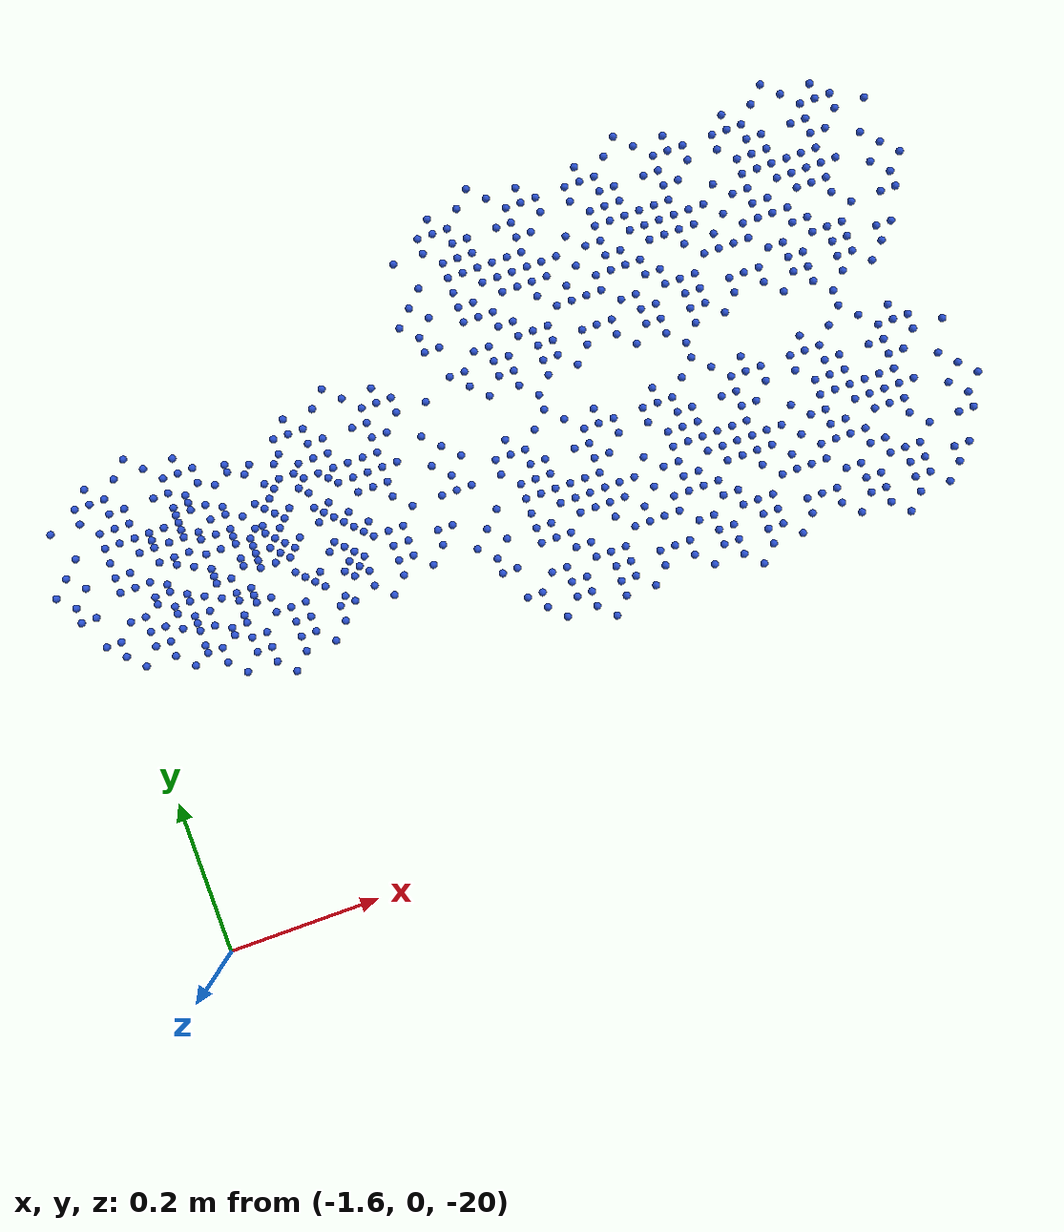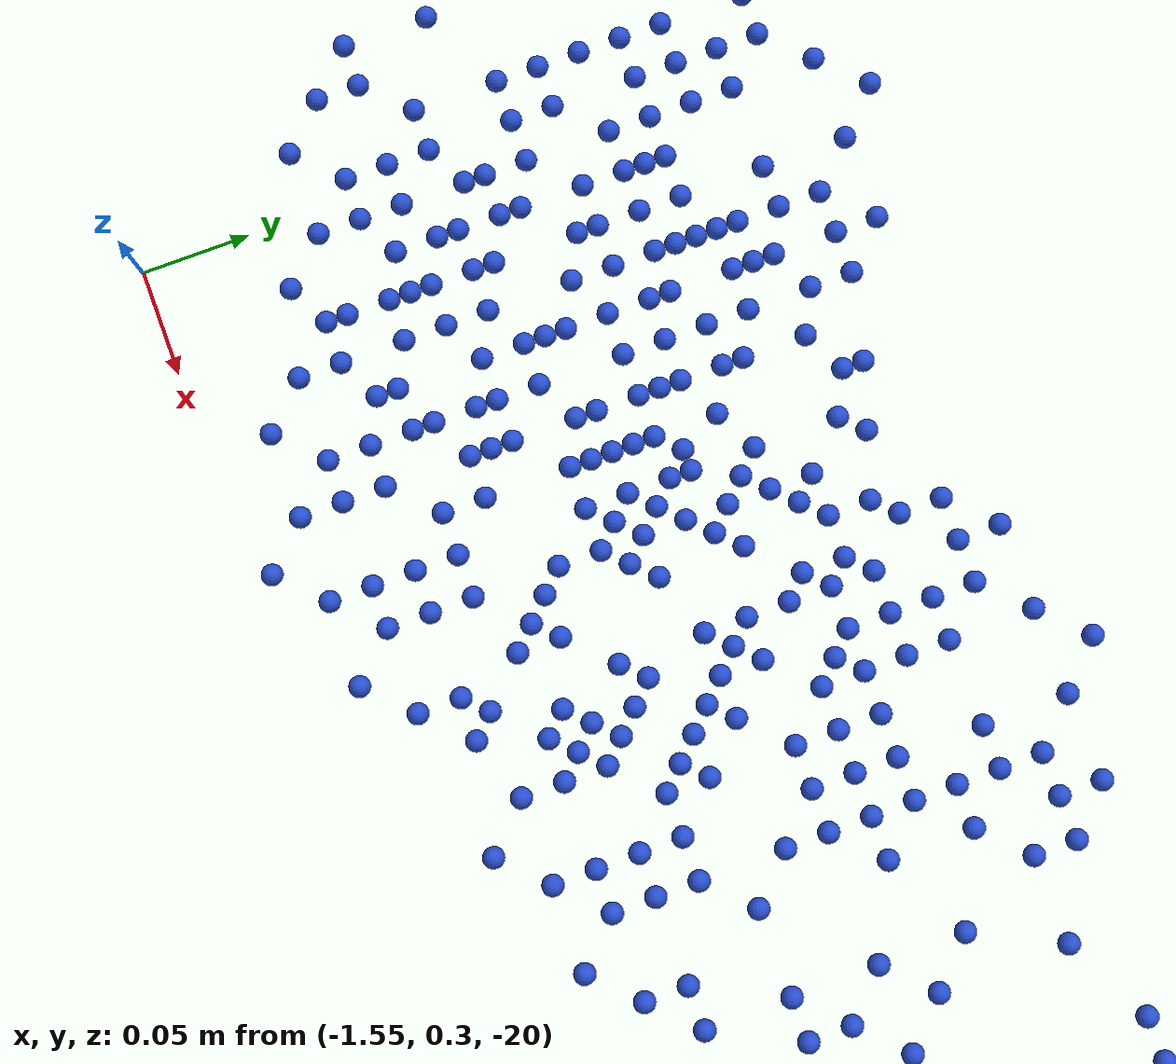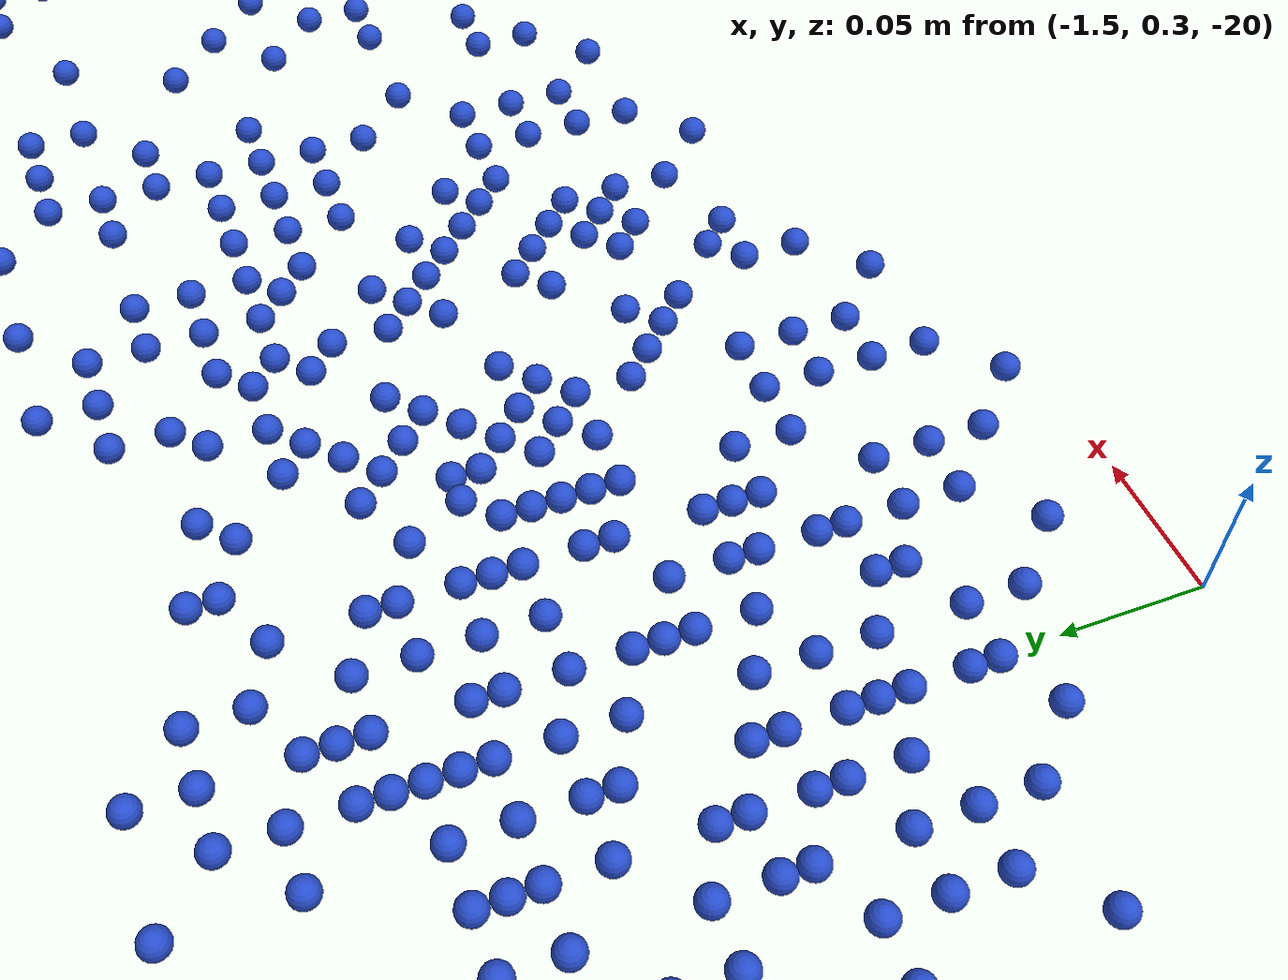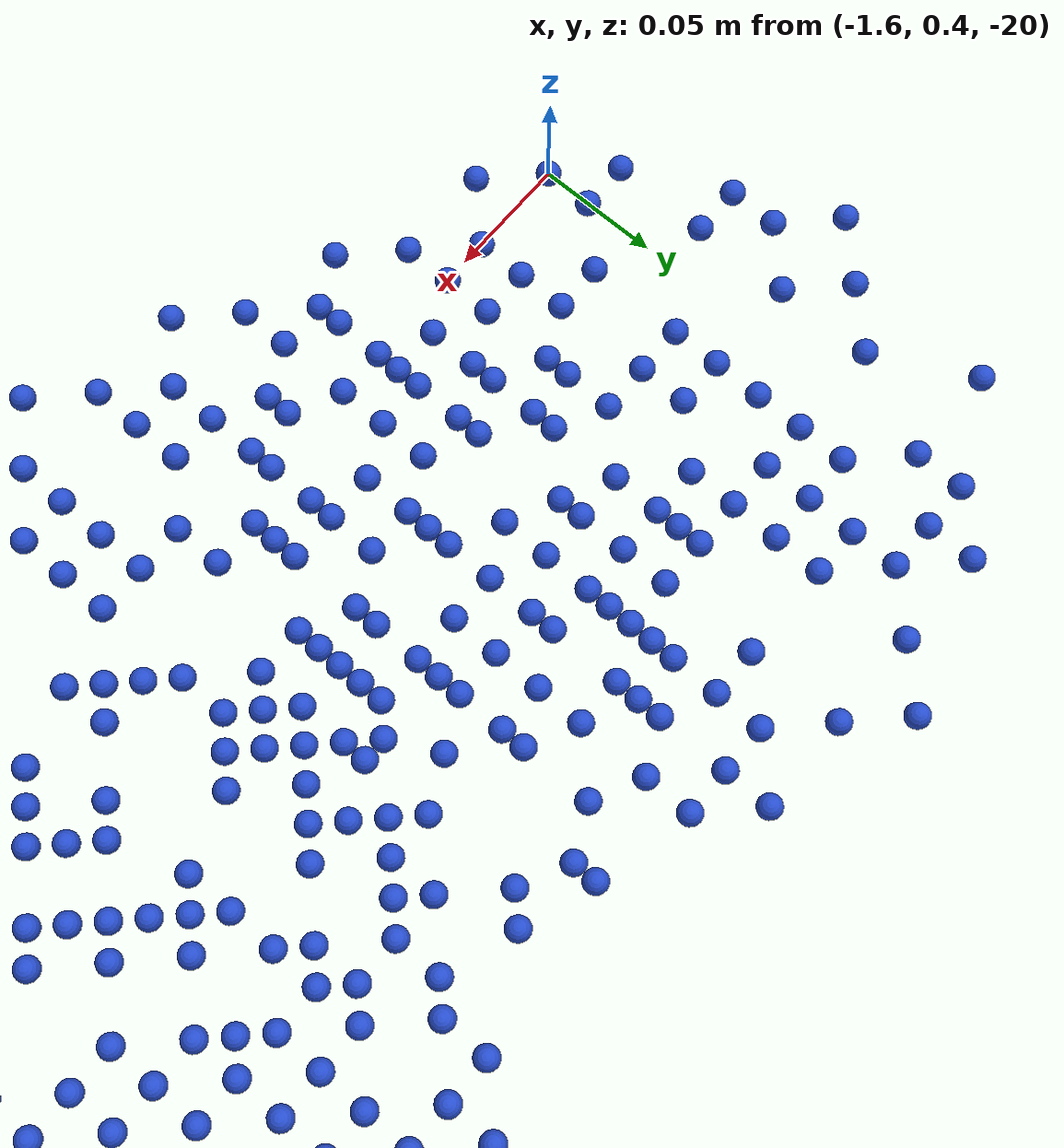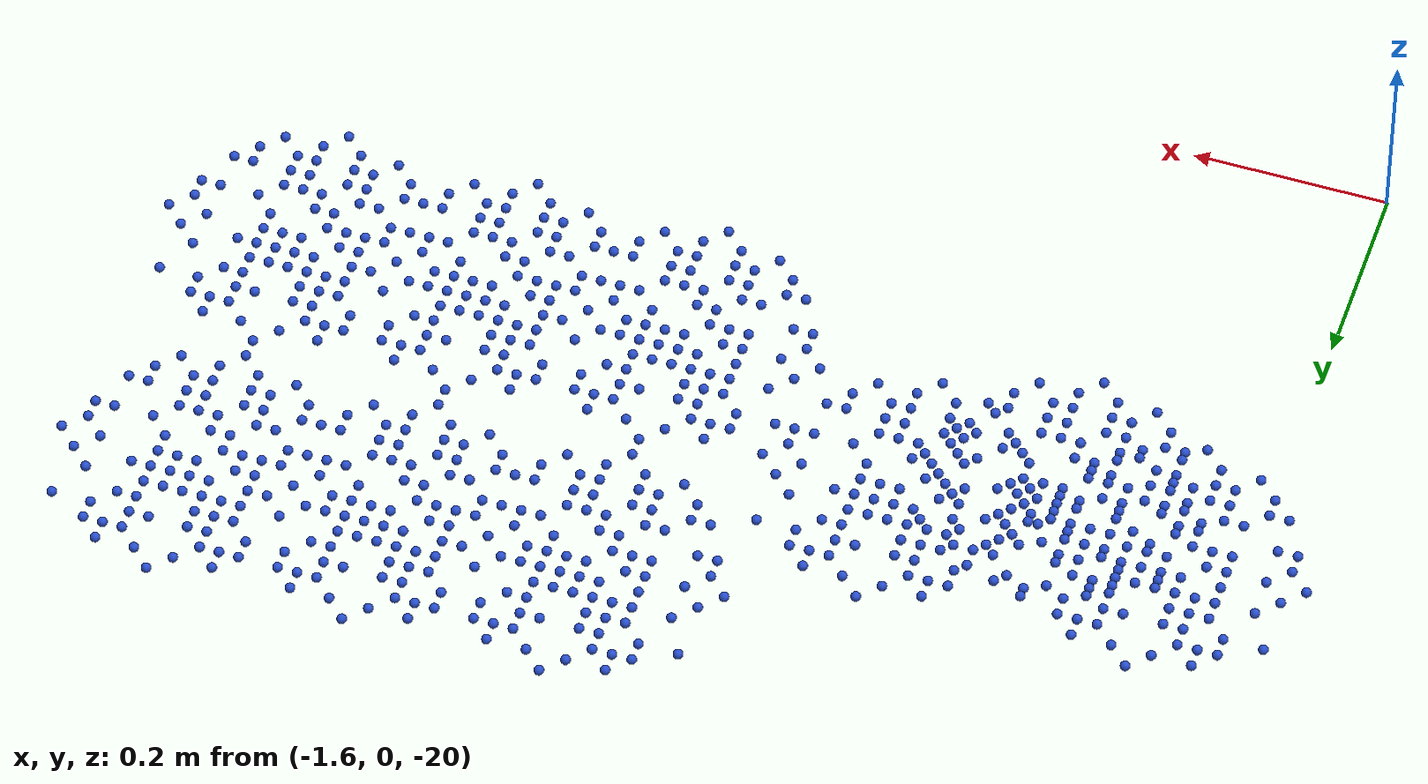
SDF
<?xml version='1.0'?>
<sdf version='1.7'>
  <model name='Washbasin_Water'>
    <static>true</static>
    <pose>0 0 0 0 0 0</pose>

    <link name="washbasin_water_tr1">
        <pose>-0.59 0.68 -20 0 0 0</pose>
        <visual name="green_mark_centre1_visual">
            <pose> 0 0 0 0 0 0 </pose>
            <geometry>
                <sphere>
                    <radius>0.005</radius>
                </sphere>
            </geometry>
            <material>
                <script>
                    <name>Gazebo/BlueGlow</name>
                </script>
            </material>
        </visual>

        <visual name="green_mark_centre2_visual">
            <pose> 0.02 0 0 0 0 0 </pose>
            <geometry>
                <sphere>
                    <radius>0.005</radius>
                </sphere>
            </geometry>
            <material>
                <script>
                    <name>Gazebo/BlueGlow</name>
                </script>
            </material>
        </visual>

        <visual name="green_mark_centre4_visual">
            <pose> 0.04 0 0 0 0 0 </pose>
            <geometry>
                <sphere>
                    <radius>0.005</radius>
                </sphere>
            </geometry>
            <material>
                <script>
                    <name>Gazebo/BlueGlow</name>
                </script>
            </material>
        </visual>

        <visual name="green_mark_centre5_visual">
            <pose> -0.04 0 0 0 0 0 </pose>
            <geometry>
                <sphere>
                    <radius>0.005</radius>
                </sphere>
            </geometry>
            <material>
                <script>
                    <name>Gazebo/BlueGlow</name>
                </script>
            </material>
        </visual>

        <visual name="green_mark_centre7_visual">
            <pose> -0.06 0 0 0 0 0 </pose>
            <geometry>
                <sphere>
                    <radius>0.005</radius>
                </sphere>
            </geometry>
            <material>
                <script>
                    <name>Gazebo/BlueGlow</name>
                </script>
            </material>
        </visual>

        <visual name="green_mark_centre8_visual">
            <pose> 0 0.02 0 0 0 0 </pose>
            <geometry>
                <sphere>
                    <radius>0.005</radius>
                </sphere>
            </geometry>
            <material>
                <script>
                    <name>Gazebo/BlueGlow</name>
                </script>
            </material>
        </visual>

        <visual name="green_mark_centre10_visual">
            <pose> 0 0.04 0 0 0 0 </pose>
            <geometry>
                <sphere>
                    <radius>0.005</radius>
                </sphere>
            </geometry>
            <material>
                <script>
                    <name>Gazebo/BlueGlow</name>
                </script>
            </material>
        </visual>

        <visual name="green_mark_centre11_visual">
            <pose> 0 -0.04 0 0 0 0 </pose>
            <geometry>
                <sphere>
                    <radius>0.005</radius>
                </sphere>
            </geometry>
            <material>
                <script>
                    <name>Gazebo/BlueGlow</name>
                </script>
            </material>
        </visual>

        <visual name="green_mark_centre13_visual">
            <pose> 0 -0.06 0 0 0 0 </pose>
            <geometry>
                <sphere>
                    <radius>0.005</radius>
                </sphere>
            </geometry>
            <material>
                <script>
                    <name>Gazebo/BlueGlow</name>
                </script>
            </material>
        </visual>

        <visual name="green_mark_centre14_visual">
            <pose> 0.02 0.02 0 0 0 0 </pose>
            <geometry>
                <sphere>
                    <radius>0.005</radius>
                </sphere>
            </geometry>
            <material>
                <script>
                    <name>Gazebo/BlueGlow</name>
                </script>
            </material>
        </visual>

        <visual name="green_mark_centre16_visual">
            <pose> -0.02 -0.02 0 0 0 0 </pose>
            <geometry>
                <sphere>
                    <radius>0.005</radius>
                </sphere>
            </geometry>
            <material>
                <script>
                    <name>Gazebo/BlueGlow</name>
                </script>
            </material>
        </visual>

        <visual name="green_mark_centre17_visual">
            <pose> -0.02 0.02 0 0 0 0 </pose>
            <geometry>
                <sphere>
                    <radius>0.005</radius>
                </sphere>
            </geometry>
            <material>
                <script>
                    <name>Gazebo/BlueGlow</name>
                </script>
            </material>
        </visual>

        <visual name="green_mark_centre19_visual">
            <pose> 0.04 0.04 0 0 0 0 </pose>
            <geometry>
                <sphere>
                    <radius>0.005</radius>
                </sphere>
            </geometry>
            <material>
                <script>
                    <name>Gazebo/BlueGlow</name>
                </script>
            </material>
        </visual>

        <visual name="green_mark_centre20_visual">
            <pose> -0.04 0.04 0 0 0 0 </pose>
            <geometry>
                <sphere>
                    <radius>0.005</radius>
                </sphere>
            </geometry>
            <material>
                <script>
                    <name>Gazebo/BlueGlow</name>
                </script>
            </material>
        </visual>

        <visual name="green_mark_centre22_visual">
            <pose> 0.04 0.06 0 0 0 0 </pose>
            <geometry>
                <sphere>
                    <radius>0.005</radius>
                </sphere>
            </geometry>
            <material>
                <script>
                    <name>Gazebo/BlueGlow</name>
                </script>
            </material>
        </visual>

        <visual name="green_mark_centre23_visual">
            <pose> 0.04 -0.06 0 0 0 0 </pose>
            <geometry>
                <sphere>
                    <radius>0.005</radius>
                </sphere>
            </geometry>
            <material>
                <script>
                    <name>Gazebo/BlueGlow</name>
                </script>
            </material>
        </visual>

        <visual name="green_mark_centre25_visual">
            <pose> -0.04 0.06 0 0 0 0 </pose>
            <geometry>
                <sphere>
                    <radius>0.005</radius>
                </sphere>
            </geometry>
            <material>
                <script>
                    <name>Gazebo/BlueGlow</name>
                </script>
            </material>
        </visual>

        <visual name="green_mark_centre26_visual">
            <pose> -0.04 -0.06 0 0 0 0 </pose>
            <geometry>
                <sphere>
                    <radius>0.005</radius>
                </sphere>
            </geometry>
            <material>
                <script>
                    <name>Gazebo/BlueGlow</name>
                </script>
            </material>
        </visual>

        <visual name="green_mark_centre28_visual">
            <pose> 0.06 0.06 0 0 0 0 </pose>
            <geometry>
                <sphere>
                    <radius>0.005</radius>
                </sphere>
            </geometry>
            <material>
                <script>
                    <name>Gazebo/BlueGlow</name>
                </script>
            </material>
        </visual>

        <visual name="green_mark_centre29_visual">
            <pose> -0.06 0.06 0 0 0 0 </pose>
            <geometry>
                <sphere>
                    <radius>0.005</radius>
                </sphere>
            </geometry>
            <material>
                <script>
                    <name>Gazebo/BlueGlow</name>
                </script>
            </material>
        </visual>

        <visual name="green_mark_centre31_visual">
            <pose> -0.06 -0.06 0 0 0 0 </pose>
            <geometry>
                <sphere>
                    <radius>0.005</radius>
                </sphere>
            </geometry>
            <material>
                <script>
                    <name>Gazebo/BlueGlow</name>
                </script>
            </material>
        </visual>

        <visual name="green_mark_centre32_visual">
            <pose> 0.02 0.04 0 0 0 0 </pose>
            <geometry>
                <sphere>
                    <radius>0.005</radius>
                </sphere>
            </geometry>
            <material>
                <script>
                    <name>Gazebo/BlueGlow</name>
                </script>
            </material>
        </visual>

        <visual name="green_mark_centre34_visual">
            <pose> -0.02 0.04 0 0 0 0 </pose>
            <geometry>
                <sphere>
                    <radius>0.005</radius>
                </sphere>
            </geometry>
            <material>
                <script>
                    <name>Gazebo/BlueGlow</name>
                </script>
            </material>
        </visual>

        <visual name="green_mark_centre35_visual">
            <pose> -0.02 -0.04 0 0 0 0 </pose>
            <geometry>
                <sphere>
                    <radius>0.005</radius>
                </sphere>
            </geometry>
            <material>
                <script>
                    <name>Gazebo/BlueGlow</name>
                </script>
            </material>
        </visual>

        <visual name="green_mark_centre37_visual">
            <pose> 0.02 -0.06 0 0 0 0 </pose>
            <geometry>
                <sphere>
                    <radius>0.005</radius>
                </sphere>
            </geometry>
            <material>
                <script>
                    <name>Gazebo/BlueGlow</name>
                </script>
            </material>
        </visual>

        <visual name="green_mark_centre38_visual">
            <pose> -0.02 0.06 0 0 0 0 </pose>
            <geometry>
                <sphere>
                    <radius>0.005</radius>
                </sphere>
            </geometry>
            <material>
                <script>
                    <name>Gazebo/BlueGlow</name>
                </script>
            </material>
        </visual>

        <visual name="green_mark_centre40_visual">
            <pose> 0.04 0.02 0 0 0 0 </pose>
            <geometry>
                <sphere>
                    <radius>0.005</radius>
                </sphere>
            </geometry>
            <material>
                <script>
                    <name>Gazebo/BlueGlow</name>
                </script>
            </material>
        </visual>

        <visual name="green_mark_centre41_visual">
            <pose> 0.04 -0.02 0 0 0 0 </pose>
            <geometry>
                <sphere>
                    <radius>0.005</radius>
                </sphere>
            </geometry>
            <material>
                <script>
                    <name>Gazebo/BlueGlow</name>
                </script>
            </material>
        </visual>

        <visual name="green_mark_centre43_visual">
            <pose> -0.04 -0.02 0 0 0 0 </pose>
            <geometry>
                <sphere>
                    <radius>0.005</radius>
                </sphere>
            </geometry>
            <material>
                <script>
                    <name>Gazebo/BlueGlow</name>
                </script>
            </material>
        </visual>

        <visual name="green_mark_centre44_visual">
            <pose> 0.06 0.02 0 0 0 0 </pose>
            <geometry>
                <sphere>
                    <radius>0.005</radius>
                </sphere>
            </geometry>
            <material>
                <script>
                    <name>Gazebo/BlueGlow</name>
                </script>
            </material>
        </visual>

        <visual name="green_mark_centre46_visual">
            <pose> -0.06 0.02 0 0 0 0 </pose>
            <geometry>
                <sphere>
                    <radius>0.005</radius>
                </sphere>
            </geometry>
            <material>
                <script>
                    <name>Gazebo/BlueGlow</name>
                </script>
            </material>
        </visual>

        <visual name="green_mark_centre47_visual">
            <pose> -0.06 -0.02 0 0 0 0 </pose>
            <geometry>
                <sphere>
                    <radius>0.005</radius>
                </sphere>
            </geometry>
            <material>
                <script>
                    <name>Gazebo/BlueGlow</name>
                </script>
            </material>
        </visual>

        <visual name="green_mark_centre49_visual">
            <pose> 0.06 -0.04 0 0 0 0 </pose>
            <geometry>
                <sphere>
                    <radius>0.005</radius>
                </sphere>
            </geometry>
            <material>
                <script>
                    <name>Gazebo/BlueGlow</name>
                </script>
            </material>
        </visual>

        <visual name="green_mark_centre50_visual">
            <pose> -0.06 0.04 0 0 0 0 </pose>
            <geometry>
                <sphere>
                    <radius>0.005</radius>
                </sphere>
            </geometry>
            <material>
                <script>
                    <name>Gazebo/BlueGlow</name>
                </script>
            </material>
        </visual>

        <visual name="green_mark_top1_visual">
            <pose> -0.06 0.12 0 0 0 0 </pose>
            <geometry>
                <sphere>
                    <radius>0.005</radius>
                </sphere>
            </geometry>
            <material>
                <script>
                    <name>Gazebo/BlueGlow</name>
                </script>
            </material>
        </visual>

        <visual name="green_mark_top2_visual">
            <pose> -0.06 0.10 0 0 0 0 </pose>
            <geometry>
                <sphere>
                    <radius>0.005</radius>
                </sphere>
            </geometry>
            <material>
                <script>
                    <name>Gazebo/BlueGlow</name>
                </script>
            </material>
        </visual>

        <visual name="green_mark_top4_visual">
            <pose> -0.04 0.10 0 0 0 0 </pose>
            <geometry>
                <sphere>
                    <radius>0.005</radius>
                </sphere>
            </geometry>
            <material>
                <script>
                    <name>Gazebo/BlueGlow</name>
                </script>
            </material>
        </visual>

        <visual name="green_mark_top7_visual">
            <pose> -0.04 0.08 0 0 0 0 </pose>
            <geometry>
                <sphere>
                    <radius>0.005</radius>
                </sphere>
            </geometry>
            <material>
                <script>
                    <name>Gazebo/BlueGlow</name>
                </script>
            </material>
        </visual>

        <visual name="green_mark_top8_visual">
            <pose> -0.02 0.12 0 0 0 0 </pose>
            <geometry>
                <sphere>
                    <radius>0.005</radius>
                </sphere>
            </geometry>
            <material>
                <script>
                    <name>Gazebo/BlueGlow</name>
                </script>
            </material>
        </visual>

        <visual name="green_mark_top10_visual">
            <pose> -0.02 0.12 0 0 0 0 </pose>
            <geometry>
                <sphere>
                    <radius>0.005</radius>
                </sphere>
            </geometry>
            <material>
                <script>
                    <name>Gazebo/BlueGlow</name>
                </script>
            </material>
        </visual>

        <visual name="green_mark_top12_visual">
            <pose> -0.02 0.08 0 0 0 0 </pose>
            <geometry>
                <sphere>
                    <radius>0.005</radius>
                </sphere>
            </geometry>
            <material>
                <script>
                    <name>Gazebo/BlueGlow</name>
                </script>
            </material>
        </visual>

        <visual name="green_mark_top14_visual">
            <pose> 0.06 0.12 0 0 0 0 </pose>
            <geometry>
                <sphere>
                    <radius>0.005</radius>
                </sphere>
            </geometry>
            <material>
                <script>
                    <name>Gazebo/BlueGlow</name>
                </script>
            </material>
        </visual>

        <visual name="green_mark_top15_visual">
            <pose> 0.06 0.10 0 0 0 0 </pose>
            <geometry>
                <sphere>
                    <radius>0.005</radius>
                </sphere>
            </geometry>
            <material>
                <script>
                    <name>Gazebo/BlueGlow</name>
                </script>
            </material>
        </visual>

        <visual name="green_mark_top17_visual">
            <pose> 0.04 0.10 0 0 0 0 </pose>
            <geometry>
                <sphere>
                    <radius>0.005</radius>
                </sphere>
            </geometry>
            <material>
                <script>
                    <name>Gazebo/BlueGlow</name>
                </script>
            </material>
        </visual>

        <visual name="green_mark_top20_visual">
            <pose> 0.04 0.08 0 0 0 0 </pose>
            <geometry>
                <sphere>
                    <radius>0.005</radius>
                </sphere>
            </geometry>
            <material>
                <script>
                    <name>Gazebo/BlueGlow</name>
                </script>
            </material>
        </visual>

        <visual name="green_mark_top21_visual">
            <pose> 0.02 0.12 0 0 0 0 </pose>
            <geometry>
                <sphere>
                    <radius>0.005</radius>
                </sphere>
            </geometry>
            <material>
                <script>
                    <name>Gazebo/BlueGlow</name>
                </script>
            </material>
        </visual>

        <visual name="green_mark_top23_visual">
            <pose> 0.02 0.12 0 0 0 0 </pose>
            <geometry>
                <sphere>
                    <radius>0.005</radius>
                </sphere>
            </geometry>
            <material>
                <script>
                    <name>Gazebo/BlueGlow</name>
                </script>
            </material>
        </visual>

        <visual name="green_mark_top25_visual">
            <pose> 0.02 0.08 0 0 0 0 </pose>
            <geometry>
                <sphere>
                    <radius>0.005</radius>
                </sphere>
            </geometry>
            <material>
                <script>
                    <name>Gazebo/BlueGlow</name>
                </script>
            </material>
        </visual>

        <visual name="green_mark_top88_visual">
            <pose> 0.0 0.14 0 0 0 0 </pose>
            <geometry>
                <sphere>
                    <radius>0.005</radius>
                </sphere>
            </geometry>
            <material>
                <script>
                    <name>Gazebo/BlueGlow</name>
                </script>
            </material>
        </visual>

        <visual name="green_mark_top89_visual">
            <pose> 0.0 -0.14 0 0 0 0 </pose>
            <geometry>
                <sphere>
                    <radius>0.005</radius>
                </sphere>
            </geometry>
            <material>
                <script>
                    <name>Gazebo/BlueGlow</name>
                </script>
            </material>
        </visual>

        <visual name="green_mark_top3_visual">
            <pose> -0.06 -0.12 0 0 0 0 </pose>
            <geometry>
                <sphere>
                    <radius>0.005</radius>
                </sphere>
            </geometry>
            <material>
                <script>
                    <name>Gazebo/BlueGlow</name>
                </script>
            </material>
        </visual>

        <visual name="green_mark_top5_visual">
            <pose> -0.04 -0.10 0 0 0 0 </pose>
            <geometry>
                <sphere>
                    <radius>0.005</radius>
                </sphere>
            </geometry>
            <material>
                <script>
                    <name>Gazebo/BlueGlow</name>
                </script>
            </material>
        </visual>

        <visual name="green_mark_top6_visual">
            <pose> -0.04 -0.08 0 0 0 0 </pose>
            <geometry>
                <sphere>
                    <radius>0.005</radius>
                </sphere>
            </geometry>
            <material>
                <script>
                    <name>Gazebo/BlueGlow</name>
                </script>
            </material>
        </visual>

        <visual name="green_mark_top9_visual">
            <pose> -0.02 -0.12 0 0 0 0 </pose>
            <geometry>
                <sphere>
                    <radius>0.005</radius>
                </sphere>
            </geometry>
            <material>
                <script>
                    <name>Gazebo/BlueGlow</name>
                </script>
            </material>
        </visual>

        <visual name="green_mark_top11_visual">
            <pose> -0.02 -0.10 0 0 0 0 </pose>
            <geometry>
                <sphere>
                    <radius>0.005</radius>
                </sphere>
            </geometry>
            <material>
                <script>
                    <name>Gazebo/BlueGlow</name>
                </script>
            </material>
        </visual>

        <visual name="green_mark_top13_visual">
            <pose> -0.02 -0.08 0 0 0 0 </pose>
            <geometry>
                <sphere>
                    <radius>0.005</radius>
                </sphere>
            </geometry>
            <material>
                <script>
                    <name>Gazebo/BlueGlow</name>
                </script>
            </material>
        </visual>

        <visual name="green_mark_top6_visual">
            <pose> -0.04 -0.08 0 0 0 0 </pose>
            <geometry>
                <sphere>
                    <radius>0.005</radius>
                </sphere>
            </geometry>
            <material>
                <script>
                    <name>Gazebo/BlueGlow</name>
                </script>
            </material>
        </visual>

        <visual name="green_mark_top16_visual">
            <pose> 0.06 -0.12 0 0 0 0 </pose>
            <geometry>
                <sphere>
                    <radius>0.005</radius>
                </sphere>
            </geometry>
            <material>
                <script>
                    <name>Gazebo/BlueGlow</name>
                </script>
            </material>
        </visual>

        <visual name="green_mark_top18_visual">
            <pose> 0.04 -0.10 0 0 0 0 </pose>
            <geometry>
                <sphere>
                    <radius>0.005</radius>
                </sphere>
            </geometry>
            <material>
                <script>
                    <name>Gazebo/BlueGlow</name>
                </script>
            </material>
        </visual>

        <visual name="green_mark_top19_visual">
            <pose> 0.04 -0.08 0 0 0 0 </pose>
            <geometry>
                <sphere>
                    <radius>0.005</radius>
                </sphere>
            </geometry>
            <material>
                <script>
                    <name>Gazebo/BlueGlow</name>
                </script>
            </material>
        </visual>

        <visual name="green_mark_top22_visual">
            <pose> 0.02 -0.12 0 0 0 0 </pose>
            <geometry>
                <sphere>
                    <radius>0.005</radius>
                </sphere>
            </geometry>
            <material>
                <script>
                    <name>Gazebo/BlueGlow</name>
                </script>
            </material>
        </visual>

        <visual name="green_mark_top24_visual">
            <pose> 0.02 -0.10 0 0 0 0 </pose>
            <geometry>
                <sphere>
                    <radius>0.005</radius>
                </sphere>
            </geometry>
            <material>
                <script>
                    <name>Gazebo/BlueGlow</name>
                </script>
            </material>
        </visual>

        <visual name="green_mark_top26_visual">
            <pose> 0.02 -0.08 0 0 0 0 </pose>
            <geometry>
                <sphere>
                    <radius>0.005</radius>
                </sphere>
            </geometry>
            <material>
                <script>
                    <name>Gazebo/BlueGlow</name>
                </script>
            </material>
        </visual>

        <visual name="green_mark_top3_visual">
            <pose> -0.14 0 0 0 0 0 </pose>
            <geometry>
                <sphere>
                    <radius>0.005</radius>
                </sphere>
            </geometry>
            <material>
                <script>
                    <name>Gazebo/BlueGlow</name>
                </script>
            </material>
        </visual>

        <visual name="green_mark_top365_visual">
            <pose> -0.12 0.08 0 0 0 0 </pose>
            <geometry>
                <sphere>
                    <radius>0.005</radius>
                </sphere>
            </geometry>
            <material>
                <script>
                    <name>Gazebo/BlueGlow</name>
                </script>
            </material>
        </visual>

        <visual name="green_mark_top93_visual">
            <pose> -0.10 0 0 0 0 0 </pose>
            <geometry>
                <sphere>
                    <radius>0.005</radius>
                </sphere>
            </geometry>
            <material>
                <script>
                    <name>Gazebo/BlueGlow</name>
                </script>
            </material>
        </visual>

        <visual name="green_mark_top5_visual">
            <pose> -0.12 0.02 0 0 0 0 </pose>
            <geometry>
                <sphere>
                    <radius>0.005</radius>
                </sphere>
            </geometry>
            <material>
                <script>
                    <name>Gazebo/BlueGlow</name>
                </script>
            </material>
        </visual>

        <visual name="green_mark_top6_visual">
            <pose> -0.10 0.04 0 0 0 0 </pose>
            <geometry>
                <sphere>
                    <radius>0.005</radius>
                </sphere>
            </geometry>
            <material>
                <script>
                    <name>Gazebo/BlueGlow</name>
                </script>
            </material>
        </visual>

        <visual name="green_mark_top20_visual">
            <pose> -0.08 0.10 0 0 0 0 </pose>
            <geometry>
                <sphere>
                    <radius>0.005</radius>
                </sphere>
            </geometry>
            <material>
                <script>
                    <name>Gazebo/BlueGlow</name>
                </script>
            </material>
        </visual>

        <visual name="green_mark_top50_visual">
            <pose> -0.08 0.08 0 0 0 0 </pose>
            <geometry>
                <sphere>
                    <radius>0.005</radius>
                </sphere>
            </geometry>
            <material>
                <script>
                    <name>Gazebo/BlueGlow</name>
                </script>
            </material>
        </visual>

        <visual name="green_mark_top3_visual">
            <pose> -0.12 -0.04 0 0 0 0 </pose>
            <geometry>
                <sphere>
                    <radius>0.005</radius>
                </sphere>
            </geometry>
            <material>
                <script>
                    <name>Gazebo/BlueGlow</name>
                </script>
            </material>
        </visual>

        <visual name="green_mark_top5_visual">
            <pose> -0.12 -0.02 0 0 0 0 </pose>
            <geometry>
                <sphere>
                    <radius>0.005</radius>
                </sphere>
            </geometry>
            <material>
                <script>
                    <name>Gazebo/BlueGlow</name>
                </script>
            </material>
        </visual>

        <visual name="green_mark_top6_visual">
            <pose> -0.10 -0.04 0 0 0 0 </pose>
            <geometry>
                <sphere>
                    <radius>0.005</radius>
                </sphere>
            </geometry>
            <material>
                <script>
                    <name>Gazebo/BlueGlow</name>
                </script>
            </material>
        </visual>

        <visual name="green_mark_top6_visual">
            <pose> -0.10 -0.08 0 0 0 0 </pose>
            <geometry>
                <sphere>
                    <radius>0.005</radius>
                </sphere>
            </geometry>
            <material>
                <script>
                    <name>Gazebo/BlueGlow</name>
                </script>
            </material>
        </visual>

        <visual name="green_mark_top20_visual">
            <pose> -0.08 -0.10 0 0 0 0 </pose>
            <geometry>
                <sphere>
                    <radius>0.005</radius>
                </sphere>
            </geometry>
            <material>
                <script>
                    <name>Gazebo/BlueGlow</name>
                </script>
            </material>
        </visual>

        <visual name="green_mark_top50_visual">
            <pose> -0.08 -0.08 0 0 0 0 </pose>
            <geometry>
                <sphere>
                    <radius>0.005</radius>
                </sphere>
            </geometry>
            <material>
                <script>
                    <name>Gazebo/BlueGlow</name>
                </script>
            </material>
        </visual>

        <visual name="green_mark_top3_visual">
            <pose> 0.14 0 0 0 0 0 </pose>
            <geometry>
                <sphere>
                    <radius>0.005</radius>
                </sphere>
            </geometry>
            <material>
                <script>
                    <name>Gazebo/BlueGlow</name>
                </script>
            </material>
        </visual>

        <visual name="green_mark_top365_visual">
            <pose> 0.12 0.08 0 0 0 0 </pose>
            <geometry>
                <sphere>
                    <radius>0.005</radius>
                </sphere>
            </geometry>
            <material>
                <script>
                    <name>Gazebo/BlueGlow</name>
                </script>
            </material>
        </visual>

        <visual name="green_mark_top93_visual">
            <pose> 0.10 0 0 0 0 0 </pose>
            <geometry>
                <sphere>
                    <radius>0.005</radius>
                </sphere>
            </geometry>
            <material>
                <script>
                    <name>Gazebo/BlueGlow</name>
                </script>
            </material>
        </visual>

        <visual name="green_mark_top5_visual">
            <pose> 0.12 0.02 0 0 0 0 </pose>
            <geometry>
                <sphere>
                    <radius>0.005</radius>
                </sphere>
            </geometry>
            <material>
                <script>
                    <name>Gazebo/BlueGlow</name>
                </script>
            </material>
        </visual>

        <visual name="green_mark_top6_visual">
            <pose> 0.10 0.04 0 0 0 0 </pose>
            <geometry>
                <sphere>
                    <radius>0.005</radius>
                </sphere>
            </geometry>
            <material>
                <script>
                    <name>Gazebo/BlueGlow</name>
                </script>
            </material>
        </visual>

        <visual name="green_mark_top20_visual">
            <pose> 0.08 0.10 0 0 0 0 </pose>
            <geometry>
                <sphere>
                    <radius>0.005</radius>
                </sphere>
            </geometry>
            <material>
                <script>
                    <name>Gazebo/BlueGlow</name>
                </script>
            </material>
        </visual>

        <visual name="green_mark_top50_visual">
            <pose> 0.08 0.08 0 0 0 0 </pose>
            <geometry>
                <sphere>
                    <radius>0.005</radius>
                </sphere>
            </geometry>
            <material>
                <script>
                    <name>Gazebo/BlueGlow</name>
                </script>
            </material>
        </visual>

        <visual name="green_mark_top3_visual">
            <pose> 0.12 -0.04 0 0 0 0 </pose>
            <geometry>
                <sphere>
                    <radius>0.005</radius>
                </sphere>
            </geometry>
            <material>
                <script>
                    <name>Gazebo/BlueGlow</name>
                </script>
            </material>
        </visual>

        <visual name="green_mark_top5_visual">
            <pose> 0.12 -0.02 0 0 0 0 </pose>
            <geometry>
                <sphere>
                    <radius>0.005</radius>
                </sphere>
            </geometry>
            <material>
                <script>
                    <name>Gazebo/BlueGlow</name>
                </script>
            </material>
        </visual>

        <visual name="green_mark_top6_visual">
            <pose> 0.10 -0.04 0 0 0 0 </pose>
            <geometry>
                <sphere>
                    <radius>0.005</radius>
                </sphere>
            </geometry>
            <material>
                <script>
                    <name>Gazebo/BlueGlow</name>
                </script>
            </material>
        </visual>

        <visual name="green_mark_top6_visual">
            <pose> 0.10 -0.08 0 0 0 0 </pose>
            <geometry>
                <sphere>
                    <radius>0.005</radius>
                </sphere>
            </geometry>
            <material>
                <script>
                    <name>Gazebo/BlueGlow</name>
                </script>
            </material>
        </visual>

        <visual name="green_mark_top20_visual">
            <pose> 0.08 -0.10 0 0 0 0 </pose>
            <geometry>
                <sphere>
                    <radius>0.005</radius>
                </sphere>
            </geometry>
            <material>
                <script>
                    <name>Gazebo/BlueGlow</name>
                </script>
            </material>
        </visual>

        <visual name="green_mark_top50_visual">
            <pose> 0.08 -0.08 0 0 0 0 </pose>
            <geometry>
                <sphere>
                    <radius>0.005</radius>
                </sphere>
            </geometry>
            <material>
                <script>
                    <name>Gazebo/BlueGlow</name>
                </script>
            </material>
        </visual>
    </link>

    <link name="washbasin_water_br1">
        <pose>-0.59 0.38 -20 0 0 0</pose>
        <visual name="green_mark_centre1_visual">
            <pose> 0 0 0 0 0 0 </pose>
            <geometry>
                <sphere>
                    <radius>0.005</radius>
                </sphere>
            </geometry>
            <material>
                <script>
                    <name>Gazebo/BlueGlow</name>
                </script>
            </material>
        </visual>

        <visual name="green_mark_centre2_visual">
            <pose> 0.02 0 0 0 0 0 </pose>
            <geometry>
                <sphere>
                    <radius>0.005</radius>
                </sphere>
            </geometry>
            <material>
                <script>
                    <name>Gazebo/BlueGlow</name>
                </script>
            </material>
        </visual>

        <visual name="green_mark_centre4_visual">
            <pose> 0.04 0 0 0 0 0 </pose>
            <geometry>
                <sphere>
                    <radius>0.005</radius>
                </sphere>
            </geometry>
            <material>
                <script>
                    <name>Gazebo/BlueGlow</name>
                </script>
            </material>
        </visual>

        <visual name="green_mark_centre5_visual">
            <pose> -0.04 0 0 0 0 0 </pose>
            <geometry>
                <sphere>
                    <radius>0.005</radius>
                </sphere>
            </geometry>
            <material>
                <script>
                    <name>Gazebo/BlueGlow</name>
                </script>
            </material>
        </visual>

        <visual name="green_mark_centre7_visual">
            <pose> -0.06 0 0 0 0 0 </pose>
            <geometry>
                <sphere>
                    <radius>0.005</radius>
                </sphere>
            </geometry>
            <material>
                <script>
                    <name>Gazebo/BlueGlow</name>
                </script>
            </material>
        </visual>

        <visual name="green_mark_centre8_visual">
            <pose> 0 0.02 0 0 0 0 </pose>
            <geometry>
                <sphere>
                    <radius>0.005</radius>
                </sphere>
            </geometry>
            <material>
                <script>
                    <name>Gazebo/BlueGlow</name>
                </script>
            </material>
        </visual>

        <visual name="green_mark_centre10_visual">
            <pose> 0 0.04 0 0 0 0 </pose>
            <geometry>
                <sphere>
                    <radius>0.005</radius>
                </sphere>
            </geometry>
            <material>
                <script>
                    <name>Gazebo/BlueGlow</name>
                </script>
            </material>
        </visual>

        <visual name="green_mark_centre11_visual">
            <pose> 0 -0.04 0 0 0 0 </pose>
            <geometry>
                <sphere>
                    <radius>0.005</radius>
                </sphere>
            </geometry>
            <material>
                <script>
                    <name>Gazebo/BlueGlow</name>
                </script>
            </material>
        </visual>

        <visual name="green_mark_centre13_visual">
            <pose> 0 -0.06 0 0 0 0 </pose>
            <geometry>
                <sphere>
                    <radius>0.005</radius>
                </sphere>
            </geometry>
            <material>
                <script>
                    <name>Gazebo/BlueGlow</name>
                </script>
            </material>
        </visual>

        <visual name="green_mark_centre14_visual">
            <pose> 0.02 0.02 0 0 0 0 </pose>
            <geometry>
                <sphere>
                    <radius>0.005</radius>
                </sphere>
            </geometry>
            <material>
                <script>
                    <name>Gazebo/BlueGlow</name>
                </script>
            </material>
        </visual>

        <visual name="green_mark_centre16_visual">
            <pose> -0.02 -0.02 0 0 0 0 </pose>
            <geometry>
                <sphere>
                    <radius>0.005</radius>
                </sphere>
            </geometry>
            <material>
                <script>
                    <name>Gazebo/BlueGlow</name>
                </script>
            </material>
        </visual>

        <visual name="green_mark_centre17_visual">
            <pose> -0.02 0.02 0 0 0 0 </pose>
            <geometry>
                <sphere>
                    <radius>0.005</radius>
                </sphere>
            </geometry>
            <material>
                <script>
                    <name>Gazebo/BlueGlow</name>
                </script>
            </material>
        </visual>

        <visual name="green_mark_centre19_visual">
            <pose> 0.04 0.04 0 0 0 0 </pose>
            <geometry>
                <sphere>
                    <radius>0.005</radius>
                </sphere>
            </geometry>
            <material>
                <script>
                    <name>Gazebo/BlueGlow</name>
                </script>
            </material>
        </visual>

        <visual name="green_mark_centre20_visual">
            <pose> -0.04 0.04 0 0 0 0 </pose>
            <geometry>
                <sphere>
                    <radius>0.005</radius>
                </sphere>
            </geometry>
            <material>
                <script>
                    <name>Gazebo/BlueGlow</name>
                </script>
            </material>
        </visual>

        <visual name="green_mark_centre22_visual">
            <pose> 0.04 0.06 0 0 0 0 </pose>
            <geometry>
                <sphere>
                    <radius>0.005</radius>
                </sphere>
            </geometry>
            <material>
                <script>
                    <name>Gazebo/BlueGlow</name>
                </script>
            </material>
        </visual>

        <visual name="green_mark_centre23_visual">
            <pose> 0.04 -0.06 0 0 0 0 </pose>
            <geometry>
                <sphere>
                    <radius>0.005</radius>
                </sphere>
            </geometry>
            <material>
                <script>
                    <name>Gazebo/BlueGlow</name>
                </script>
            </material>
        </visual>

        <visual name="green_mark_centre25_visual">
            <pose> -0.04 0.06 0 0 0 0 </pose>
            <geometry>
                <sphere>
                    <radius>0.005</radius>
                </sphere>
            </geometry>
            <material>
                <script>
                    <name>Gazebo/BlueGlow</name>
                </script>
            </material>
        </visual>

        <visual name="green_mark_centre26_visual">
            <pose> -0.04 -0.06 0 0 0 0 </pose>
            <geometry>
                <sphere>
                    <radius>0.005</radius>
                </sphere>
            </geometry>
            <material>
                <script>
                    <name>Gazebo/BlueGlow</name>
                </script>
            </material>
        </visual>

        <visual name="green_mark_centre28_visual">
            <pose> 0.06 0.06 0 0 0 0 </pose>
            <geometry>
                <sphere>
                    <radius>0.005</radius>
                </sphere>
            </geometry>
            <material>
                <script>
                    <name>Gazebo/BlueGlow</name>
                </script>
            </material>
        </visual>

        <visual name="green_mark_centre29_visual">
            <pose> -0.06 0.06 0 0 0 0 </pose>
            <geometry>
                <sphere>
                    <radius>0.005</radius>
                </sphere>
            </geometry>
            <material>
                <script>
                    <name>Gazebo/BlueGlow</name>
                </script>
            </material>
        </visual>

        <visual name="green_mark_centre31_visual">
            <pose> -0.06 -0.06 0 0 0 0 </pose>
            <geometry>
                <sphere>
                    <radius>0.005</radius>
                </sphere>
            </geometry>
            <material>
                <script>
                    <name>Gazebo/BlueGlow</name>
                </script>
            </material>
        </visual>

        <visual name="green_mark_centre32_visual">
            <pose> 0.02 0.04 0 0 0 0 </pose>
            <geometry>
                <sphere>
                    <radius>0.005</radius>
                </sphere>
            </geometry>
            <material>
                <script>
                    <name>Gazebo/BlueGlow</name>
                </script>
            </material>
        </visual>

        <visual name="green_mark_centre34_visual">
            <pose> -0.02 0.04 0 0 0 0 </pose>
            <geometry>
                <sphere>
                    <radius>0.005</radius>
                </sphere>
            </geometry>
            <material>
                <script>
                    <name>Gazebo/BlueGlow</name>
                </script>
            </material>
        </visual>

        <visual name="green_mark_centre35_visual">
            <pose> -0.02 -0.04 0 0 0 0 </pose>
            <geometry>
                <sphere>
                    <radius>0.005</radius>
                </sphere>
            </geometry>
            <material>
                <script>
                    <name>Gazebo/BlueGlow</name>
                </script>
            </material>
        </visual>

        <visual name="green_mark_centre37_visual">
            <pose> 0.02 -0.06 0 0 0 0 </pose>
            <geometry>
                <sphere>
                    <radius>0.005</radius>
                </sphere>
            </geometry>
            <material>
                <script>
                    <name>Gazebo/BlueGlow</name>
                </script>
            </material>
        </visual>

        <visual name="green_mark_centre38_visual">
            <pose> -0.02 0.06 0 0 0 0 </pose>
            <geometry>
                <sphere>
                    <radius>0.005</radius>
                </sphere>
            </geometry>
            <material>
                <script>
                    <name>Gazebo/BlueGlow</name>
                </script>
            </material>
        </visual>

        <visual name="green_mark_centre40_visual">
            <pose> 0.04 0.02 0 0 0 0 </pose>
            <geometry>
                <sphere>
                    <radius>0.005</radius>
                </sphere>
            </geometry>
            <material>
                <script>
                    <name>Gazebo/BlueGlow</name>
                </script>
            </material>
        </visual>

        <visual name="green_mark_centre41_visual">
            <pose> 0.04 -0.02 0 0 0 0 </pose>
            <geometry>
                <sphere>
                    <radius>0.005</radius>
                </sphere>
            </geometry>
            <material>
                <script>
                    <name>Gazebo/BlueGlow</name>
                </script>
            </material>
        </visual>

        <visual name="green_mark_centre43_visual">
            <pose> -0.04 -0.02 0 0 0 0 </pose>
            <geometry>
                <sphere>
                    <radius>0.005</radius>
                </sphere>
            </geometry>
            <material>
                <script>
                    <name>Gazebo/BlueGlow</name>
                </script>
            </material>
        </visual>

        <visual name="green_mark_centre44_visual">
            <pose> 0.06 0.02 0 0 0 0 </pose>
            <geometry>
                <sphere>
                    <radius>0.005</radius>
                </sphere>
            </geometry>
            <material>
                <script>
                    <name>Gazebo/BlueGlow</name>
                </script>
            </material>
        </visual>

        <visual name="green_mark_centre46_visual">
            <pose> -0.06 0.02 0 0 0 0 </pose>
            <geometry>
                <sphere>
                    <radius>0.005</radius>
                </sphere>
            </geometry>
            <material>
                <script>
                    <name>Gazebo/BlueGlow</name>
                </script>
            </material>
        </visual>

        <visual name="green_mark_centre47_visual">
            <pose> -0.06 -0.02 0 0 0 0 </pose>
            <geometry>
                <sphere>
                    <radius>0.005</radius>
                </sphere>
            </geometry>
            <material>
                <script>
                    <name>Gazebo/BlueGlow</name>
                </script>
            </material>
        </visual>

        <visual name="green_mark_centre49_visual">
            <pose> 0.06 -0.04 0 0 0 0 </pose>
            <geometry>
                <sphere>
                    <radius>0.005</radius>
                </sphere>
            </geometry>
            <material>
                <script>
                    <name>Gazebo/BlueGlow</name>
                </script>
            </material>
        </visual>

        <visual name="green_mark_centre50_visual">
            <pose> -0.06 0.04 0 0 0 0 </pose>
            <geometry>
                <sphere>
                    <radius>0.005</radius>
                </sphere>
            </geometry>
            <material>
                <script>
                    <name>Gazebo/BlueGlow</name>
                </script>
            </material>
        </visual>

        <visual name="green_mark_top1_visual">
            <pose> -0.06 0.12 0 0 0 0 </pose>
            <geometry>
                <sphere>
                    <radius>0.005</radius>
                </sphere>
            </geometry>
            <material>
                <script>
                    <name>Gazebo/BlueGlow</name>
                </script>
            </material>
        </visual>

        <visual name="green_mark_top2_visual">
            <pose> -0.06 0.10 0 0 0 0 </pose>
            <geometry>
                <sphere>
                    <radius>0.005</radius>
                </sphere>
            </geometry>
            <material>
                <script>
                    <name>Gazebo/BlueGlow</name>
                </script>
            </material>
        </visual>

        <visual name="green_mark_top4_visual">
            <pose> -0.04 0.10 0 0 0 0 </pose>
            <geometry>
                <sphere>
                    <radius>0.005</radius>
                </sphere>
            </geometry>
            <material>
                <script>
                    <name>Gazebo/BlueGlow</name>
                </script>
            </material>
        </visual>

        <visual name="green_mark_top7_visual">
            <pose> -0.04 0.08 0 0 0 0 </pose>
            <geometry>
                <sphere>
                    <radius>0.005</radius>
                </sphere>
            </geometry>
            <material>
                <script>
                    <name>Gazebo/BlueGlow</name>
                </script>
            </material>
        </visual>

        <visual name="green_mark_top8_visual">
            <pose> -0.02 0.12 0 0 0 0 </pose>
            <geometry>
                <sphere>
                    <radius>0.005</radius>
                </sphere>
            </geometry>
            <material>
                <script>
                    <name>Gazebo/BlueGlow</name>
                </script>
            </material>
        </visual>

        <visual name="green_mark_top10_visual">
            <pose> -0.02 0.12 0 0 0 0 </pose>
            <geometry>
                <sphere>
                    <radius>0.005</radius>
                </sphere>
            </geometry>
            <material>
                <script>
                    <name>Gazebo/BlueGlow</name>
                </script>
            </material>
        </visual>

        <visual name="green_mark_top12_visual">
            <pose> -0.02 0.08 0 0 0 0 </pose>
            <geometry>
                <sphere>
                    <radius>0.005</radius>
                </sphere>
            </geometry>
            <material>
                <script>
                    <name>Gazebo/BlueGlow</name>
                </script>
            </material>
        </visual>

        <visual name="green_mark_top14_visual">
            <pose> 0.06 0.12 0 0 0 0 </pose>
            <geometry>
                <sphere>
                    <radius>0.005</radius>
                </sphere>
            </geometry>
            <material>
                <script>
                    <name>Gazebo/BlueGlow</name>
                </script>
            </material>
        </visual>

        <visual name="green_mark_top15_visual">
            <pose> 0.06 0.10 0 0 0 0 </pose>
            <geometry>
                <sphere>
                    <radius>0.005</radius>
                </sphere>
            </geometry>
            <material>
                <script>
                    <name>Gazebo/BlueGlow</name>
                </script>
            </material>
        </visual>

        <visual name="green_mark_top17_visual">
            <pose> 0.04 0.10 0 0 0 0 </pose>
            <geometry>
                <sphere>
                    <radius>0.005</radius>
                </sphere>
            </geometry>
            <material>
                <script>
                    <name>Gazebo/BlueGlow</name>
                </script>
            </material>
        </visual>

        <visual name="green_mark_top20_visual">
            <pose> 0.04 0.08 0 0 0 0 </pose>
            <geometry>
                <sphere>
                    <radius>0.005</radius>
                </sphere>
            </geometry>
            <material>
                <script>
                    <name>Gazebo/BlueGlow</name>
                </script>
            </material>
        </visual>

        <visual name="green_mark_top21_visual">
            <pose> 0.02 0.12 0 0 0 0 </pose>
            <geometry>
                <sphere>
                    <radius>0.005</radius>
                </sphere>
            </geometry>
            <material>
                <script>
                    <name>Gazebo/BlueGlow</name>
                </script>
            </material>
        </visual>

        <visual name="green_mark_top23_visual">
            <pose> 0.02 0.12 0 0 0 0 </pose>
            <geometry>
                <sphere>
                    <radius>0.005</radius>
                </sphere>
            </geometry>
            <material>
                <script>
                    <name>Gazebo/BlueGlow</name>
                </script>
            </material>
        </visual>

        <visual name="green_mark_top25_visual">
            <pose> 0.02 0.08 0 0 0 0 </pose>
            <geometry>
                <sphere>
                    <radius>0.005</radius>
                </sphere>
            </geometry>
            <material>
                <script>
                    <name>Gazebo/BlueGlow</name>
                </script>
            </material>
        </visual>

        <visual name="green_mark_top88_visual">
            <pose> 0.0 0.14 0 0 0 0 </pose>
            <geometry>
                <sphere>
                    <radius>0.005</radius>
                </sphere>
            </geometry>
            <material>
                <script>
                    <name>Gazebo/BlueGlow</name>
                </script>
            </material>
        </visual>

        <visual name="green_mark_top89_visual">
            <pose> 0.0 -0.14 0 0 0 0 </pose>
            <geometry>
                <sphere>
                    <radius>0.005</radius>
                </sphere>
            </geometry>
            <material>
                <script>
                    <name>Gazebo/BlueGlow</name>
                </script>
            </material>
        </visual>

        <visual name="green_mark_top3_visual">
            <pose> -0.06 -0.12 0 0 0 0 </pose>
            <geometry>
                <sphere>
                    <radius>0.005</radius>
                </sphere>
            </geometry>
            <material>
                <script>
                    <name>Gazebo/BlueGlow</name>
                </script>
            </material>
        </visual>

        <visual name="green_mark_top5_visual">
            <pose> -0.04 -0.10 0 0 0 0 </pose>
            <geometry>
                <sphere>
                    <radius>0.005</radius>
                </sphere>
            </geometry>
            <material>
                <script>
                    <name>Gazebo/BlueGlow</name>
                </script>
            </material>
        </visual>

        <visual name="green_mark_top6_visual">
            <pose> -0.04 -0.08 0 0 0 0 </pose>
            <geometry>
                <sphere>
                    <radius>0.005</radius>
                </sphere>
            </geometry>
            <material>
                <script>
                    <name>Gazebo/BlueGlow</name>
                </script>
            </material>
        </visual>

        <visual name="green_mark_top9_visual">
            <pose> -0.02 -0.12 0 0 0 0 </pose>
            <geometry>
                <sphere>
                    <radius>0.005</radius>
                </sphere>
            </geometry>
            <material>
                <script>
                    <name>Gazebo/BlueGlow</name>
                </script>
            </material>
        </visual>

        <visual name="green_mark_top11_visual">
            <pose> -0.02 -0.10 0 0 0 0 </pose>
            <geometry>
                <sphere>
                    <radius>0.005</radius>
                </sphere>
            </geometry>
            <material>
                <script>
                    <name>Gazebo/BlueGlow</name>
                </script>
            </material>
        </visual>

        <visual name="green_mark_top13_visual">
            <pose> -0.02 -0.08 0 0 0 0 </pose>
            <geometry>
                <sphere>
                    <radius>0.005</radius>
                </sphere>
            </geometry>
            <material>
                <script>
                    <name>Gazebo/BlueGlow</name>
                </script>
            </material>
        </visual>

        <visual name="green_mark_top6_visual">
            <pose> -0.04 -0.08 0 0 0 0 </pose>
            <geometry>
                <sphere>
                    <radius>0.005</radius>
                </sphere>
            </geometry>
            <material>
                <script>
                    <name>Gazebo/BlueGlow</name>
                </script>
            </material>
        </visual>

        <visual name="green_mark_top16_visual">
            <pose> 0.06 -0.12 0 0 0 0 </pose>
            <geometry>
                <sphere>
                    <radius>0.005</radius>
                </sphere>
            </geometry>
            <material>
                <script>
                    <name>Gazebo/BlueGlow</name>
                </script>
            </material>
        </visual>

        <visual name="green_mark_top18_visual">
            <pose> 0.04 -0.10 0 0 0 0 </pose>
            <geometry>
                <sphere>
                    <radius>0.005</radius>
                </sphere>
            </geometry>
            <material>
                <script>
                    <name>Gazebo/BlueGlow</name>
                </script>
            </material>
        </visual>

        <visual name="green_mark_top19_visual">
            <pose> 0.04 -0.08 0 0 0 0 </pose>
            <geometry>
                <sphere>
                    <radius>0.005</radius>
                </sphere>
            </geometry>
            <material>
                <script>
                    <name>Gazebo/BlueGlow</name>
                </script>
            </material>
        </visual>

        <visual name="green_mark_top22_visual">
            <pose> 0.02 -0.12 0 0 0 0 </pose>
            <geometry>
                <sphere>
                    <radius>0.005</radius>
                </sphere>
            </geometry>
            <material>
                <script>
                    <name>Gazebo/BlueGlow</name>
                </script>
            </material>
        </visual>

        <visual name="green_mark_top24_visual">
            <pose> 0.02 -0.10 0 0 0 0 </pose>
            <geometry>
                <sphere>
                    <radius>0.005</radius>
                </sphere>
            </geometry>
            <material>
                <script>
                    <name>Gazebo/BlueGlow</name>
                </script>
            </material>
        </visual>

        <visual name="green_mark_top26_visual">
            <pose> 0.02 -0.08 0 0 0 0 </pose>
            <geometry>
                <sphere>
                    <radius>0.005</radius>
                </sphere>
            </geometry>
            <material>
                <script>
                    <name>Gazebo/BlueGlow</name>
                </script>
            </material>
        </visual>

        <visual name="green_mark_top3_visual">
            <pose> -0.14 0 0 0 0 0 </pose>
            <geometry>
                <sphere>
                    <radius>0.005</radius>
                </sphere>
            </geometry>
            <material>
                <script>
                    <name>Gazebo/BlueGlow</name>
                </script>
            </material>
        </visual>

        <visual name="green_mark_top365_visual">
            <pose> -0.12 0.08 0 0 0 0 </pose>
            <geometry>
                <sphere>
                    <radius>0.005</radius>
                </sphere>
            </geometry>
            <material>
                <script>
                    <name>Gazebo/BlueGlow</name>
                </script>
            </material>
        </visual>

        <visual name="green_mark_top93_visual">
            <pose> -0.10 0 0 0 0 0 </pose>
            <geometry>
                <sphere>
                    <radius>0.005</radius>
                </sphere>
            </geometry>
            <material>
                <script>
                    <name>Gazebo/BlueGlow</name>
                </script>
            </material>
        </visual>

        <visual name="green_mark_top5_visual">
            <pose> -0.12 0.02 0 0 0 0 </pose>
            <geometry>
                <sphere>
                    <radius>0.005</radius>
                </sphere>
            </geometry>
            <material>
                <script>
                    <name>Gazebo/BlueGlow</name>
                </script>
            </material>
        </visual>

        <visual name="green_mark_top6_visual">
            <pose> -0.10 0.04 0 0 0 0 </pose>
            <geometry>
                <sphere>
                    <radius>0.005</radius>
                </sphere>
            </geometry>
            <material>
                <script>
                    <name>Gazebo/BlueGlow</name>
                </script>
            </material>
        </visual>

        <visual name="green_mark_top20_visual">
            <pose> -0.08 0.10 0 0 0 0 </pose>
            <geometry>
                <sphere>
                    <radius>0.005</radius>
                </sphere>
            </geometry>
            <material>
                <script>
                    <name>Gazebo/BlueGlow</name>
                </script>
            </material>
        </visual>

        <visual name="green_mark_top50_visual">
            <pose> -0.08 0.08 0 0 0 0 </pose>
            <geometry>
                <sphere>
                    <radius>0.005</radius>
                </sphere>
            </geometry>
            <material>
                <script>
                    <name>Gazebo/BlueGlow</name>
                </script>
            </material>
        </visual>

        <visual name="green_mark_top3_visual">
            <pose> -0.12 -0.04 0 0 0 0 </pose>
            <geometry>
                <sphere>
                    <radius>0.005</radius>
                </sphere>
            </geometry>
            <material>
                <script>
                    <name>Gazebo/BlueGlow</name>
                </script>
            </material>
        </visual>

        <visual name="green_mark_top5_visual">
            <pose> -0.12 -0.02 0 0 0 0 </pose>
            <geometry>
                <sphere>
                    <radius>0.005</radius>
                </sphere>
            </geometry>
            <material>
                <script>
                    <name>Gazebo/BlueGlow</name>
                </script>
            </material>
        </visual>

        <visual name="green_mark_top6_visual">
            <pose> -0.10 -0.04 0 0 0 0 </pose>
            <geometry>
                <sphere>
                    <radius>0.005</radius>
                </sphere>
            </geometry>
            <material>
                <script>
                    <name>Gazebo/BlueGlow</name>
                </script>
            </material>
        </visual>

        <visual name="green_mark_top6_visual">
            <pose> -0.10 -0.08 0 0 0 0 </pose>
            <geometry>
                <sphere>
                    <radius>0.005</radius>
                </sphere>
            </geometry>
            <material>
                <script>
                    <name>Gazebo/BlueGlow</name>
                </script>
            </material>
        </visual>

        <visual name="green_mark_top20_visual">
            <pose> -0.08 -0.10 0 0 0 0 </pose>
            <geometry>
                <sphere>
                    <radius>0.005</radius>
                </sphere>
            </geometry>
            <material>
                <script>
                    <name>Gazebo/BlueGlow</name>
                </script>
            </material>
        </visual>

        <visual name="green_mark_top50_visual">
            <pose> -0.08 -0.08 0 0 0 0 </pose>
            <geometry>
                <sphere>
                    <radius>0.005</radius>
                </sphere>
            </geometry>
            <material>
                <script>
                    <name>Gazebo/BlueGlow</name>
                </script>
            </material>
        </visual>

        <visual name="green_mark_top3_visual">
            <pose> 0.14 0 0 0 0 0 </pose>
            <geometry>
                <sphere>
                    <radius>0.005</radius>
                </sphere>
            </geometry>
            <material>
                <script>
                    <name>Gazebo/BlueGlow</name>
                </script>
            </material>
        </visual>

        <visual name="green_mark_top365_visual">
            <pose> 0.12 0.08 0 0 0 0 </pose>
            <geometry>
                <sphere>
                    <radius>0.005</radius>
                </sphere>
            </geometry>
            <material>
                <script>
                    <name>Gazebo/BlueGlow</name>
                </script>
            </material>
        </visual>

        <visual name="green_mark_top93_visual">
            <pose> 0.10 0 0 0 0 0 </pose>
            <geometry>
                <sphere>
                    <radius>0.005</radius>
                </sphere>
            </geometry>
            <material>
                <script>
                    <name>Gazebo/BlueGlow</name>
                </script>
            </material>
        </visual>

        <visual name="green_mark_top5_visual">
            <pose> 0.12 0.02 0 0 0 0 </pose>
            <geometry>
                <sphere>
                    <radius>0.005</radius>
                </sphere>
            </geometry>
            <material>
                <script>
                    <name>Gazebo/BlueGlow</name>
                </script>
            </material>
        </visual>

        <visual name="green_mark_top6_visual">
            <pose> 0.10 0.04 0 0 0 0 </pose>
            <geometry>
                <sphere>
                    <radius>0.005</radius>
                </sphere>
            </geometry>
            <material>
                <script>
                    <name>Gazebo/BlueGlow</name>
                </script>
            </material>
        </visual>

        <visual name="green_mark_top20_visual">
            <pose> 0.08 0.10 0 0 0 0 </pose>
            <geometry>
                <sphere>
                    <radius>0.005</radius>
                </sphere>
            </geometry>
            <material>
                <script>
                    <name>Gazebo/BlueGlow</name>
                </script>
            </material>
        </visual>

        <visual name="green_mark_top50_visual">
            <pose> 0.08 0.08 0 0 0 0 </pose>
            <geometry>
                <sphere>
                    <radius>0.005</radius>
                </sphere>
            </geometry>
            <material>
                <script>
                    <name>Gazebo/BlueGlow</name>
                </script>
            </material>
        </visual>

        <visual name="green_mark_top3_visual">
            <pose> 0.12 -0.04 0 0 0 0 </pose>
            <geometry>
                <sphere>
                    <radius>0.005</radius>
                </sphere>
            </geometry>
            <material>
                <script>
                    <name>Gazebo/BlueGlow</name>
                </script>
            </material>
        </visual>

        <visual name="green_mark_top5_visual">
            <pose> 0.12 -0.02 0 0 0 0 </pose>
            <geometry>
                <sphere>
                    <radius>0.005</radius>
                </sphere>
            </geometry>
            <material>
                <script>
                    <name>Gazebo/BlueGlow</name>
                </script>
            </material>
        </visual>

        <visual name="green_mark_top6_visual">
            <pose> 0.10 -0.04 0 0 0 0 </pose>
            <geometry>
                <sphere>
                    <radius>0.005</radius>
                </sphere>
            </geometry>
            <material>
                <script>
                    <name>Gazebo/BlueGlow</name>
                </script>
            </material>
        </visual>

        <visual name="green_mark_top6_visual">
            <pose> 0.10 -0.08 0 0 0 0 </pose>
            <geometry>
                <sphere>
                    <radius>0.005</radius>
                </sphere>
            </geometry>
            <material>
                <script>
                    <name>Gazebo/BlueGlow</name>
                </script>
            </material>
        </visual>

        <visual name="green_mark_top20_visual">
            <pose> 0.08 -0.10 0 0 0 0 </pose>
            <geometry>
                <sphere>
                    <radius>0.005</radius>
                </sphere>
            </geometry>
            <material>
                <script>
                    <name>Gazebo/BlueGlow</name>
                </script>
            </material>
        </visual>

        <visual name="green_mark_top50_visual">
            <pose> 0.08 -0.08 0 0 0 0 </pose>
            <geometry>
                <sphere>
                    <radius>0.005</radius>
                </sphere>
            </geometry>
            <material>
                <script>
                    <name>Gazebo/BlueGlow</name>
                </script>
            </material>
        </visual>
    </link>

    <link name="washbasin_water_tr2">
        <pose>-0.79 0.68 -20 0 0 0</pose>
        <visual name="green_mark_centre1_visual">
            <pose> 0 0 0 0 0 0 </pose>
            <geometry>
                <sphere>
                    <radius>0.005</radius>
                </sphere>
            </geometry>
            <material>
                <script>
                    <name>Gazebo/BlueGlow</name>
                </script>
            </material>
        </visual>

        <visual name="green_mark_centre2_visual">
            <pose> 0.02 0 0 0 0 0 </pose>
            <geometry>
                <sphere>
                    <radius>0.005</radius>
                </sphere>
            </geometry>
            <material>
                <script>
                    <name>Gazebo/BlueGlow</name>
                </script>
            </material>
        </visual>

        <visual name="green_mark_centre4_visual">
            <pose> 0.04 0 0 0 0 0 </pose>
            <geometry>
                <sphere>
                    <radius>0.005</radius>
                </sphere>
            </geometry>
            <material>
                <script>
                    <name>Gazebo/BlueGlow</name>
                </script>
            </material>
        </visual>

        <visual name="green_mark_centre5_visual">
            <pose> -0.04 0 0 0 0 0 </pose>
            <geometry>
                <sphere>
                    <radius>0.005</radius>
                </sphere>
            </geometry>
            <material>
                <script>
                    <name>Gazebo/BlueGlow</name>
                </script>
            </material>
        </visual>

        <visual name="green_mark_centre7_visual">
            <pose> -0.06 0 0 0 0 0 </pose>
            <geometry>
                <sphere>
                    <radius>0.005</radius>
                </sphere>
            </geometry>
            <material>
                <script>
                    <name>Gazebo/BlueGlow</name>
                </script>
            </material>
        </visual>

        <visual name="green_mark_centre8_visual">
            <pose> 0 0.02 0 0 0 0 </pose>
            <geometry>
                <sphere>
                    <radius>0.005</radius>
                </sphere>
            </geometry>
            <material>
                <script>
                    <name>Gazebo/BlueGlow</name>
                </script>
            </material>
        </visual>

        <visual name="green_mark_centre10_visual">
            <pose> 0 0.04 0 0 0 0 </pose>
            <geometry>
                <sphere>
                    <radius>0.005</radius>
                </sphere>
            </geometry>
            <material>
                <script>
                    <name>Gazebo/BlueGlow</name>
                </script>
            </material>
        </visual>

        <visual name="green_mark_centre11_visual">
            <pose> 0 -0.04 0 0 0 0 </pose>
            <geometry>
                <sphere>
                    <radius>0.005</radius>
                </sphere>
            </geometry>
            <material>
                <script>
                    <name>Gazebo/BlueGlow</name>
                </script>
            </material>
        </visual>

        <visual name="green_mark_centre13_visual">
            <pose> 0 -0.06 0 0 0 0 </pose>
            <geometry>
                <sphere>
                    <radius>0.005</radius>
                </sphere>
            </geometry>
            <material>
                <script>
                    <name>Gazebo/BlueGlow</name>
                </script>
            </material>
        </visual>

        <visual name="green_mark_centre14_visual">
            <pose> 0.02 0.02 0 0 0 0 </pose>
            <geometry>
                <sphere>
                    <radius>0.005</radius>
                </sphere>
            </geometry>
            <material>
                <script>
                    <name>Gazebo/BlueGlow</name>
                </script>
            </material>
        </visual>

        <visual name="green_mark_centre16_visual">
            <pose> -0.02 -0.02 0 0 0 0 </pose>
            <geometry>
                <sphere>
                    <radius>0.005</radius>
                </sphere>
            </geometry>
            <material>
                <script>
                    <name>Gazebo/BlueGlow</name>
                </script>
            </material>
        </visual>

        <visual name="green_mark_centre17_visual">
            <pose> -0.02 0.02 0 0 0 0 </pose>
            <geometry>
                <sphere>
                    <radius>0.005</radius>
                </sphere>
            </geometry>
            <material>
                <script>
                    <name>Gazebo/BlueGlow</name>
                </script>
            </material>
        </visual>

        <visual name="green_mark_centre19_visual">
            <pose> 0.04 0.04 0 0 0 0 </pose>
            <geometry>
                <sphere>
                    <radius>0.005</radius>
                </sphere>
            </geometry>
            <material>
                <script>
                    <name>Gazebo/BlueGlow</name>
                </script>
            </material>
        </visual>

        <visual name="green_mark_centre20_visual">
            <pose> -0.04 0.04 0 0 0 0 </pose>
            <geometry>
                <sphere>
                    <radius>0.005</radius>
                </sphere>
            </geometry>
            <material>
                <script>
                    <name>Gazebo/BlueGlow</name>
                </script>
            </material>
        </visual>

        <visual name="green_mark_centre22_visual">
            <pose> 0.04 0.06 0 0 0 0 </pose>
            <geometry>
                <sphere>
                    <radius>0.005</radius>
                </sphere>
            </geometry>
            <material>
                <script>
                    <name>Gazebo/BlueGlow</name>
                </script>
            </material>
        </visual>

        <visual name="green_mark_centre23_visual">
            <pose> 0.04 -0.06 0 0 0 0 </pose>
            <geometry>
                <sphere>
                    <radius>0.005</radius>
                </sphere>
            </geometry>
            <material>
                <script>
                    <name>Gazebo/BlueGlow</name>
                </script>
            </material>
        </visual>

        <visual name="green_mark_centre25_visual">
            <pose> -0.04 0.06 0 0 0 0 </pose>
            <geometry>
                <sphere>
                    <radius>0.005</radius>
                </sphere>
            </geometry>
            <material>
                <script>
                    <name>Gazebo/BlueGlow</name>
                </script>
            </material>
        </visual>

        <visual name="green_mark_centre26_visual">
            <pose> -0.04 -0.06 0 0 0 0 </pose>
            <geometry>
                <sphere>
                    <radius>0.005</radius>
                </sphere>
            </geometry>
            <material>
                <script>
                    <name>Gazebo/BlueGlow</name>
                </script>
            </material>
        </visual>

        <visual name="green_mark_centre28_visual">
            <pose> 0.06 0.06 0 0 0 0 </pose>
            <geometry>
                <sphere>
                    <radius>0.005</radius>
                </sphere>
            </geometry>
            <material>
                <script>
                    <name>Gazebo/BlueGlow</name>
                </script>
            </material>
        </visual>

        <visual name="green_mark_centre29_visual">
            <pose> -0.06 0.06 0 0 0 0 </pose>
            <geometry>
                <sphere>
                    <radius>0.005</radius>
                </sphere>
            </geometry>
            <material>
                <script>
                    <name>Gazebo/BlueGlow</name>
                </script>
            </material>
        </visual>

        <visual name="green_mark_centre31_visual">
            <pose> -0.06 -0.06 0 0 0 0 </pose>
            <geometry>
                <sphere>
                    <radius>0.005</radius>
                </sphere>
            </geometry>
            <material>
                <script>
                    <name>Gazebo/BlueGlow</name>
                </script>
            </material>
        </visual>

        <visual name="green_mark_centre32_visual">
            <pose> 0.02 0.04 0 0 0 0 </pose>
            <geometry>
                <sphere>
                    <radius>0.005</radius>
                </sphere>
            </geometry>
            <material>
                <script>
                    <name>Gazebo/BlueGlow</name>
                </script>
            </material>
        </visual>

        <visual name="green_mark_centre34_visual">
            <pose> -0.02 0.04 0 0 0 0 </pose>
            <geometry>
                <sphere>
                    <radius>0.005</radius>
                </sphere>
            </geometry>
            <material>
                <script>
                    <name>Gazebo/BlueGlow</name>
                </script>
            </material>
        </visual>

        <visual name="green_mark_centre35_visual">
            <pose> -0.02 -0.04 0 0 0 0 </pose>
            <geometry>
                <sphere>
                    <radius>0.005</radius>
                </sphere>
            </geometry>
            <material>
                <script>
                    <name>Gazebo/BlueGlow</name>
                </script>
            </material>
        </visual>

        <visual name="green_mark_centre37_visual">
            <pose> 0.02 -0.06 0 0 0 0 </pose>
            <geometry>
                <sphere>
                    <radius>0.005</radius>
                </sphere>
            </geometry>
            <material>
                <script>
                    <name>Gazebo/BlueGlow</name>
                </script>
            </material>
        </visual>

        <visual name="green_mark_centre38_visual">
            <pose> -0.02 0.06 0 0 0 0 </pose>
            <geometry>
                <sphere>
                    <radius>0.005</radius>
                </sphere>
            </geometry>
            <material>
                <script>
                    <name>Gazebo/BlueGlow</name>
                </script>
            </material>
        </visual>

        <visual name="green_mark_centre40_visual">
            <pose> 0.04 0.02 0 0 0 0 </pose>
            <geometry>
                <sphere>
                    <radius>0.005</radius>
                </sphere>
            </geometry>
            <material>
                <script>
                    <name>Gazebo/BlueGlow</name>
                </script>
            </material>
        </visual>

        <visual name="green_mark_centre41_visual">
            <pose> 0.04 -0.02 0 0 0 0 </pose>
            <geometry>
                <sphere>
                    <radius>0.005</radius>
                </sphere>
            </geometry>
            <material>
                <script>
                    <name>Gazebo/BlueGlow</name>
                </script>
            </material>
        </visual>

        <visual name="green_mark_centre43_visual">
            <pose> -0.04 -0.02 0 0 0 0 </pose>
            <geometry>
                <sphere>
                    <radius>0.005</radius>
                </sphere>
            </geometry>
            <material>
                <script>
                    <name>Gazebo/BlueGlow</name>
                </script>
            </material>
        </visual>

        <visual name="green_mark_centre44_visual">
            <pose> 0.06 0.02 0 0 0 0 </pose>
            <geometry>
                <sphere>
                    <radius>0.005</radius>
                </sphere>
            </geometry>
            <material>
                <script>
                    <name>Gazebo/BlueGlow</name>
                </script>
            </material>
        </visual>

        <visual name="green_mark_centre46_visual">
            <pose> -0.06 0.02 0 0 0 0 </pose>
            <geometry>
                <sphere>
                    <radius>0.005</radius>
                </sphere>
            </geometry>
            <material>
                <script>
                    <name>Gazebo/BlueGlow</name>
                </script>
            </material>
        </visual>

        <visual name="green_mark_centre47_visual">
            <pose> -0.06 -0.02 0 0 0 0 </pose>
            <geometry>
                <sphere>
                    <radius>0.005</radius>
                </sphere>
            </geometry>
            <material>
                <script>
                    <name>Gazebo/BlueGlow</name>
                </script>
            </material>
        </visual>

        <visual name="green_mark_centre49_visual">
            <pose> 0.06 -0.04 0 0 0 0 </pose>
            <geometry>
                <sphere>
                    <radius>0.005</radius>
                </sphere>
            </geometry>
            <material>
                <script>
                    <name>Gazebo/BlueGlow</name>
                </script>
            </material>
        </visual>

        <visual name="green_mark_centre50_visual">
            <pose> -0.06 0.04 0 0 0 0 </pose>
            <geometry>
                <sphere>
                    <radius>0.005</radius>
                </sphere>
            </geometry>
            <material>
                <script>
                    <name>Gazebo/BlueGlow</name>
                </script>
            </material>
        </visual>

        <visual name="green_mark_top1_visual">
            <pose> -0.06 0.12 0 0 0 0 </pose>
            <geometry>
                <sphere>
                    <radius>0.005</radius>
                </sphere>
            </geometry>
            <material>
                <script>
                    <name>Gazebo/BlueGlow</name>
                </script>
            </material>
        </visual>

        <visual name="green_mark_top2_visual">
            <pose> -0.06 0.10 0 0 0 0 </pose>
            <geometry>
                <sphere>
                    <radius>0.005</radius>
                </sphere>
            </geometry>
            <material>
                <script>
                    <name>Gazebo/BlueGlow</name>
                </script>
            </material>
        </visual>

        <visual name="green_mark_top4_visual">
            <pose> -0.04 0.10 0 0 0 0 </pose>
            <geometry>
                <sphere>
                    <radius>0.005</radius>
                </sphere>
            </geometry>
            <material>
                <script>
                    <name>Gazebo/BlueGlow</name>
                </script>
            </material>
        </visual>

        <visual name="green_mark_top7_visual">
            <pose> -0.04 0.08 0 0 0 0 </pose>
            <geometry>
                <sphere>
                    <radius>0.005</radius>
                </sphere>
            </geometry>
            <material>
                <script>
                    <name>Gazebo/BlueGlow</name>
                </script>
            </material>
        </visual>

        <visual name="green_mark_top8_visual">
            <pose> -0.02 0.12 0 0 0 0 </pose>
            <geometry>
                <sphere>
                    <radius>0.005</radius>
                </sphere>
            </geometry>
            <material>
                <script>
                    <name>Gazebo/BlueGlow</name>
                </script>
            </material>
        </visual>

        <visual name="green_mark_top10_visual">
            <pose> -0.02 0.12 0 0 0 0 </pose>
            <geometry>
                <sphere>
                    <radius>0.005</radius>
                </sphere>
            </geometry>
            <material>
                <script>
                    <name>Gazebo/BlueGlow</name>
                </script>
            </material>
        </visual>

        <visual name="green_mark_top12_visual">
            <pose> -0.02 0.08 0 0 0 0 </pose>
            <geometry>
                <sphere>
                    <radius>0.005</radius>
                </sphere>
            </geometry>
            <material>
                <script>
                    <name>Gazebo/BlueGlow</name>
                </script>
            </material>
        </visual>

        <visual name="green_mark_top14_visual">
            <pose> 0.06 0.12 0 0 0 0 </pose>
            <geometry>
                <sphere>
                    <radius>0.005</radius>
                </sphere>
            </geometry>
            <material>
                <script>
                    <name>Gazebo/BlueGlow</name>
                </script>
            </material>
        </visual>

        <visual name="green_mark_top15_visual">
            <pose> 0.06 0.10 0 0 0 0 </pose>
            <geometry>
                <sphere>
                    <radius>0.005</radius>
                </sphere>
            </geometry>
            <material>
                <script>
                    <name>Gazebo/BlueGlow</name>
                </script>
            </material>
        </visual>

        <visual name="green_mark_top17_visual">
            <pose> 0.04 0.10 0 0 0 0 </pose>
            <geometry>
                <sphere>
                    <radius>0.005</radius>
                </sphere>
            </geometry>
            <material>
                <script>
                    <name>Gazebo/BlueGlow</name>
                </script>
            </material>
        </visual>

        <visual name="green_mark_top20_visual">
            <pose> 0.04 0.08 0 0 0 0 </pose>
            <geometry>
                <sphere>
                    <radius>0.005</radius>
                </sphere>
            </geometry>
            <material>
                <script>
                    <name>Gazebo/BlueGlow</name>
                </script>
            </material>
        </visual>

        <visual name="green_mark_top21_visual">
            <pose> 0.02 0.12 0 0 0 0 </pose>
            <geometry>
                <sphere>
                    <radius>0.005</radius>
                </sphere>
            </geometry>
            <material>
                <script>
                    <name>Gazebo/BlueGlow</name>
                </script>
            </material>
        </visual>

        <visual name="green_mark_top23_visual">
            <pose> 0.02 0.12 0 0 0 0 </pose>
            <geometry>
                <sphere>
                    <radius>0.005</radius>
                </sphere>
            </geometry>
            <material>
                <script>
                    <name>Gazebo/BlueGlow</name>
                </script>
            </material>
        </visual>

        <visual name="green_mark_top25_visual">
            <pose> 0.02 0.08 0 0 0 0 </pose>
            <geometry>
                <sphere>
                    <radius>0.005</radius>
                </sphere>
            </geometry>
            <material>
                <script>
                    <name>Gazebo/BlueGlow</name>
                </script>
            </material>
        </visual>

        <visual name="green_mark_top88_visual">
            <pose> 0.0 0.14 0 0 0 0 </pose>
            <geometry>
                <sphere>
                    <radius>0.005</radius>
                </sphere>
            </geometry>
            <material>
                <script>
                    <name>Gazebo/BlueGlow</name>
                </script>
            </material>
        </visual>

        <visual name="green_mark_top89_visual">
            <pose> 0.0 -0.14 0 0 0 0 </pose>
            <geometry>
                <sphere>
                    <radius>0.005</radius>
                </sphere>
            </geometry>
            <material>
                <script>
                    <name>Gazebo/BlueGlow</name>
                </script>
            </material>
        </visual>

        <visual name="green_mark_top3_visual">
            <pose> -0.06 -0.12 0 0 0 0 </pose>
            <geometry>
                <sphere>
                    <radius>0.005</radius>
                </sphere>
            </geometry>
            <material>
                <script>
                    <name>Gazebo/BlueGlow</name>
                </script>
            </material>
        </visual>

        <visual name="green_mark_top5_visual">
            <pose> -0.04 -0.10 0 0 0 0 </pose>
            <geometry>
                <sphere>
                    <radius>0.005</radius>
                </sphere>
            </geometry>
            <material>
                <script>
                    <name>Gazebo/BlueGlow</name>
                </script>
            </material>
        </visual>

        <visual name="green_mark_top6_visual">
            <pose> -0.04 -0.08 0 0 0 0 </pose>
            <geometry>
                <sphere>
                    <radius>0.005</radius>
                </sphere>
            </geometry>
            <material>
                <script>
                    <name>Gazebo/BlueGlow</name>
                </script>
            </material>
        </visual>

        <visual name="green_mark_top9_visual">
            <pose> -0.02 -0.12 0 0 0 0 </pose>
            <geometry>
                <sphere>
                    <radius>0.005</radius>
                </sphere>
            </geometry>
            <material>
                <script>
                    <name>Gazebo/BlueGlow</name>
                </script>
            </material>
        </visual>

        <visual name="green_mark_top11_visual">
            <pose> -0.02 -0.10 0 0 0 0 </pose>
            <geometry>
                <sphere>
                    <radius>0.005</radius>
                </sphere>
            </geometry>
            <material>
                <script>
                    <name>Gazebo/BlueGlow</name>
                </script>
            </material>
        </visual>

        <visual name="green_mark_top13_visual">
            <pose> -0.02 -0.08 0 0 0 0 </pose>
            <geometry>
                <sphere>
                    <radius>0.005</radius>
                </sphere>
            </geometry>
            <material>
                <script>
                    <name>Gazebo/BlueGlow</name>
                </script>
            </material>
        </visual>

        <visual name="green_mark_top6_visual">
            <pose> -0.04 -0.08 0 0 0 0 </pose>
            <geometry>
                <sphere>
                    <radius>0.005</radius>
                </sphere>
            </geometry>
            <material>
                <script>
                    <name>Gazebo/BlueGlow</name>
                </script>
            </material>
        </visual>

        <visual name="green_mark_top16_visual">
            <pose> 0.06 -0.12 0 0 0 0 </pose>
            <geometry>
                <sphere>
                    <radius>0.005</radius>
                </sphere>
            </geometry>
            <material>
                <script>
                    <name>Gazebo/BlueGlow</name>
                </script>
            </material>
        </visual>

        <visual name="green_mark_top18_visual">
            <pose> 0.04 -0.10 0 0 0 0 </pose>
            <geometry>
                <sphere>
                    <radius>0.005</radius>
                </sphere>
            </geometry>
            <material>
                <script>
                    <name>Gazebo/BlueGlow</name>
                </script>
            </material>
        </visual>

        <visual name="green_mark_top19_visual">
            <pose> 0.04 -0.08 0 0 0 0 </pose>
            <geometry>
                <sphere>
                    <radius>0.005</radius>
                </sphere>
            </geometry>
            <material>
                <script>
                    <name>Gazebo/BlueGlow</name>
                </script>
            </material>
        </visual>

        <visual name="green_mark_top22_visual">
            <pose> 0.02 -0.12 0 0 0 0 </pose>
            <geometry>
                <sphere>
                    <radius>0.005</radius>
                </sphere>
            </geometry>
            <material>
                <script>
                    <name>Gazebo/BlueGlow</name>
                </script>
            </material>
        </visual>

        <visual name="green_mark_top24_visual">
            <pose> 0.02 -0.10 0 0 0 0 </pose>
            <geometry>
                <sphere>
                    <radius>0.005</radius>
                </sphere>
            </geometry>
            <material>
                <script>
                    <name>Gazebo/BlueGlow</name>
                </script>
            </material>
        </visual>

        <visual name="green_mark_top26_visual">
            <pose> 0.02 -0.08 0 0 0 0 </pose>
            <geometry>
                <sphere>
                    <radius>0.005</radius>
                </sphere>
            </geometry>
            <material>
                <script>
                    <name>Gazebo/BlueGlow</name>
                </script>
            </material>
        </visual>

        <visual name="green_mark_top3_visual">
            <pose> -0.14 0 0 0 0 0 </pose>
            <geometry>
                <sphere>
                    <radius>0.005</radius>
                </sphere>
            </geometry>
            <material>
                <script>
                    <name>Gazebo/BlueGlow</name>
                </script>
            </material>
        </visual>

        <visual name="green_mark_top365_visual">
            <pose> -0.12 0.08 0 0 0 0 </pose>
            <geometry>
                <sphere>
                    <radius>0.005</radius>
                </sphere>
            </geometry>
            <material>
                <script>
                    <name>Gazebo/BlueGlow</name>
                </script>
            </material>
        </visual>

        <visual name="green_mark_top93_visual">
            <pose> -0.10 0 0 0 0 0 </pose>
            <geometry>
                <sphere>
                    <radius>0.005</radius>
                </sphere>
            </geometry>
            <material>
                <script>
                    <name>Gazebo/BlueGlow</name>
                </script>
            </material>
        </visual>

        <visual name="green_mark_top5_visual">
            <pose> -0.12 0.02 0 0 0 0 </pose>
            <geometry>
                <sphere>
                    <radius>0.005</radius>
                </sphere>
            </geometry>
            <material>
                <script>
                    <name>Gazebo/BlueGlow</name>
                </script>
            </material>
        </visual>

        <visual name="green_mark_top6_visual">
            <pose> -0.10 0.04 0 0 0 0 </pose>
            <geometry>
                <sphere>
                    <radius>0.005</radius>
                </sphere>
            </geometry>
            <material>
                <script>
                    <name>Gazebo/BlueGlow</name>
                </script>
            </material>
        </visual>

        <visual name="green_mark_top20_visual">
            <pose> -0.08 0.10 0 0 0 0 </pose>
            <geometry>
                <sphere>
                    <radius>0.005</radius>
                </sphere>
            </geometry>
            <material>
                <script>
                    <name>Gazebo/BlueGlow</name>
                </script>
            </material>
        </visual>

        <visual name="green_mark_top50_visual">
            <pose> -0.08 0.08 0 0 0 0 </pose>
            <geometry>
                <sphere>
                    <radius>0.005</radius>
                </sphere>
            </geometry>
            <material>
                <script>
                    <name>Gazebo/BlueGlow</name>
                </script>
            </material>
        </visual>

        <visual name="green_mark_top3_visual">
            <pose> -0.12 -0.04 0 0 0 0 </pose>
            <geometry>
                <sphere>
                    <radius>0.005</radius>
                </sphere>
            </geometry>
            <material>
                <script>
                    <name>Gazebo/BlueGlow</name>
                </script>
            </material>
        </visual>

        <visual name="green_mark_top5_visual">
            <pose> -0.12 -0.02 0 0 0 0 </pose>
            <geometry>
                <sphere>
                    <radius>0.005</radius>
                </sphere>
            </geometry>
            <material>
                <script>
                    <name>Gazebo/BlueGlow</name>
                </script>
            </material>
        </visual>

        <visual name="green_mark_top6_visual">
            <pose> -0.10 -0.04 0 0 0 0 </pose>
            <geometry>
                <sphere>
                    <radius>0.005</radius>
                </sphere>
            </geometry>
            <material>
                <script>
                    <name>Gazebo/BlueGlow</name>
                </script>
            </material>
        </visual>

        <visual name="green_mark_top6_visual">
            <pose> -0.10 -0.08 0 0 0 0 </pose>
            <geometry>
                <sphere>
                    <radius>0.005</radius>
                </sphere>
            </geometry>
            <material>
                <script>
                    <name>Gazebo/BlueGlow</name>
                </script>
            </material>
        </visual>

        <visual name="green_mark_top20_visual">
            <pose> -0.08 -0.10 0 0 0 0 </pose>
            <geometry>
                <sphere>
                    <radius>0.005</radius>
                </sphere>
            </geometry>
            <material>
                <script>
                    <name>Gazebo/BlueGlow</name>
                </script>
            </material>
        </visual>

        <visual name="green_mark_top50_visual">
            <pose> -0.08 -0.08 0 0 0 0 </pose>
            <geometry>
                <sphere>
                    <radius>0.005</radius>
                </sphere>
            </geometry>
            <material>
                <script>
                    <name>Gazebo/BlueGlow</name>
                </script>
            </material>
        </visual>

        <visual name="green_mark_top3_visual">
            <pose> 0.14 0 0 0 0 0 </pose>
            <geometry>
                <sphere>
                    <radius>0.005</radius>
                </sphere>
            </geometry>
            <material>
                <script>
                    <name>Gazebo/BlueGlow</name>
                </script>
            </material>
        </visual>

        <visual name="green_mark_top365_visual">
            <pose> 0.12 0.08 0 0 0 0 </pose>
            <geometry>
                <sphere>
                    <radius>0.005</radius>
                </sphere>
            </geometry>
            <material>
                <script>
                    <name>Gazebo/BlueGlow</name>
                </script>
            </material>
        </visual>

        <visual name="green_mark_top93_visual">
            <pose> 0.10 0 0 0 0 0 </pose>
            <geometry>
                <sphere>
                    <radius>0.005</radius>
                </sphere>
            </geometry>
            <material>
                <script>
                    <name>Gazebo/BlueGlow</name>
                </script>
            </material>
        </visual>

        <visual name="green_mark_top5_visual">
            <pose> 0.12 0.02 0 0 0 0 </pose>
            <geometry>
                <sphere>
                    <radius>0.005</radius>
                </sphere>
            </geometry>
            <material>
                <script>
                    <name>Gazebo/BlueGlow</name>
                </script>
            </material>
        </visual>

        <visual name="green_mark_top6_visual">
            <pose> 0.10 0.04 0 0 0 0 </pose>
            <geometry>
                <sphere>
                    <radius>0.005</radius>
                </sphere>
            </geometry>
            <material>
                <script>
                    <name>Gazebo/BlueGlow</name>
                </script>
            </material>
        </visual>

        <visual name="green_mark_top20_visual">
            <pose> 0.08 0.10 0 0 0 0 </pose>
            <geometry>
                <sphere>
                    <radius>0.005</radius>
                </sphere>
            </geometry>
            <material>
                <script>
                    <name>Gazebo/BlueGlow</name>
                </script>
            </material>
        </visual>

        <visual name="green_mark_top50_visual">
            <pose> 0.08 0.08 0 0 0 0 </pose>
            <geometry>
                <sphere>
                    <radius>0.005</radius>
                </sphere>
            </geometry>
            <material>
                <script>
                    <name>Gazebo/BlueGlow</name>
                </script>
            </material>
        </visual>

        <visual name="green_mark_top3_visual">
            <pose> 0.12 -0.04 0 0 0 0 </pose>
            <geometry>
                <sphere>
                    <radius>0.005</radius>
                </sphere>
            </geometry>
            <material>
                <script>
                    <name>Gazebo/BlueGlow</name>
                </script>
            </material>
        </visual>

        <visual name="green_mark_top5_visual">
            <pose> 0.12 -0.02 0 0 0 0 </pose>
            <geometry>
                <sphere>
                    <radius>0.005</radius>
                </sphere>
            </geometry>
            <material>
                <script>
                    <name>Gazebo/BlueGlow</name>
                </script>
            </material>
        </visual>

        <visual name="green_mark_top6_visual">
            <pose> 0.10 -0.04 0 0 0 0 </pose>
            <geometry>
                <sphere>
                    <radius>0.005</radius>
                </sphere>
            </geometry>
            <material>
                <script>
                    <name>Gazebo/BlueGlow</name>
                </script>
            </material>
        </visual>

        <visual name="green_mark_top6_visual">
            <pose> 0.10 -0.08 0 0 0 0 </pose>
            <geometry>
                <sphere>
                    <radius>0.005</radius>
                </sphere>
            </geometry>
            <material>
                <script>
                    <name>Gazebo/BlueGlow</name>
                </script>
            </material>
        </visual>

        <visual name="green_mark_top20_visual">
            <pose> 0.08 -0.10 0 0 0 0 </pose>
            <geometry>
                <sphere>
                    <radius>0.005</radius>
                </sphere>
            </geometry>
            <material>
                <script>
                    <name>Gazebo/BlueGlow</name>
                </script>
            </material>
        </visual>

        <visual name="green_mark_top50_visual">
            <pose> 0.08 -0.08 0 0 0 0 </pose>
            <geometry>
                <sphere>
                    <radius>0.005</radius>
                </sphere>
            </geometry>
            <material>
                <script>
                    <name>Gazebo/BlueGlow</name>
                </script>
            </material>
        </visual>
    </link>

    <link name="washbasin_water_br2">
        <pose>-0.79 0.38 -20 0 0 0</pose>
        <visual name="green_mark_centre1_visual">
            <pose> 0 0 0 0 0 0 </pose>
            <geometry>
                <sphere>
                    <radius>0.005</radius>
                </sphere>
            </geometry>
            <material>
                <script>
                    <name>Gazebo/BlueGlow</name>
                </script>
            </material>
        </visual>

        <visual name="green_mark_centre2_visual">
            <pose> 0.02 0 0 0 0 0 </pose>
            <geometry>
                <sphere>
                    <radius>0.005</radius>
                </sphere>
            </geometry>
            <material>
                <script>
                    <name>Gazebo/BlueGlow</name>
                </script>
            </material>
        </visual>

        <visual name="green_mark_centre4_visual">
            <pose> 0.04 0 0 0 0 0 </pose>
            <geometry>
                <sphere>
                    <radius>0.005</radius>
                </sphere>
            </geometry>
            <material>
                <script>
                    <name>Gazebo/BlueGlow</name>
                </script>
            </material>
        </visual>

        <visual name="green_mark_centre5_visual">
            <pose> -0.04 0 0 0 0 0 </pose>
            <geometry>
                <sphere>
                    <radius>0.005</radius>
                </sphere>
            </geometry>
            <material>
                <script>
                    <name>Gazebo/BlueGlow</name>
                </script>
            </material>
        </visual>

        <visual name="green_mark_centre7_visual">
            <pose> -0.06 0 0 0 0 0 </pose>
            <geometry>
                <sphere>
                    <radius>0.005</radius>
                </sphere>
            </geometry>
            <material>
                <script>
                    <name>Gazebo/BlueGlow</name>
                </script>
            </material>
        </visual>

        <visual name="green_mark_centre8_visual">
            <pose> 0 0.02 0 0 0 0 </pose>
            <geometry>
                <sphere>
                    <radius>0.005</radius>
                </sphere>
            </geometry>
            <material>
                <script>
                    <name>Gazebo/BlueGlow</name>
                </script>
            </material>
        </visual>

        <visual name="green_mark_centre10_visual">
            <pose> 0 0.04 0 0 0 0 </pose>
            <geometry>
                <sphere>
                    <radius>0.005</radius>
                </sphere>
            </geometry>
            <material>
                <script>
                    <name>Gazebo/BlueGlow</name>
                </script>
            </material>
        </visual>

        <visual name="green_mark_centre11_visual">
            <pose> 0 -0.04 0 0 0 0 </pose>
            <geometry>
                <sphere>
                    <radius>0.005</radius>
                </sphere>
            </geometry>
            <material>
                <script>
                    <name>Gazebo/BlueGlow</name>
                </script>
            </material>
        </visual>

        <visual name="green_mark_centre13_visual">
            <pose> 0 -0.06 0 0 0 0 </pose>
            <geometry>
                <sphere>
                    <radius>0.005</radius>
                </sphere>
            </geometry>
            <material>
                <script>
                    <name>Gazebo/BlueGlow</name>
                </script>
            </material>
        </visual>

        <visual name="green_mark_centre14_visual">
            <pose> 0.02 0.02 0 0 0 0 </pose>
            <geometry>
                <sphere>
                    <radius>0.005</radius>
                </sphere>
            </geometry>
            <material>
                <script>
                    <name>Gazebo/BlueGlow</name>
                </script>
            </material>
        </visual>

        <visual name="green_mark_centre16_visual">
            <pose> -0.02 -0.02 0 0 0 0 </pose>
            <geometry>
                <sphere>
                    <radius>0.005</radius>
                </sphere>
            </geometry>
            <material>
                <script>
                    <name>Gazebo/BlueGlow</name>
                </script>
            </material>
        </visual>

        <visual name="green_mark_centre17_visual">
            <pose> -0.02 0.02 0 0 0 0 </pose>
            <geometry>
                <sphere>
                    <radius>0.005</radius>
                </sphere>
            </geometry>
            <material>
                <script>
                    <name>Gazebo/BlueGlow</name>
                </script>
            </material>
        </visual>

        <visual name="green_mark_centre19_visual">
            <pose> 0.04 0.04 0 0 0 0 </pose>
            <geometry>
                <sphere>
                    <radius>0.005</radius>
                </sphere>
            </geometry>
            <material>
                <script>
                    <name>Gazebo/BlueGlow</name>
                </script>
            </material>
        </visual>

        <visual name="green_mark_centre20_visual">
            <pose> -0.04 0.04 0 0 0 0 </pose>
            <geometry>
                <sphere>
                    <radius>0.005</radius>
                </sphere>
            </geometry>
            <material>
                <script>
                    <name>Gazebo/BlueGlow</name>
                </script>
            </material>
        </visual>

        <visual name="green_mark_centre22_visual">
            <pose> 0.04 0.06 0 0 0 0 </pose>
            <geometry>
                <sphere>
                    <radius>0.005</radius>
                </sphere>
            </geometry>
            <material>
                <script>
                    <name>Gazebo/BlueGlow</name>
                </script>
            </material>
        </visual>

        <visual name="green_mark_centre23_visual">
            <pose> 0.04 -0.06 0 0 0 0 </pose>
            <geometry>
                <sphere>
                    <radius>0.005</radius>
                </sphere>
            </geometry>
            <material>
                <script>
                    <name>Gazebo/BlueGlow</name>
                </script>
            </material>
        </visual>

        <visual name="green_mark_centre25_visual">
            <pose> -0.04 0.06 0 0 0 0 </pose>
            <geometry>
                <sphere>
                    <radius>0.005</radius>
                </sphere>
            </geometry>
            <material>
                <script>
                    <name>Gazebo/BlueGlow</name>
                </script>
            </material>
        </visual>

        <visual name="green_mark_centre26_visual">
            <pose> -0.04 -0.06 0 0 0 0 </pose>
            <geometry>
                <sphere>
                    <radius>0.005</radius>
                </sphere>
            </geometry>
            <material>
                <script>
                    <name>Gazebo/BlueGlow</name>
                </script>
            </material>
        </visual>

        <visual name="green_mark_centre28_visual">
            <pose> 0.06 0.06 0 0 0 0 </pose>
            <geometry>
                <sphere>
                    <radius>0.005</radius>
                </sphere>
            </geometry>
            <material>
                <script>
                    <name>Gazebo/BlueGlow</name>
                </script>
            </material>
        </visual>

        <visual name="green_mark_centre29_visual">
            <pose> -0.06 0.06 0 0 0 0 </pose>
            <geometry>
                <sphere>
                    <radius>0.005</radius>
                </sphere>
            </geometry>
            <material>
                <script>
                    <name>Gazebo/BlueGlow</name>
                </script>
            </material>
        </visual>

        <visual name="green_mark_centre31_visual">
            <pose> -0.06 -0.06 0 0 0 0 </pose>
            <geometry>
                <sphere>
                    <radius>0.005</radius>
                </sphere>
            </geometry>
            <material>
                <script>
                    <name>Gazebo/BlueGlow</name>
                </script>
            </material>
        </visual>

        <visual name="green_mark_centre32_visual">
            <pose> 0.02 0.04 0 0 0 0 </pose>
            <geometry>
                <sphere>
                    <radius>0.005</radius>
                </sphere>
            </geometry>
            <material>
                <script>
                    <name>Gazebo/BlueGlow</name>
                </script>
            </material>
        </visual>

        <visual name="green_mark_centre34_visual">
            <pose> -0.02 0.04 0 0 0 0 </pose>
            <geometry>
                <sphere>
                    <radius>0.005</radius>
                </sphere>
            </geometry>
            <material>
                <script>
                    <name>Gazebo/BlueGlow</name>
                </script>
            </material>
        </visual>

        <visual name="green_mark_centre35_visual">
            <pose> -0.02 -0.04 0 0 0 0 </pose>
            <geometry>
                <sphere>
                    <radius>0.005</radius>
                </sphere>
            </geometry>
            <material>
                <script>
                    <name>Gazebo/BlueGlow</name>
                </script>
            </material>
        </visual>

        <visual name="green_mark_centre37_visual">
            <pose> 0.02 -0.06 0 0 0 0 </pose>
            <geometry>
                <sphere>
                    <radius>0.005</radius>
                </sphere>
            </geometry>
            <material>
                <script>
                    <name>Gazebo/BlueGlow</name>
                </script>
            </material>
        </visual>

        <visual name="green_mark_centre38_visual">
            <pose> -0.02 0.06 0 0 0 0 </pose>
            <geometry>
                <sphere>
                    <radius>0.005</radius>
                </sphere>
            </geometry>
            <material>
                <script>
                    <name>Gazebo/BlueGlow</name>
                </script>
            </material>
        </visual>

        <visual name="green_mark_centre40_visual">
            <pose> 0.04 0.02 0 0 0 0 </pose>
            <geometry>
                <sphere>
                    <radius>0.005</radius>
                </sphere>
            </geometry>
            <material>
                <script>
                    <name>Gazebo/BlueGlow</name>
                </script>
            </material>
        </visual>

        <visual name="green_mark_centre41_visual">
            <pose> 0.04 -0.02 0 0 0 0 </pose>
            <geometry>
                <sphere>
                    <radius>0.005</radius>
                </sphere>
            </geometry>
            <material>
                <script>
                    <name>Gazebo/BlueGlow</name>
                </script>
            </material>
        </visual>

        <visual name="green_mark_centre43_visual">
            <pose> -0.04 -0.02 0 0 0 0 </pose>
            <geometry>
                <sphere>
                    <radius>0.005</radius>
                </sphere>
            </geometry>
            <material>
                <script>
                    <name>Gazebo/BlueGlow</name>
                </script>
            </material>
        </visual>

        <visual name="green_mark_centre44_visual">
            <pose> 0.06 0.02 0 0 0 0 </pose>
            <geometry>
                <sphere>
                    <radius>0.005</radius>
                </sphere>
            </geometry>
            <material>
                <script>
                    <name>Gazebo/BlueGlow</name>
                </script>
            </material>
        </visual>

        <visual name="green_mark_centre46_visual">
            <pose> -0.06 0.02 0 0 0 0 </pose>
            <geometry>
                <sphere>
                    <radius>0.005</radius>
                </sphere>
            </geometry>
            <material>
                <script>
                    <name>Gazebo/BlueGlow</name>
                </script>
            </material>
        </visual>

        <visual name="green_mark_centre47_visual">
            <pose> -0.06 -0.02 0 0 0 0 </pose>
            <geometry>
                <sphere>
                    <radius>0.005</radius>
                </sphere>
            </geometry>
            <material>
                <script>
                    <name>Gazebo/BlueGlow</name>
                </script>
            </material>
        </visual>

        <visual name="green_mark_centre49_visual">
            <pose> 0.06 -0.04 0 0 0 0 </pose>
            <geometry>
                <sphere>
                    <radius>0.005</radius>
                </sphere>
            </geometry>
            <material>
                <script>
                    <name>Gazebo/BlueGlow</name>
                </script>
            </material>
        </visual>

        <visual name="green_mark_centre50_visual">
            <pose> -0.06 0.04 0 0 0 0 </pose>
            <geometry>
                <sphere>
                    <radius>0.005</radius>
                </sphere>
            </geometry>
            <material>
                <script>
                    <name>Gazebo/BlueGlow</name>
                </script>
            </material>
        </visual>

        <visual name="green_mark_top1_visual">
            <pose> -0.06 0.12 0 0 0 0 </pose>
            <geometry>
                <sphere>
                    <radius>0.005</radius>
                </sphere>
            </geometry>
            <material>
                <script>
                    <name>Gazebo/BlueGlow</name>
                </script>
            </material>
        </visual>

        <visual name="green_mark_top2_visual">
            <pose> -0.06 0.10 0 0 0 0 </pose>
            <geometry>
                <sphere>
                    <radius>0.005</radius>
                </sphere>
            </geometry>
            <material>
                <script>
                    <name>Gazebo/BlueGlow</name>
                </script>
            </material>
        </visual>

        <visual name="green_mark_top4_visual">
            <pose> -0.04 0.10 0 0 0 0 </pose>
            <geometry>
                <sphere>
                    <radius>0.005</radius>
                </sphere>
            </geometry>
            <material>
                <script>
                    <name>Gazebo/BlueGlow</name>
                </script>
            </material>
        </visual>

        <visual name="green_mark_top7_visual">
            <pose> -0.04 0.08 0 0 0 0 </pose>
            <geometry>
                <sphere>
                    <radius>0.005</radius>
                </sphere>
            </geometry>
            <material>
                <script>
                    <name>Gazebo/BlueGlow</name>
                </script>
            </material>
        </visual>

        <visual name="green_mark_top8_visual">
            <pose> -0.02 0.12 0 0 0 0 </pose>
            <geometry>
                <sphere>
                    <radius>0.005</radius>
                </sphere>
            </geometry>
            <material>
                <script>
                    <name>Gazebo/BlueGlow</name>
                </script>
            </material>
        </visual>

        <visual name="green_mark_top10_visual">
            <pose> -0.02 0.12 0 0 0 0 </pose>
            <geometry>
                <sphere>
                    <radius>0.005</radius>
                </sphere>
            </geometry>
            <material>
                <script>
                    <name>Gazebo/BlueGlow</name>
                </script>
            </material>
        </visual>

        <visual name="green_mark_top12_visual">
            <pose> -0.02 0.08 0 0 0 0 </pose>
            <geometry>
                <sphere>
                    <radius>0.005</radius>
                </sphere>
            </geometry>
            <material>
                <script>
                    <name>Gazebo/BlueGlow</name>
                </script>
            </material>
        </visual>

        <visual name="green_mark_top14_visual">
            <pose> 0.06 0.12 0 0 0 0 </pose>
            <geometry>
                <sphere>
                    <radius>0.005</radius>
                </sphere>
            </geometry>
            <material>
                <script>
                    <name>Gazebo/BlueGlow</name>
                </script>
            </material>
        </visual>

        <visual name="green_mark_top15_visual">
            <pose> 0.06 0.10 0 0 0 0 </pose>
            <geometry>
                <sphere>
                    <radius>0.005</radius>
                </sphere>
            </geometry>
            <material>
                <script>
                    <name>Gazebo/BlueGlow</name>
                </script>
            </material>
        </visual>

        <visual name="green_mark_top17_visual">
            <pose> 0.04 0.10 0 0 0 0 </pose>
            <geometry>
                <sphere>
                    <radius>0.005</radius>
                </sphere>
            </geometry>
            <material>
                <script>
                    <name>Gazebo/BlueGlow</name>
                </script>
            </material>
        </visual>

        <visual name="green_mark_top20_visual">
            <pose> 0.04 0.08 0 0 0 0 </pose>
            <geometry>
                <sphere>
                    <radius>0.005</radius>
                </sphere>
            </geometry>
            <material>
                <script>
                    <name>Gazebo/BlueGlow</name>
                </script>
            </material>
        </visual>

        <visual name="green_mark_top21_visual">
            <pose> 0.02 0.12 0 0 0 0 </pose>
            <geometry>
                <sphere>
                    <radius>0.005</radius>
                </sphere>
            </geometry>
            <material>
                <script>
                    <name>Gazebo/BlueGlow</name>
                </script>
            </material>
        </visual>

        <visual name="green_mark_top23_visual">
            <pose> 0.02 0.12 0 0 0 0 </pose>
            <geometry>
                <sphere>
                    <radius>0.005</radius>
                </sphere>
            </geometry>
            <material>
                <script>
                    <name>Gazebo/BlueGlow</name>
                </script>
            </material>
        </visual>

        <visual name="green_mark_top25_visual">
            <pose> 0.02 0.08 0 0 0 0 </pose>
            <geometry>
                <sphere>
                    <radius>0.005</radius>
                </sphere>
            </geometry>
            <material>
                <script>
                    <name>Gazebo/BlueGlow</name>
                </script>
            </material>
        </visual>

        <visual name="green_mark_top88_visual">
            <pose> 0.0 0.14 0 0 0 0 </pose>
            <geometry>
                <sphere>
                    <radius>0.005</radius>
                </sphere>
            </geometry>
            <material>
                <script>
                    <name>Gazebo/BlueGlow</name>
                </script>
            </material>
        </visual>

        <visual name="green_mark_top89_visual">
            <pose> 0.0 -0.14 0 0 0 0 </pose>
            <geometry>
                <sphere>
                    <radius>0.005</radius>
                </sphere>
            </geometry>
            <material>
                <script>
                    <name>Gazebo/BlueGlow</name>
                </script>
            </material>
        </visual>

        <visual name="green_mark_top3_visual">
            <pose> -0.06 -0.12 0 0 0 0 </pose>
            <geometry>
                <sphere>
                    <radius>0.005</radius>
                </sphere>
            </geometry>
            <material>
                <script>
                    <name>Gazebo/BlueGlow</name>
                </script>
            </material>
        </visual>

        <visual name="green_mark_top5_visual">
            <pose> -0.04 -0.10 0 0 0 0 </pose>
            <geometry>
                <sphere>
                    <radius>0.005</radius>
                </sphere>
            </geometry>
            <material>
                <script>
                    <name>Gazebo/BlueGlow</name>
                </script>
            </material>
        </visual>

        <visual name="green_mark_top6_visual">
            <pose> -0.04 -0.08 0 0 0 0 </pose>
            <geometry>
                <sphere>
                    <radius>0.005</radius>
                </sphere>
            </geometry>
            <material>
                <script>
                    <name>Gazebo/BlueGlow</name>
                </script>
            </material>
        </visual>

        <visual name="green_mark_top9_visual">
            <pose> -0.02 -0.12 0 0 0 0 </pose>
            <geometry>
                <sphere>
                    <radius>0.005</radius>
                </sphere>
            </geometry>
            <material>
                <script>
                    <name>Gazebo/BlueGlow</name>
                </script>
            </material>
        </visual>

        <visual name="green_mark_top11_visual">
            <pose> -0.02 -0.10 0 0 0 0 </pose>
            <geometry>
                <sphere>
                    <radius>0.005</radius>
                </sphere>
            </geometry>
            <material>
                <script>
                    <name>Gazebo/BlueGlow</name>
                </script>
            </material>
        </visual>

        <visual name="green_mark_top13_visual">
            <pose> -0.02 -0.08 0 0 0 0 </pose>
            <geometry>
                <sphere>
                    <radius>0.005</radius>
                </sphere>
            </geometry>
            <material>
                <script>
                    <name>Gazebo/BlueGlow</name>
                </script>
            </material>
        </visual>

        <visual name="green_mark_top6_visual">
            <pose> -0.04 -0.08 0 0 0 0 </pose>
            <geometry>
                <sphere>
                    <radius>0.005</radius>
                </sphere>
            </geometry>
            <material>
                <script>
                    <name>Gazebo/BlueGlow</name>
                </script>
            </material>
        </visual>

        <visual name="green_mark_top16_visual">
            <pose> 0.06 -0.12 0 0 0 0 </pose>
            <geometry>
                <sphere>
                    <radius>0.005</radius>
                </sphere>
            </geometry>
            <material>
                <script>
                    <name>Gazebo/BlueGlow</name>
                </script>
            </material>
        </visual>

        <visual name="green_mark_top18_visual">
            <pose> 0.04 -0.10 0 0 0 0 </pose>
            <geometry>
                <sphere>
                    <radius>0.005</radius>
                </sphere>
            </geometry>
            <material>
                <script>
                    <name>Gazebo/BlueGlow</name>
                </script>
            </material>
        </visual>

        <visual name="green_mark_top19_visual">
            <pose> 0.04 -0.08 0 0 0 0 </pose>
            <geometry>
                <sphere>
                    <radius>0.005</radius>
                </sphere>
            </geometry>
            <material>
                <script>
                    <name>Gazebo/BlueGlow</name>
                </script>
            </material>
        </visual>

        <visual name="green_mark_top22_visual">
            <pose> 0.02 -0.12 0 0 0 0 </pose>
            <geometry>
                <sphere>
                    <radius>0.005</radius>
                </sphere>
            </geometry>
            <material>
                <script>
                    <name>Gazebo/BlueGlow</name>
                </script>
            </material>
        </visual>

        <visual name="green_mark_top24_visual">
            <pose> 0.02 -0.10 0 0 0 0 </pose>
            <geometry>
                <sphere>
                    <radius>0.005</radius>
                </sphere>
            </geometry>
            <material>
                <script>
                    <name>Gazebo/BlueGlow</name>
                </script>
            </material>
        </visual>

        <visual name="green_mark_top26_visual">
            <pose> 0.02 -0.08 0 0 0 0 </pose>
            <geometry>
                <sphere>
                    <radius>0.005</radius>
                </sphere>
            </geometry>
            <material>
                <script>
                    <name>Gazebo/BlueGlow</name>
                </script>
            </material>
        </visual>

        <visual name="green_mark_top3_visual">
            <pose> -0.14 0 0 0 0 0 </pose>
            <geometry>
                <sphere>
                    <radius>0.005</radius>
                </sphere>
            </geometry>
            <material>
                <script>
                    <name>Gazebo/BlueGlow</name>
                </script>
            </material>
        </visual>

        <visual name="green_mark_top365_visual">
            <pose> -0.12 0.08 0 0 0 0 </pose>
            <geometry>
                <sphere>
                    <radius>0.005</radius>
                </sphere>
            </geometry>
            <material>
                <script>
                    <name>Gazebo/BlueGlow</name>
                </script>
            </material>
        </visual>

        <visual name="green_mark_top93_visual">
            <pose> -0.10 0 0 0 0 0 </pose>
            <geometry>
                <sphere>
                    <radius>0.005</radius>
                </sphere>
            </geometry>
            <material>
                <script>
                    <name>Gazebo/BlueGlow</name>
                </script>
            </material>
        </visual>

        <visual name="green_mark_top5_visual">
            <pose> -0.12 0.02 0 0 0 0 </pose>
            <geometry>
                <sphere>
                    <radius>0.005</radius>
                </sphere>
            </geometry>
            <material>
                <script>
                    <name>Gazebo/BlueGlow</name>
                </script>
            </material>
        </visual>

        <visual name="green_mark_top6_visual">
            <pose> -0.10 0.04 0 0 0 0 </pose>
            <geometry>
                <sphere>
                    <radius>0.005</radius>
                </sphere>
            </geometry>
            <material>
                <script>
                    <name>Gazebo/BlueGlow</name>
                </script>
            </material>
        </visual>

        <visual name="green_mark_top20_visual">
            <pose> -0.08 0.10 0 0 0 0 </pose>
            <geometry>
                <sphere>
                    <radius>0.005</radius>
                </sphere>
            </geometry>
            <material>
                <script>
                    <name>Gazebo/BlueGlow</name>
                </script>
            </material>
        </visual>

        <visual name="green_mark_top50_visual">
            <pose> -0.08 0.08 0 0 0 0 </pose>
            <geometry>
                <sphere>
                    <radius>0.005</radius>
                </sphere>
            </geometry>
            <material>
                <script>
                    <name>Gazebo/BlueGlow</name>
                </script>
            </material>
        </visual>

        <visual name="green_mark_top3_visual">
            <pose> -0.12 -0.04 0 0 0 0 </pose>
            <geometry>
                <sphere>
                    <radius>0.005</radius>
                </sphere>
            </geometry>
            <material>
                <script>
                    <name>Gazebo/BlueGlow</name>
                </script>
            </material>
        </visual>

        <visual name="green_mark_top5_visual">
            <pose> -0.12 -0.02 0 0 0 0 </pose>
            <geometry>
                <sphere>
                    <radius>0.005</radius>
                </sphere>
            </geometry>
            <material>
                <script>
                    <name>Gazebo/BlueGlow</name>
                </script>
            </material>
        </visual>

        <visual name="green_mark_top6_visual">
            <pose> -0.10 -0.04 0 0 0 0 </pose>
            <geometry>
                <sphere>
                    <radius>0.005</radius>
                </sphere>
            </geometry>
            <material>
                <script>
                    <name>Gazebo/BlueGlow</name>
                </script>
            </material>
        </visual>

        <visual name="green_mark_top6_visual">
            <pose> -0.10 -0.08 0 0 0 0 </pose>
            <geometry>
                <sphere>
                    <radius>0.005</radius>
                </sphere>
            </geometry>
            <material>
                <script>
                    <name>Gazebo/BlueGlow</name>
                </script>
            </material>
        </visual>

        <visual name="green_mark_top20_visual">
            <pose> -0.08 -0.10 0 0 0 0 </pose>
            <geometry>
                <sphere>
                    <radius>0.005</radius>
                </sphere>
            </geometry>
            <material>
                <script>
                    <name>Gazebo/BlueGlow</name>
                </script>
            </material>
        </visual>

        <visual name="green_mark_top50_visual">
            <pose> -0.08 -0.08 0 0 0 0 </pose>
            <geometry>
                <sphere>
                    <radius>0.005</radius>
                </sphere>
            </geometry>
            <material>
                <script>
                    <name>Gazebo/BlueGlow</name>
                </script>
            </material>
        </visual>

        <visual name="green_mark_top3_visual">
            <pose> 0.14 0 0 0 0 0 </pose>
            <geometry>
                <sphere>
                    <radius>0.005</radius>
                </sphere>
            </geometry>
            <material>
                <script>
                    <name>Gazebo/BlueGlow</name>
                </script>
            </material>
        </visual>

        <visual name="green_mark_top365_visual">
            <pose> 0.12 0.08 0 0 0 0 </pose>
            <geometry>
                <sphere>
                    <radius>0.005</radius>
                </sphere>
            </geometry>
            <material>
                <script>
                    <name>Gazebo/BlueGlow</name>
                </script>
            </material>
        </visual>

        <visual name="green_mark_top93_visual">
            <pose> 0.10 0 0 0 0 0 </pose>
            <geometry>
                <sphere>
                    <radius>0.005</radius>
                </sphere>
            </geometry>
            <material>
                <script>
                    <name>Gazebo/BlueGlow</name>
                </script>
            </material>
        </visual>

        <visual name="green_mark_top5_visual">
            <pose> 0.12 0.02 0 0 0 0 </pose>
            <geometry>
                <sphere>
                    <radius>0.005</radius>
                </sphere>
            </geometry>
            <material>
                <script>
                    <name>Gazebo/BlueGlow</name>
                </script>
            </material>
        </visual>

        <visual name="green_mark_top6_visual">
            <pose> 0.10 0.04 0 0 0 0 </pose>
            <geometry>
                <sphere>
                    <radius>0.005</radius>
                </sphere>
            </geometry>
            <material>
                <script>
                    <name>Gazebo/BlueGlow</name>
                </script>
            </material>
        </visual>

        <visual name="green_mark_top20_visual">
            <pose> 0.08 0.10 0 0 0 0 </pose>
            <geometry>
                <sphere>
                    <radius>0.005</radius>
                </sphere>
            </geometry>
            <material>
                <script>
                    <name>Gazebo/BlueGlow</name>
                </script>
            </material>
        </visual>

        <visual name="green_mark_top50_visual">
            <pose> 0.08 0.08 0 0 0 0 </pose>
            <geometry>
                <sphere>
                    <radius>0.005</radius>
                </sphere>
            </geometry>
            <material>
                <script>
                    <name>Gazebo/BlueGlow</name>
                </script>
            </material>
        </visual>

        <visual name="green_mark_top3_visual">
            <pose> 0.12 -0.04 0 0 0 0 </pose>
            <geometry>
                <sphere>
                    <radius>0.005</radius>
                </sphere>
            </geometry>
            <material>
                <script>
                    <name>Gazebo/BlueGlow</name>
                </script>
            </material>
        </visual>

        <visual name="green_mark_top5_visual">
            <pose> 0.12 -0.02 0 0 0 0 </pose>
            <geometry>
                <sphere>
                    <radius>0.005</radius>
                </sphere>
            </geometry>
            <material>
                <script>
                    <name>Gazebo/BlueGlow</name>
                </script>
            </material>
        </visual>

        <visual name="green_mark_top6_visual">
            <pose> 0.10 -0.04 0 0 0 0 </pose>
            <geometry>
                <sphere>
                    <radius>0.005</radius>
                </sphere>
            </geometry>
            <material>
                <script>
                    <name>Gazebo/BlueGlow</name>
                </script>
            </material>
        </visual>

        <visual name="green_mark_top6_visual">
            <pose> 0.10 -0.08 0 0 0 0 </pose>
            <geometry>
                <sphere>
                    <radius>0.005</radius>
                </sphere>
            </geometry>
            <material>
                <script>
                    <name>Gazebo/BlueGlow</name>
                </script>
            </material>
        </visual>

        <visual name="green_mark_top20_visual">
            <pose> 0.08 -0.10 0 0 0 0 </pose>
            <geometry>
                <sphere>
                    <radius>0.005</radius>
                </sphere>
            </geometry>
            <material>
                <script>
                    <name>Gazebo/BlueGlow</name>
                </script>
            </material>
        </visual>

        <visual name="green_mark_top50_visual">
            <pose> 0.08 -0.08 0 0 0 0 </pose>
            <geometry>
                <sphere>
                    <radius>0.005</radius>
                </sphere>
            </geometry>
            <material>
                <script>
                    <name>Gazebo/BlueGlow</name>
                </script>
            </material>
        </visual>
    </link>

    <link name="washbasin_water_tr">
        <pose>-0.99 0.68 -20 0 0 0</pose>
        <visual name="green_mark_centre1_visual">
            <pose> 0 0 0 0 0 0 </pose>
            <geometry>
                <sphere>
                    <radius>0.005</radius>
                </sphere>
            </geometry>
            <material>
                <script>
                    <name>Gazebo/BlueGlow</name>
                </script>
            </material>
        </visual>

        <visual name="green_mark_centre2_visual">
            <pose> 0.02 0 0 0 0 0 </pose>
            <geometry>
                <sphere>
                    <radius>0.005</radius>
                </sphere>
            </geometry>
            <material>
                <script>
                    <name>Gazebo/BlueGlow</name>
                </script>
            </material>
        </visual>

        <visual name="green_mark_centre4_visual">
            <pose> 0.04 0 0 0 0 0 </pose>
            <geometry>
                <sphere>
                    <radius>0.005</radius>
                </sphere>
            </geometry>
            <material>
                <script>
                    <name>Gazebo/BlueGlow</name>
                </script>
            </material>
        </visual>

        <visual name="green_mark_centre5_visual">
            <pose> -0.04 0 0 0 0 0 </pose>
            <geometry>
                <sphere>
                    <radius>0.005</radius>
                </sphere>
            </geometry>
            <material>
                <script>
                    <name>Gazebo/BlueGlow</name>
                </script>
            </material>
        </visual>

        <visual name="green_mark_centre7_visual">
            <pose> -0.06 0 0 0 0 0 </pose>
            <geometry>
                <sphere>
                    <radius>0.005</radius>
                </sphere>
            </geometry>
            <material>
                <script>
                    <name>Gazebo/BlueGlow</name>
                </script>
            </material>
        </visual>

        <visual name="green_mark_centre8_visual">
            <pose> 0 0.02 0 0 0 0 </pose>
            <geometry>
                <sphere>
                    <radius>0.005</radius>
                </sphere>
            </geometry>
            <material>
                <script>
                    <name>Gazebo/BlueGlow</name>
                </script>
            </material>
        </visual>

        <visual name="green_mark_centre10_visual">
            <pose> 0 0.04 0 0 0 0 </pose>
            <geometry>
                <sphere>
                    <radius>0.005</radius>
                </sphere>
            </geometry>
            <material>
                <script>
                    <name>Gazebo/BlueGlow</name>
                </script>
            </material>
        </visual>

        <visual name="green_mark_centre11_visual">
            <pose> 0 -0.04 0 0 0 0 </pose>
            <geometry>
                <sphere>
                    <radius>0.005</radius>
                </sphere>
            </geometry>
            <material>
                <script>
                    <name>Gazebo/BlueGlow</name>
                </script>
            </material>
        </visual>

        <visual name="green_mark_centre13_visual">
            <pose> 0 -0.06 0 0 0 0 </pose>
            <geometry>
                <sphere>
                    <radius>0.005</radius>
                </sphere>
            </geometry>
            <material>
                <script>
                    <name>Gazebo/BlueGlow</name>
                </script>
            </material>
        </visual>

        <visual name="green_mark_centre14_visual">
            <pose> 0.02 0.02 0 0 0 0 </pose>
            <geometry>
                <sphere>
                    <radius>0.005</radius>
                </sphere>
            </geometry>
            <material>
                <script>
                    <name>Gazebo/BlueGlow</name>
                </script>
            </material>
        </visual>

        <visual name="green_mark_centre16_visual">
            <pose> -0.02 -0.02 0 0 0 0 </pose>
            <geometry>
                <sphere>
                    <radius>0.005</radius>
                </sphere>
            </geometry>
            <material>
                <script>
                    <name>Gazebo/BlueGlow</name>
                </script>
            </material>
        </visual>

        <visual name="green_mark_centre17_visual">
            <pose> -0.02 0.02 0 0 0 0 </pose>
            <geometry>
                <sphere>
                    <radius>0.005</radius>
                </sphere>
            </geometry>
            <material>
                <script>
                    <name>Gazebo/BlueGlow</name>
                </script>
            </material>
        </visual>

        <visual name="green_mark_centre19_visual">
            <pose> 0.04 0.04 0 0 0 0 </pose>
            <geometry>
                <sphere>
                    <radius>0.005</radius>
                </sphere>
            </geometry>
            <material>
                <script>
                    <name>Gazebo/BlueGlow</name>
                </script>
            </material>
        </visual>

        <visual name="green_mark_centre20_visual">
            <pose> -0.04 0.04 0 0 0 0 </pose>
            <geometry>
                <sphere>
                    <radius>0.005</radius>
                </sphere>
            </geometry>
            <material>
                <script>
                    <name>Gazebo/BlueGlow</name>
                </script>
            </material>
        </visual>

        <visual name="green_mark_centre22_visual">
            <pose> 0.04 0.06 0 0 0 0 </pose>
            <geometry>
                <sphere>
                    <radius>0.005</radius>
                </sphere>
            </geometry>
            <material>
                <script>
                    <name>Gazebo/BlueGlow</name>
                </script>
            </material>
        </visual>

        <visual name="green_mark_centre23_visual">
            <pose> 0.04 -0.06 0 0 0 0 </pose>
            <geometry>
                <sphere>
                    <radius>0.005</radius>
                </sphere>
            </geometry>
            <material>
                <script>
                    <name>Gazebo/BlueGlow</name>
                </script>
            </material>
        </visual>

        <visual name="green_mark_centre25_visual">
            <pose> -0.04 0.06 0 0 0 0 </pose>
            <geometry>
                <sphere>
                    <radius>0.005</radius>
                </sphere>
            </geometry>
            <material>
                <script>
                    <name>Gazebo/BlueGlow</name>
                </script>
            </material>
        </visual>

        <visual name="green_mark_centre26_visual">
            <pose> -0.04 -0.06 0 0 0 0 </pose>
            <geometry>
                <sphere>
                    <radius>0.005</radius>
                </sphere>
            </geometry>
            <material>
                <script>
                    <name>Gazebo/BlueGlow</name>
                </script>
            </material>
        </visual>

        <visual name="green_mark_centre28_visual">
            <pose> 0.06 0.06 0 0 0 0 </pose>
            <geometry>
                <sphere>
                    <radius>0.005</radius>
                </sphere>
            </geometry>
            <material>
                <script>
                    <name>Gazebo/BlueGlow</name>
                </script>
            </material>
        </visual>

        <visual name="green_mark_centre29_visual">
            <pose> -0.06 0.06 0 0 0 0 </pose>
            <geometry>
                <sphere>
                    <radius>0.005</radius>
                </sphere>
            </geometry>
            <material>
                <script>
                    <name>Gazebo/BlueGlow</name>
                </script>
            </material>
        </visual>

        <visual name="green_mark_centre31_visual">
            <pose> -0.06 -0.06 0 0 0 0 </pose>
            <geometry>
                <sphere>
                    <radius>0.005</radius>
                </sphere>
            </geometry>
            <material>
                <script>
                    <name>Gazebo/BlueGlow</name>
                </script>
            </material>
        </visual>

        <visual name="green_mark_centre32_visual">
            <pose> 0.02 0.04 0 0 0 0 </pose>
            <geometry>
                <sphere>
                    <radius>0.005</radius>
                </sphere>
            </geometry>
            <material>
                <script>
                    <name>Gazebo/BlueGlow</name>
                </script>
            </material>
        </visual>

        <visual name="green_mark_centre34_visual">
            <pose> -0.02 0.04 0 0 0 0 </pose>
            <geometry>
                <sphere>
                    <radius>0.005</radius>
                </sphere>
            </geometry>
            <material>
                <script>
                    <name>Gazebo/BlueGlow</name>
                </script>
            </material>
        </visual>

        <visual name="green_mark_centre35_visual">
            <pose> -0.02 -0.04 0 0 0 0 </pose>
            <geometry>
                <sphere>
                    <radius>0.005</radius>
                </sphere>
            </geometry>
            <material>
                <script>
                    <name>Gazebo/BlueGlow</name>
                </script>
            </material>
        </visual>

        <visual name="green_mark_centre37_visual">
            <pose> 0.02 -0.06 0 0 0 0 </pose>
            <geometry>
                <sphere>
                    <radius>0.005</radius>
                </sphere>
            </geometry>
            <material>
                <script>
                    <name>Gazebo/BlueGlow</name>
                </script>
            </material>
        </visual>

        <visual name="green_mark_centre38_visual">
            <pose> -0.02 0.06 0 0 0 0 </pose>
            <geometry>
                <sphere>
                    <radius>0.005</radius>
                </sphere>
            </geometry>
            <material>
                <script>
                    <name>Gazebo/BlueGlow</name>
                </script>
            </material>
        </visual>

        <visual name="green_mark_centre40_visual">
            <pose> 0.04 0.02 0 0 0 0 </pose>
            <geometry>
                <sphere>
                    <radius>0.005</radius>
                </sphere>
            </geometry>
            <material>
                <script>
                    <name>Gazebo/BlueGlow</name>
                </script>
            </material>
        </visual>

        <visual name="green_mark_centre41_visual">
            <pose> 0.04 -0.02 0 0 0 0 </pose>
            <geometry>
                <sphere>
                    <radius>0.005</radius>
                </sphere>
            </geometry>
            <material>
                <script>
                    <name>Gazebo/BlueGlow</name>
                </script>
            </material>
        </visual>

        <visual name="green_mark_centre43_visual">
            <pose> -0.04 -0.02 0 0 0 0 </pose>
            <geometry>
                <sphere>
                    <radius>0.005</radius>
                </sphere>
            </geometry>
            <material>
                <script>
                    <name>Gazebo/BlueGlow</name>
                </script>
            </material>
        </visual>

        <visual name="green_mark_centre44_visual">
            <pose> 0.06 0.02 0 0 0 0 </pose>
            <geometry>
                <sphere>
                    <radius>0.005</radius>
                </sphere>
            </geometry>
            <material>
                <script>
                    <name>Gazebo/BlueGlow</name>
                </script>
            </material>
        </visual>

        <visual name="green_mark_centre46_visual">
            <pose> -0.06 0.02 0 0 0 0 </pose>
            <geometry>
                <sphere>
                    <radius>0.005</radius>
                </sphere>
            </geometry>
            <material>
                <script>
                    <name>Gazebo/BlueGlow</name>
                </script>
            </material>
        </visual>

        <visual name="green_mark_centre47_visual">
            <pose> -0.06 -0.02 0 0 0 0 </pose>
            <geometry>
                <sphere>
                    <radius>0.005</radius>
                </sphere>
            </geometry>
            <material>
                <script>
                    <name>Gazebo/BlueGlow</name>
                </script>
            </material>
        </visual>

        <visual name="green_mark_centre49_visual">
            <pose> 0.06 -0.04 0 0 0 0 </pose>
            <geometry>
                <sphere>
                    <radius>0.005</radius>
                </sphere>
            </geometry>
            <material>
                <script>
                    <name>Gazebo/BlueGlow</name>
                </script>
            </material>
        </visual>

        <visual name="green_mark_centre50_visual">
            <pose> -0.06 0.04 0 0 0 0 </pose>
            <geometry>
                <sphere>
                    <radius>0.005</radius>
                </sphere>
            </geometry>
            <material>
                <script>
                    <name>Gazebo/BlueGlow</name>
                </script>
            </material>
        </visual>

        <visual name="green_mark_top1_visual">
            <pose> -0.06 0.12 0 0 0 0 </pose>
            <geometry>
                <sphere>
                    <radius>0.005</radius>
                </sphere>
            </geometry>
            <material>
                <script>
                    <name>Gazebo/BlueGlow</name>
                </script>
            </material>
        </visual>

        <visual name="green_mark_top2_visual">
            <pose> -0.06 0.10 0 0 0 0 </pose>
            <geometry>
                <sphere>
                    <radius>0.005</radius>
                </sphere>
            </geometry>
            <material>
                <script>
                    <name>Gazebo/BlueGlow</name>
                </script>
            </material>
        </visual>

        <visual name="green_mark_top4_visual">
            <pose> -0.04 0.10 0 0 0 0 </pose>
            <geometry>
                <sphere>
                    <radius>0.005</radius>
                </sphere>
            </geometry>
            <material>
                <script>
                    <name>Gazebo/BlueGlow</name>
                </script>
            </material>
        </visual>

        <visual name="green_mark_top7_visual">
            <pose> -0.04 0.08 0 0 0 0 </pose>
            <geometry>
                <sphere>
                    <radius>0.005</radius>
                </sphere>
            </geometry>
            <material>
                <script>
                    <name>Gazebo/BlueGlow</name>
                </script>
            </material>
        </visual>

        <visual name="green_mark_top8_visual">
            <pose> -0.02 0.12 0 0 0 0 </pose>
            <geometry>
                <sphere>
                    <radius>0.005</radius>
                </sphere>
            </geometry>
            <material>
                <script>
                    <name>Gazebo/BlueGlow</name>
                </script>
            </material>
        </visual>

        <visual name="green_mark_top10_visual">
            <pose> -0.02 0.12 0 0 0 0 </pose>
            <geometry>
                <sphere>
                    <radius>0.005</radius>
                </sphere>
            </geometry>
            <material>
                <script>
                    <name>Gazebo/BlueGlow</name>
                </script>
            </material>
        </visual>

        <visual name="green_mark_top12_visual">
            <pose> -0.02 0.08 0 0 0 0 </pose>
            <geometry>
                <sphere>
                    <radius>0.005</radius>
                </sphere>
            </geometry>
            <material>
                <script>
                    <name>Gazebo/BlueGlow</name>
                </script>
            </material>
        </visual>

        <visual name="green_mark_top14_visual">
            <pose> 0.06 0.12 0 0 0 0 </pose>
            <geometry>
                <sphere>
                    <radius>0.005</radius>
                </sphere>
            </geometry>
            <material>
                <script>
                    <name>Gazebo/BlueGlow</name>
                </script>
            </material>
        </visual>

        <visual name="green_mark_top15_visual">
            <pose> 0.06 0.10 0 0 0 0 </pose>
            <geometry>
                <sphere>
                    <radius>0.005</radius>
                </sphere>
            </geometry>
            <material>
                <script>
                    <name>Gazebo/BlueGlow</name>
                </script>
            </material>
        </visual>

        <visual name="green_mark_top17_visual">
            <pose> 0.04 0.10 0 0 0 0 </pose>
            <geometry>
                <sphere>
                    <radius>0.005</radius>
                </sphere>
            </geometry>
            <material>
                <script>
                    <name>Gazebo/BlueGlow</name>
                </script>
            </material>
        </visual>

        <visual name="green_mark_top20_visual">
            <pose> 0.04 0.08 0 0 0 0 </pose>
            <geometry>
                <sphere>
                    <radius>0.005</radius>
                </sphere>
            </geometry>
            <material>
                <script>
                    <name>Gazebo/BlueGlow</name>
                </script>
            </material>
        </visual>

        <visual name="green_mark_top21_visual">
            <pose> 0.02 0.12 0 0 0 0 </pose>
            <geometry>
                <sphere>
                    <radius>0.005</radius>
                </sphere>
            </geometry>
            <material>
                <script>
                    <name>Gazebo/BlueGlow</name>
                </script>
            </material>
        </visual>

        <visual name="green_mark_top23_visual">
            <pose> 0.02 0.12 0 0 0 0 </pose>
            <geometry>
                <sphere>
                    <radius>0.005</radius>
                </sphere>
            </geometry>
            <material>
                <script>
                    <name>Gazebo/BlueGlow</name>
                </script>
            </material>
        </visual>

        <visual name="green_mark_top25_visual">
            <pose> 0.02 0.08 0 0 0 0 </pose>
            <geometry>
                <sphere>
                    <radius>0.005</radius>
                </sphere>
            </geometry>
            <material>
                <script>
                    <name>Gazebo/BlueGlow</name>
                </script>
            </material>
        </visual>

        <visual name="green_mark_top88_visual">
            <pose> 0.0 0.14 0 0 0 0 </pose>
            <geometry>
                <sphere>
                    <radius>0.005</radius>
                </sphere>
            </geometry>
            <material>
                <script>
                    <name>Gazebo/BlueGlow</name>
                </script>
            </material>
        </visual>

        <visual name="green_mark_top89_visual">
            <pose> 0.0 -0.14 0 0 0 0 </pose>
            <geometry>
                <sphere>
                    <radius>0.005</radius>
                </sphere>
            </geometry>
            <material>
                <script>
                    <name>Gazebo/BlueGlow</name>
                </script>
            </material>
        </visual>

        <visual name="green_mark_top3_visual">
            <pose> -0.06 -0.12 0 0 0 0 </pose>
            <geometry>
                <sphere>
                    <radius>0.005</radius>
                </sphere>
            </geometry>
            <material>
                <script>
                    <name>Gazebo/BlueGlow</name>
                </script>
            </material>
        </visual>

        <visual name="green_mark_top5_visual">
            <pose> -0.04 -0.10 0 0 0 0 </pose>
            <geometry>
                <sphere>
                    <radius>0.005</radius>
                </sphere>
            </geometry>
            <material>
                <script>
                    <name>Gazebo/BlueGlow</name>
                </script>
            </material>
        </visual>

        <visual name="green_mark_top6_visual">
            <pose> -0.04 -0.08 0 0 0 0 </pose>
            <geometry>
                <sphere>
                    <radius>0.005</radius>
                </sphere>
            </geometry>
            <material>
                <script>
                    <name>Gazebo/BlueGlow</name>
                </script>
            </material>
        </visual>

        <visual name="green_mark_top9_visual">
            <pose> -0.02 -0.12 0 0 0 0 </pose>
            <geometry>
                <sphere>
                    <radius>0.005</radius>
                </sphere>
            </geometry>
            <material>
                <script>
                    <name>Gazebo/BlueGlow</name>
                </script>
            </material>
        </visual>

        <visual name="green_mark_top11_visual">
            <pose> -0.02 -0.10 0 0 0 0 </pose>
            <geometry>
                <sphere>
                    <radius>0.005</radius>
                </sphere>
            </geometry>
            <material>
                <script>
                    <name>Gazebo/BlueGlow</name>
                </script>
            </material>
        </visual>

        <visual name="green_mark_top13_visual">
            <pose> -0.02 -0.08 0 0 0 0 </pose>
            <geometry>
                <sphere>
                    <radius>0.005</radius>
                </sphere>
            </geometry>
            <material>
                <script>
                    <name>Gazebo/BlueGlow</name>
                </script>
            </material>
        </visual>

        <visual name="green_mark_top6_visual">
            <pose> -0.04 -0.08 0 0 0 0 </pose>
            <geometry>
                <sphere>
                    <radius>0.005</radius>
                </sphere>
            </geometry>
            <material>
                <script>
                    <name>Gazebo/BlueGlow</name>
                </script>
            </material>
        </visual>

        <visual name="green_mark_top16_visual">
            <pose> 0.06 -0.12 0 0 0 0 </pose>
            <geometry>
                <sphere>
                    <radius>0.005</radius>
                </sphere>
            </geometry>
            <material>
                <script>
                    <name>Gazebo/BlueGlow</name>
                </script>
            </material>
        </visual>

        <visual name="green_mark_top18_visual">
            <pose> 0.04 -0.10 0 0 0 0 </pose>
            <geometry>
                <sphere>
                    <radius>0.005</radius>
                </sphere>
            </geometry>
            <material>
                <script>
                    <name>Gazebo/BlueGlow</name>
                </script>
            </material>
        </visual>

        <visual name="green_mark_top19_visual">
            <pose> 0.04 -0.08 0 0 0 0 </pose>
            <geometry>
                <sphere>
                    <radius>0.005</radius>
                </sphere>
            </geometry>
            <material>
                <script>
                    <name>Gazebo/BlueGlow</name>
                </script>
            </material>
        </visual>

        <visual name="green_mark_top22_visual">
            <pose> 0.02 -0.12 0 0 0 0 </pose>
            <geometry>
                <sphere>
                    <radius>0.005</radius>
                </sphere>
            </geometry>
            <material>
                <script>
                    <name>Gazebo/BlueGlow</name>
                </script>
            </material>
        </visual>

        <visual name="green_mark_top24_visual">
            <pose> 0.02 -0.10 0 0 0 0 </pose>
            <geometry>
                <sphere>
                    <radius>0.005</radius>
                </sphere>
            </geometry>
            <material>
                <script>
                    <name>Gazebo/BlueGlow</name>
                </script>
            </material>
        </visual>

        <visual name="green_mark_top26_visual">
            <pose> 0.02 -0.08 0 0 0 0 </pose>
            <geometry>
                <sphere>
                    <radius>0.005</radius>
                </sphere>
            </geometry>
            <material>
                <script>
                    <name>Gazebo/BlueGlow</name>
                </script>
            </material>
        </visual>

        <visual name="green_mark_top3_visual">
            <pose> -0.14 0 0 0 0 0 </pose>
            <geometry>
                <sphere>
                    <radius>0.005</radius>
                </sphere>
            </geometry>
            <material>
                <script>
                    <name>Gazebo/BlueGlow</name>
                </script>
            </material>
        </visual>

        <visual name="green_mark_top365_visual">
            <pose> -0.12 0.08 0 0 0 0 </pose>
            <geometry>
                <sphere>
                    <radius>0.005</radius>
                </sphere>
            </geometry>
            <material>
                <script>
                    <name>Gazebo/BlueGlow</name>
                </script>
            </material>
        </visual>

        <visual name="green_mark_top93_visual">
            <pose> -0.10 0 0 0 0 0 </pose>
            <geometry>
                <sphere>
                    <radius>0.005</radius>
                </sphere>
            </geometry>
            <material>
                <script>
                    <name>Gazebo/BlueGlow</name>
                </script>
            </material>
        </visual>

        <visual name="green_mark_top5_visual">
            <pose> -0.12 0.02 0 0 0 0 </pose>
            <geometry>
                <sphere>
                    <radius>0.005</radius>
                </sphere>
            </geometry>
            <material>
                <script>
                    <name>Gazebo/BlueGlow</name>
                </script>
            </material>
        </visual>

        <visual name="green_mark_top6_visual">
            <pose> -0.10 0.04 0 0 0 0 </pose>
            <geometry>
                <sphere>
                    <radius>0.005</radius>
                </sphere>
            </geometry>
            <material>
                <script>
                    <name>Gazebo/BlueGlow</name>
                </script>
            </material>
        </visual>

        <visual name="green_mark_top20_visual">
            <pose> -0.08 0.10 0 0 0 0 </pose>
            <geometry>
                <sphere>
                    <radius>0.005</radius>
                </sphere>
            </geometry>
            <material>
                <script>
                    <name>Gazebo/BlueGlow</name>
                </script>
            </material>
        </visual>

        <visual name="green_mark_top50_visual">
            <pose> -0.08 0.08 0 0 0 0 </pose>
            <geometry>
                <sphere>
                    <radius>0.005</radius>
                </sphere>
            </geometry>
            <material>
                <script>
                    <name>Gazebo/BlueGlow</name>
                </script>
            </material>
        </visual>

        <visual name="green_mark_top3_visual">
            <pose> -0.12 -0.04 0 0 0 0 </pose>
            <geometry>
                <sphere>
                    <radius>0.005</radius>
                </sphere>
            </geometry>
            <material>
                <script>
                    <name>Gazebo/BlueGlow</name>
                </script>
            </material>
        </visual>

        <visual name="green_mark_top5_visual">
            <pose> -0.12 -0.02 0 0 0 0 </pose>
            <geometry>
                <sphere>
                    <radius>0.005</radius>
                </sphere>
            </geometry>
            <material>
                <script>
                    <name>Gazebo/BlueGlow</name>
                </script>
            </material>
        </visual>

        <visual name="green_mark_top6_visual">
            <pose> -0.10 -0.04 0 0 0 0 </pose>
            <geometry>
                <sphere>
                    <radius>0.005</radius>
                </sphere>
            </geometry>
            <material>
                <script>
                    <name>Gazebo/BlueGlow</name>
                </script>
            </material>
        </visual>

        <visual name="green_mark_top6_visual">
            <pose> -0.10 -0.08 0 0 0 0 </pose>
            <geometry>
                <sphere>
                    <radius>0.005</radius>
                </sphere>
            </geometry>
            <material>
                <script>
                    <name>Gazebo/BlueGlow</name>
                </script>
            </material>
        </visual>

        <visual name="green_mark_top20_visual">
            <pose> -0.08 -0.10 0 0 0 0 </pose>
            <geometry>
                <sphere>
                    <radius>0.005</radius>
                </sphere>
            </geometry>
            <material>
                <script>
                    <name>Gazebo/BlueGlow</name>
                </script>
            </material>
        </visual>

        <visual name="green_mark_top50_visual">
            <pose> -0.08 -0.08 0 0 0 0 </pose>
            <geometry>
                <sphere>
                    <radius>0.005</radius>
                </sphere>
            </geometry>
            <material>
                <script>
                    <name>Gazebo/BlueGlow</name>
                </script>
            </material>
        </visual>

        <visual name="green_mark_top3_visual">
            <pose> 0.14 0 0 0 0 0 </pose>
            <geometry>
                <sphere>
                    <radius>0.005</radius>
                </sphere>
            </geometry>
            <material>
                <script>
                    <name>Gazebo/BlueGlow</name>
                </script>
            </material>
        </visual>

        <visual name="green_mark_top365_visual">
            <pose> 0.12 0.08 0 0 0 0 </pose>
            <geometry>
                <sphere>
                    <radius>0.005</radius>
                </sphere>
            </geometry>
            <material>
                <script>
                    <name>Gazebo/BlueGlow</name>
                </script>
            </material>
        </visual>

        <visual name="green_mark_top93_visual">
            <pose> 0.10 0 0 0 0 0 </pose>
            <geometry>
                <sphere>
                    <radius>0.005</radius>
                </sphere>
            </geometry>
            <material>
                <script>
                    <name>Gazebo/BlueGlow</name>
                </script>
            </material>
        </visual>

        <visual name="green_mark_top5_visual">
            <pose> 0.12 0.02 0 0 0 0 </pose>
            <geometry>
                <sphere>
                    <radius>0.005</radius>
                </sphere>
            </geometry>
            <material>
                <script>
                    <name>Gazebo/BlueGlow</name>
                </script>
            </material>
        </visual>

        <visual name="green_mark_top6_visual">
            <pose> 0.10 0.04 0 0 0 0 </pose>
            <geometry>
                <sphere>
                    <radius>0.005</radius>
                </sphere>
            </geometry>
            <material>
                <script>
                    <name>Gazebo/BlueGlow</name>
                </script>
            </material>
        </visual>

        <visual name="green_mark_top20_visual">
            <pose> 0.08 0.10 0 0 0 0 </pose>
            <geometry>
                <sphere>
                    <radius>0.005</radius>
                </sphere>
            </geometry>
            <material>
                <script>
                    <name>Gazebo/BlueGlow</name>
                </script>
            </material>
        </visual>

        <visual name="green_mark_top50_visual">
            <pose> 0.08 0.08 0 0 0 0 </pose>
            <geometry>
                <sphere>
                    <radius>0.005</radius>
                </sphere>
            </geometry>
            <material>
                <script>
                    <name>Gazebo/BlueGlow</name>
                </script>
            </material>
        </visual>

        <visual name="green_mark_top3_visual">
            <pose> 0.12 -0.04 0 0 0 0 </pose>
            <geometry>
                <sphere>
                    <radius>0.005</radius>
                </sphere>
            </geometry>
            <material>
                <script>
                    <name>Gazebo/BlueGlow</name>
                </script>
            </material>
        </visual>

        <visual name="green_mark_top5_visual">
            <pose> 0.12 -0.02 0 0 0 0 </pose>
            <geometry>
                <sphere>
                    <radius>0.005</radius>
                </sphere>
            </geometry>
            <material>
                <script>
                    <name>Gazebo/BlueGlow</name>
                </script>
            </material>
        </visual>

        <visual name="green_mark_top6_visual">
            <pose> 0.10 -0.04 0 0 0 0 </pose>
            <geometry>
                <sphere>
                    <radius>0.005</radius>
                </sphere>
            </geometry>
            <material>
                <script>
                    <name>Gazebo/BlueGlow</name>
                </script>
            </material>
        </visual>

        <visual name="green_mark_top6_visual">
            <pose> 0.10 -0.08 0 0 0 0 </pose>
            <geometry>
                <sphere>
                    <radius>0.005</radius>
                </sphere>
            </geometry>
            <material>
                <script>
                    <name>Gazebo/BlueGlow</name>
                </script>
            </material>
        </visual>

        <visual name="green_mark_top20_visual">
            <pose> 0.08 -0.10 0 0 0 0 </pose>
            <geometry>
                <sphere>
                    <radius>0.005</radius>
                </sphere>
            </geometry>
            <material>
                <script>
                    <name>Gazebo/BlueGlow</name>
                </script>
            </material>
        </visual>

        <visual name="green_mark_top50_visual">
            <pose> 0.08 -0.08 0 0 0 0 </pose>
            <geometry>
                <sphere>
                    <radius>0.005</radius>
                </sphere>
            </geometry>
            <material>
                <script>
                    <name>Gazebo/BlueGlow</name>
                </script>
            </material>
        </visual>
    </link>

    <link name="washbasin_water_br">
        <pose>-0.99 0.38 -20 0 0 0</pose>
        <visual name="green_mark_centre1_visual">
            <pose> 0 0 0 0 0 0 </pose>
            <geometry>
                <sphere>
                    <radius>0.005</radius>
                </sphere>
            </geometry>
            <material>
                <script>
                    <name>Gazebo/BlueGlow</name>
                </script>
            </material>
        </visual>

        <visual name="green_mark_centre2_visual">
            <pose> 0.02 0 0 0 0 0 </pose>
            <geometry>
                <sphere>
                    <radius>0.005</radius>
                </sphere>
            </geometry>
            <material>
                <script>
                    <name>Gazebo/BlueGlow</name>
                </script>
            </material>
        </visual>

        <visual name="green_mark_centre4_visual">
            <pose> 0.04 0 0 0 0 0 </pose>
            <geometry>
                <sphere>
                    <radius>0.005</radius>
                </sphere>
            </geometry>
            <material>
                <script>
                    <name>Gazebo/BlueGlow</name>
                </script>
            </material>
        </visual>

        <visual name="green_mark_centre5_visual">
            <pose> -0.04 0 0 0 0 0 </pose>
            <geometry>
                <sphere>
                    <radius>0.005</radius>
                </sphere>
            </geometry>
            <material>
                <script>
                    <name>Gazebo/BlueGlow</name>
                </script>
            </material>
        </visual>

        <visual name="green_mark_centre7_visual">
            <pose> -0.06 0 0 0 0 0 </pose>
            <geometry>
                <sphere>
                    <radius>0.005</radius>
                </sphere>
            </geometry>
            <material>
                <script>
                    <name>Gazebo/BlueGlow</name>
                </script>
            </material>
        </visual>

        <visual name="green_mark_centre8_visual">
            <pose> 0 0.02 0 0 0 0 </pose>
            <geometry>
                <sphere>
                    <radius>0.005</radius>
                </sphere>
            </geometry>
            <material>
                <script>
                    <name>Gazebo/BlueGlow</name>
                </script>
            </material>
        </visual>

        <visual name="green_mark_centre10_visual">
            <pose> 0 0.04 0 0 0 0 </pose>
            <geometry>
                <sphere>
                    <radius>0.005</radius>
                </sphere>
            </geometry>
            <material>
                <script>
                    <name>Gazebo/BlueGlow</name>
                </script>
            </material>
        </visual>

        <visual name="green_mark_centre11_visual">
            <pose> 0 -0.04 0 0 0 0 </pose>
            <geometry>
                <sphere>
                    <radius>0.005</radius>
                </sphere>
            </geometry>
            <material>
                <script>
                    <name>Gazebo/BlueGlow</name>
                </script>
            </material>
        </visual>

        <visual name="green_mark_centre13_visual">
            <pose> 0 -0.06 0 0 0 0 </pose>
            <geometry>
                <sphere>
                    <radius>0.005</radius>
                </sphere>
            </geometry>
            <material>
                <script>
                    <name>Gazebo/BlueGlow</name>
                </script>
            </material>
        </visual>

        <visual name="green_mark_centre14_visual">
            <pose> 0.02 0.02 0 0 0 0 </pose>
            <geometry>
                <sphere>
                    <radius>0.005</radius>
                </sphere>
            </geometry>
            <material>
                <script>
                    <name>Gazebo/BlueGlow</name>
                </script>
            </material>
        </visual>

        <visual name="green_mark_centre16_visual">
            <pose> -0.02 -0.02 0 0 0 0 </pose>
            <geometry>
                <sphere>
                    <radius>0.005</radius>
                </sphere>
            </geometry>
            <material>
                <script>
                    <name>Gazebo/BlueGlow</name>
                </script>
            </material>
        </visual>

        <visual name="green_mark_centre17_visual">
            <pose> -0.02 0.02 0 0 0 0 </pose>
            <geometry>
                <sphere>
                    <radius>0.005</radius>
                </sphere>
            </geometry>
            <material>
                <script>
                    <name>Gazebo/BlueGlow</name>
                </script>
            </material>
        </visual>

        <visual name="green_mark_centre19_visual">
            <pose> 0.04 0.04 0 0 0 0 </pose>
            <geometry>
                <sphere>
                    <radius>0.005</radius>
                </sphere>
            </geometry>
            <material>
                <script>
                    <name>Gazebo/BlueGlow</name>
                </script>
            </material>
        </visual>

        <visual name="green_mark_centre20_visual">
            <pose> -0.04 0.04 0 0 0 0 </pose>
            <geometry>
                <sphere>
                    <radius>0.005</radius>
                </sphere>
            </geometry>
            <material>
                <script>
                    <name>Gazebo/BlueGlow</name>
                </script>
            </material>
        </visual>

        <visual name="green_mark_centre22_visual">
            <pose> 0.04 0.06 0 0 0 0 </pose>
            <geometry>
                <sphere>
                    <radius>0.005</radius>
                </sphere>
            </geometry>
            <material>
                <script>
                    <name>Gazebo/BlueGlow</name>
                </script>
            </material>
        </visual>

        <visual name="green_mark_centre23_visual">
            <pose> 0.04 -0.06 0 0 0 0 </pose>
            <geometry>
                <sphere>
                    <radius>0.005</radius>
                </sphere>
            </geometry>
            <material>
                <script>
                    <name>Gazebo/BlueGlow</name>
                </script>
            </material>
        </visual>

        <visual name="green_mark_centre25_visual">
            <pose> -0.04 0.06 0 0 0 0 </pose>
            <geometry>
                <sphere>
                    <radius>0.005</radius>
                </sphere>
            </geometry>
            <material>
                <script>
                    <name>Gazebo/BlueGlow</name>
                </script>
            </material>
        </visual>

        <visual name="green_mark_centre26_visual">
            <pose> -0.04 -0.06 0 0 0 0 </pose>
            <geometry>
                <sphere>
                    <radius>0.005</radius>
                </sphere>
            </geometry>
            <material>
                <script>
                    <name>Gazebo/BlueGlow</name>
                </script>
            </material>
        </visual>

        <visual name="green_mark_centre28_visual">
            <pose> 0.06 0.06 0 0 0 0 </pose>
            <geometry>
                <sphere>
                    <radius>0.005</radius>
                </sphere>
            </geometry>
            <material>
                <script>
                    <name>Gazebo/BlueGlow</name>
                </script>
            </material>
        </visual>

        <visual name="green_mark_centre29_visual">
            <pose> -0.06 0.06 0 0 0 0 </pose>
            <geometry>
                <sphere>
                    <radius>0.005</radius>
                </sphere>
            </geometry>
            <material>
                <script>
                    <name>Gazebo/BlueGlow</name>
                </script>
            </material>
        </visual>

        <visual name="green_mark_centre31_visual">
            <pose> -0.06 -0.06 0 0 0 0 </pose>
            <geometry>
                <sphere>
                    <radius>0.005</radius>
                </sphere>
            </geometry>
            <material>
                <script>
                    <name>Gazebo/BlueGlow</name>
                </script>
            </material>
        </visual>

        <visual name="green_mark_centre32_visual">
            <pose> 0.02 0.04 0 0 0 0 </pose>
            <geometry>
                <sphere>
                    <radius>0.005</radius>
                </sphere>
            </geometry>
            <material>
                <script>
                    <name>Gazebo/BlueGlow</name>
                </script>
            </material>
        </visual>

        <visual name="green_mark_centre34_visual">
            <pose> -0.02 0.04 0 0 0 0 </pose>
            <geometry>
                <sphere>
                    <radius>0.005</radius>
                </sphere>
            </geometry>
            <material>
                <script>
                    <name>Gazebo/BlueGlow</name>
                </script>
            </material>
        </visual>

        <visual name="green_mark_centre35_visual">
            <pose> -0.02 -0.04 0 0 0 0 </pose>
            <geometry>
                <sphere>
                    <radius>0.005</radius>
                </sphere>
            </geometry>
            <material>
                <script>
                    <name>Gazebo/BlueGlow</name>
                </script>
            </material>
        </visual>

        <visual name="green_mark_centre37_visual">
            <pose> 0.02 -0.06 0 0 0 0 </pose>
            <geometry>
                <sphere>
                    <radius>0.005</radius>
                </sphere>
            </geometry>
            <material>
                <script>
                    <name>Gazebo/BlueGlow</name>
                </script>
            </material>
        </visual>

        <visual name="green_mark_centre38_visual">
            <pose> -0.02 0.06 0 0 0 0 </pose>
            <geometry>
                <sphere>
                    <radius>0.005</radius>
                </sphere>
            </geometry>
            <material>
                <script>
                    <name>Gazebo/BlueGlow</name>
                </script>
            </material>
        </visual>

        <visual name="green_mark_centre40_visual">
            <pose> 0.04 0.02 0 0 0 0 </pose>
            <geometry>
                <sphere>
                    <radius>0.005</radius>
                </sphere>
            </geometry>
            <material>
                <script>
                    <name>Gazebo/BlueGlow</name>
                </script>
            </material>
        </visual>

        <visual name="green_mark_centre41_visual">
            <pose> 0.04 -0.02 0 0 0 0 </pose>
            <geometry>
                <sphere>
                    <radius>0.005</radius>
                </sphere>
            </geometry>
            <material>
                <script>
                    <name>Gazebo/BlueGlow</name>
                </script>
            </material>
        </visual>

        <visual name="green_mark_centre43_visual">
            <pose> -0.04 -0.02 0 0 0 0 </pose>
            <geometry>
                <sphere>
                    <radius>0.005</radius>
                </sphere>
            </geometry>
            <material>
                <script>
                    <name>Gazebo/BlueGlow</name>
                </script>
            </material>
        </visual>

        <visual name="green_mark_centre44_visual">
            <pose> 0.06 0.02 0 0 0 0 </pose>
            <geometry>
                <sphere>
                    <radius>0.005</radius>
                </sphere>
            </geometry>
            <material>
                <script>
                    <name>Gazebo/BlueGlow</name>
                </script>
            </material>
        </visual>

        <visual name="green_mark_centre46_visual">
            <pose> -0.06 0.02 0 0 0 0 </pose>
            <geometry>
                <sphere>
                    <radius>0.005</radius>
                </sphere>
            </geometry>
            <material>
                <script>
                    <name>Gazebo/BlueGlow</name>
                </script>
            </material>
        </visual>

        <visual name="green_mark_centre47_visual">
            <pose> -0.06 -0.02 0 0 0 0 </pose>
            <geometry>
                <sphere>
                    <radius>0.005</radius>
                </sphere>
            </geometry>
            <material>
                <script>
                    <name>Gazebo/BlueGlow</name>
                </script>
            </material>
        </visual>

        <visual name="green_mark_centre49_visual">
            <pose> 0.06 -0.04 0 0 0 0 </pose>
            <geometry>
                <sphere>
                    <radius>0.005</radius>
                </sphere>
            </geometry>
            <material>
                <script>
                    <name>Gazebo/BlueGlow</name>
                </script>
            </material>
        </visual>

        <visual name="green_mark_centre50_visual">
            <pose> -0.06 0.04 0 0 0 0 </pose>
            <geometry>
                <sphere>
                    <radius>0.005</radius>
                </sphere>
            </geometry>
            <material>
                <script>
                    <name>Gazebo/BlueGlow</name>
                </script>
            </material>
        </visual>

        <visual name="green_mark_top1_visual">
            <pose> -0.06 0.12 0 0 0 0 </pose>
            <geometry>
                <sphere>
                    <radius>0.005</radius>
                </sphere>
            </geometry>
            <material>
                <script>
                    <name>Gazebo/BlueGlow</name>
                </script>
            </material>
        </visual>

        <visual name="green_mark_top2_visual">
            <pose> -0.06 0.10 0 0 0 0 </pose>
            <geometry>
                <sphere>
                    <radius>0.005</radius>
                </sphere>
            </geometry>
            <material>
                <script>
                    <name>Gazebo/BlueGlow</name>
                </script>
            </material>
        </visual>

        <visual name="green_mark_top4_visual">
            <pose> -0.04 0.10 0 0 0 0 </pose>
            <geometry>
                <sphere>
                    <radius>0.005</radius>
                </sphere>
            </geometry>
            <material>
                <script>
                    <name>Gazebo/BlueGlow</name>
                </script>
            </material>
        </visual>

        <visual name="green_mark_top7_visual">
            <pose> -0.04 0.08 0 0 0 0 </pose>
            <geometry>
                <sphere>
                    <radius>0.005</radius>
                </sphere>
            </geometry>
            <material>
                <script>
                    <name>Gazebo/BlueGlow</name>
                </script>
            </material>
        </visual>

        <visual name="green_mark_top8_visual">
            <pose> -0.02 0.12 0 0 0 0 </pose>
            <geometry>
                <sphere>
                    <radius>0.005</radius>
                </sphere>
            </geometry>
            <material>
                <script>
                    <name>Gazebo/BlueGlow</name>
                </script>
            </material>
        </visual>

        <visual name="green_mark_top10_visual">
            <pose> -0.02 0.12 0 0 0 0 </pose>
            <geometry>
                <sphere>
                    <radius>0.005</radius>
                </sphere>
            </geometry>
            <material>
                <script>
                    <name>Gazebo/BlueGlow</name>
                </script>
            </material>
        </visual>

        <visual name="green_mark_top12_visual">
            <pose> -0.02 0.08 0 0 0 0 </pose>
            <geometry>
                <sphere>
                    <radius>0.005</radius>
                </sphere>
            </geometry>
            <material>
                <script>
                    <name>Gazebo/BlueGlow</name>
                </script>
            </material>
        </visual>

        <visual name="green_mark_top14_visual">
            <pose> 0.06 0.12 0 0 0 0 </pose>
            <geometry>
                <sphere>
                    <radius>0.005</radius>
                </sphere>
            </geometry>
            <material>
                <script>
                    <name>Gazebo/BlueGlow</name>
                </script>
            </material>
        </visual>

        <visual name="green_mark_top15_visual">
            <pose> 0.06 0.10 0 0 0 0 </pose>
            <geometry>
                <sphere>
                    <radius>0.005</radius>
                </sphere>
            </geometry>
            <material>
                <script>
                    <name>Gazebo/BlueGlow</name>
                </script>
            </material>
        </visual>

        <visual name="green_mark_top17_visual">
            <pose> 0.04 0.10 0 0 0 0 </pose>
            <geometry>
                <sphere>
                    <radius>0.005</radius>
                </sphere>
            </geometry>
            <material>
                <script>
                    <name>Gazebo/BlueGlow</name>
                </script>
            </material>
        </visual>

        <visual name="green_mark_top20_visual">
            <pose> 0.04 0.08 0 0 0 0 </pose>
            <geometry>
                <sphere>
                    <radius>0.005</radius>
                </sphere>
            </geometry>
            <material>
                <script>
                    <name>Gazebo/BlueGlow</name>
                </script>
            </material>
        </visual>

        <visual name="green_mark_top21_visual">
            <pose> 0.02 0.12 0 0 0 0 </pose>
            <geometry>
                <sphere>
                    <radius>0.005</radius>
                </sphere>
            </geometry>
            <material>
                <script>
                    <name>Gazebo/BlueGlow</name>
                </script>
            </material>
        </visual>

        <visual name="green_mark_top23_visual">
            <pose> 0.02 0.12 0 0 0 0 </pose>
            <geometry>
                <sphere>
                    <radius>0.005</radius>
                </sphere>
            </geometry>
            <material>
                <script>
                    <name>Gazebo/BlueGlow</name>
                </script>
            </material>
        </visual>

        <visual name="green_mark_top25_visual">
            <pose> 0.02 0.08 0 0 0 0 </pose>
            <geometry>
                <sphere>
                    <radius>0.005</radius>
                </sphere>
            </geometry>
            <material>
                <script>
                    <name>Gazebo/BlueGlow</name>
                </script>
            </material>
        </visual>

        <visual name="green_mark_top88_visual">
            <pose> 0.0 0.14 0 0 0 0 </pose>
            <geometry>
                <sphere>
                    <radius>0.005</radius>
                </sphere>
            </geometry>
            <material>
                <script>
                    <name>Gazebo/BlueGlow</name>
                </script>
            </material>
        </visual>

        <visual name="green_mark_top89_visual">
            <pose> 0.0 -0.14 0 0 0 0 </pose>
            <geometry>
                <sphere>
                    <radius>0.005</radius>
                </sphere>
            </geometry>
            <material>
                <script>
                    <name>Gazebo/BlueGlow</name>
                </script>
            </material>
        </visual>

        <visual name="green_mark_top3_visual">
            <pose> -0.06 -0.12 0 0 0 0 </pose>
            <geometry>
                <sphere>
                    <radius>0.005</radius>
                </sphere>
            </geometry>
            <material>
                <script>
                    <name>Gazebo/BlueGlow</name>
                </script>
            </material>
        </visual>

        <visual name="green_mark_top5_visual">
            <pose> -0.04 -0.10 0 0 0 0 </pose>
            <geometry>
                <sphere>
                    <radius>0.005</radius>
                </sphere>
            </geometry>
            <material>
                <script>
                    <name>Gazebo/BlueGlow</name>
                </script>
            </material>
        </visual>

        <visual name="green_mark_top6_visual">
            <pose> -0.04 -0.08 0 0 0 0 </pose>
            <geometry>
                <sphere>
                    <radius>0.005</radius>
                </sphere>
            </geometry>
            <material>
                <script>
                    <name>Gazebo/BlueGlow</name>
                </script>
            </material>
        </visual>

        <visual name="green_mark_top9_visual">
            <pose> -0.02 -0.12 0 0 0 0 </pose>
            <geometry>
                <sphere>
                    <radius>0.005</radius>
                </sphere>
            </geometry>
            <material>
                <script>
                    <name>Gazebo/BlueGlow</name>
                </script>
            </material>
        </visual>

        <visual name="green_mark_top11_visual">
            <pose> -0.02 -0.10 0 0 0 0 </pose>
            <geometry>
                <sphere>
                    <radius>0.005</radius>
                </sphere>
            </geometry>
            <material>
                <script>
                    <name>Gazebo/BlueGlow</name>
                </script>
            </material>
        </visual>

        <visual name="green_mark_top13_visual">
            <pose> -0.02 -0.08 0 0 0 0 </pose>
            <geometry>
                <sphere>
                    <radius>0.005</radius>
                </sphere>
            </geometry>
            <material>
                <script>
                    <name>Gazebo/BlueGlow</name>
                </script>
            </material>
        </visual>

        <visual name="green_mark_top6_visual">
            <pose> -0.04 -0.08 0 0 0 0 </pose>
            <geometry>
                <sphere>
                    <radius>0.005</radius>
                </sphere>
            </geometry>
            <material>
                <script>
                    <name>Gazebo/BlueGlow</name>
                </script>
            </material>
        </visual>

        <visual name="green_mark_top16_visual">
            <pose> 0.06 -0.12 0 0 0 0 </pose>
            <geometry>
                <sphere>
                    <radius>0.005</radius>
                </sphere>
            </geometry>
            <material>
                <script>
                    <name>Gazebo/BlueGlow</name>
                </script>
            </material>
        </visual>

        <visual name="green_mark_top18_visual">
            <pose> 0.04 -0.10 0 0 0 0 </pose>
            <geometry>
                <sphere>
                    <radius>0.005</radius>
                </sphere>
            </geometry>
            <material>
                <script>
                    <name>Gazebo/BlueGlow</name>
                </script>
            </material>
        </visual>

        <visual name="green_mark_top19_visual">
            <pose> 0.04 -0.08 0 0 0 0 </pose>
            <geometry>
                <sphere>
                    <radius>0.005</radius>
                </sphere>
            </geometry>
            <material>
                <script>
                    <name>Gazebo/BlueGlow</name>
                </script>
            </material>
        </visual>

        <visual name="green_mark_top22_visual">
            <pose> 0.02 -0.12 0 0 0 0 </pose>
            <geometry>
                <sphere>
                    <radius>0.005</radius>
                </sphere>
            </geometry>
            <material>
                <script>
                    <name>Gazebo/BlueGlow</name>
                </script>
            </material>
        </visual>

        <visual name="green_mark_top24_visual">
            <pose> 0.02 -0.10 0 0 0 0 </pose>
            <geometry>
                <sphere>
                    <radius>0.005</radius>
                </sphere>
            </geometry>
            <material>
                <script>
                    <name>Gazebo/BlueGlow</name>
                </script>
            </material>
        </visual>

        <visual name="green_mark_top26_visual">
            <pose> 0.02 -0.08 0 0 0 0 </pose>
            <geometry>
                <sphere>
                    <radius>0.005</radius>
                </sphere>
            </geometry>
            <material>
                <script>
                    <name>Gazebo/BlueGlow</name>
                </script>
            </material>
        </visual>

        <visual name="green_mark_top3_visual">
            <pose> -0.14 0 0 0 0 0 </pose>
            <geometry>
                <sphere>
                    <radius>0.005</radius>
                </sphere>
            </geometry>
            <material>
                <script>
                    <name>Gazebo/BlueGlow</name>
                </script>
            </material>
        </visual>

        <visual name="green_mark_top365_visual">
            <pose> -0.12 0.08 0 0 0 0 </pose>
            <geometry>
                <sphere>
                    <radius>0.005</radius>
                </sphere>
            </geometry>
            <material>
                <script>
                    <name>Gazebo/BlueGlow</name>
                </script>
            </material>
        </visual>

        <visual name="green_mark_top93_visual">
            <pose> -0.10 0 0 0 0 0 </pose>
            <geometry>
                <sphere>
                    <radius>0.005</radius>
                </sphere>
            </geometry>
            <material>
                <script>
                    <name>Gazebo/BlueGlow</name>
                </script>
            </material>
        </visual>

        <visual name="green_mark_top5_visual">
            <pose> -0.12 0.02 0 0 0 0 </pose>
            <geometry>
                <sphere>
                    <radius>0.005</radius>
                </sphere>
            </geometry>
            <material>
                <script>
                    <name>Gazebo/BlueGlow</name>
                </script>
            </material>
        </visual>

        <visual name="green_mark_top6_visual">
            <pose> -0.10 0.04 0 0 0 0 </pose>
            <geometry>
                <sphere>
                    <radius>0.005</radius>
                </sphere>
            </geometry>
            <material>
                <script>
                    <name>Gazebo/BlueGlow</name>
                </script>
            </material>
        </visual>

        <visual name="green_mark_top20_visual">
            <pose> -0.08 0.10 0 0 0 0 </pose>
            <geometry>
                <sphere>
                    <radius>0.005</radius>
                </sphere>
            </geometry>
            <material>
                <script>
                    <name>Gazebo/BlueGlow</name>
                </script>
            </material>
        </visual>

        <visual name="green_mark_top50_visual">
            <pose> -0.08 0.08 0 0 0 0 </pose>
            <geometry>
                <sphere>
                    <radius>0.005</radius>
                </sphere>
            </geometry>
            <material>
                <script>
                    <name>Gazebo/BlueGlow</name>
                </script>
            </material>
        </visual>

        <visual name="green_mark_top3_visual">
            <pose> -0.12 -0.04 0 0 0 0 </pose>
            <geometry>
                <sphere>
                    <radius>0.005</radius>
                </sphere>
            </geometry>
            <material>
                <script>
                    <name>Gazebo/BlueGlow</name>
                </script>
            </material>
        </visual>

        <visual name="green_mark_top5_visual">
            <pose> -0.12 -0.02 0 0 0 0 </pose>
            <geometry>
                <sphere>
                    <radius>0.005</radius>
                </sphere>
            </geometry>
            <material>
                <script>
                    <name>Gazebo/BlueGlow</name>
                </script>
            </material>
        </visual>

        <visual name="green_mark_top6_visual">
            <pose> -0.10 -0.04 0 0 0 0 </pose>
            <geometry>
                <sphere>
                    <radius>0.005</radius>
                </sphere>
            </geometry>
            <material>
                <script>
                    <name>Gazebo/BlueGlow</name>
                </script>
            </material>
        </visual>

        <visual name="green_mark_top6_visual">
            <pose> -0.10 -0.08 0 0 0 0 </pose>
            <geometry>
                <sphere>
                    <radius>0.005</radius>
                </sphere>
            </geometry>
            <material>
                <script>
                    <name>Gazebo/BlueGlow</name>
                </script>
            </material>
        </visual>

        <visual name="green_mark_top20_visual">
            <pose> -0.08 -0.10 0 0 0 0 </pose>
            <geometry>
                <sphere>
                    <radius>0.005</radius>
                </sphere>
            </geometry>
            <material>
                <script>
                    <name>Gazebo/BlueGlow</name>
                </script>
            </material>
        </visual>

        <visual name="green_mark_top50_visual">
            <pose> -0.08 -0.08 0 0 0 0 </pose>
            <geometry>
                <sphere>
                    <radius>0.005</radius>
                </sphere>
            </geometry>
            <material>
                <script>
                    <name>Gazebo/BlueGlow</name>
                </script>
            </material>
        </visual>

        <visual name="green_mark_top3_visual">
            <pose> 0.14 0 0 0 0 0 </pose>
            <geometry>
                <sphere>
                    <radius>0.005</radius>
                </sphere>
            </geometry>
            <material>
                <script>
                    <name>Gazebo/BlueGlow</name>
                </script>
            </material>
        </visual>

        <visual name="green_mark_top365_visual">
            <pose> 0.12 0.08 0 0 0 0 </pose>
            <geometry>
                <sphere>
                    <radius>0.005</radius>
                </sphere>
            </geometry>
            <material>
                <script>
                    <name>Gazebo/BlueGlow</name>
                </script>
            </material>
        </visual>

        <visual name="green_mark_top93_visual">
            <pose> 0.10 0 0 0 0 0 </pose>
            <geometry>
                <sphere>
                    <radius>0.005</radius>
                </sphere>
            </geometry>
            <material>
                <script>
                    <name>Gazebo/BlueGlow</name>
                </script>
            </material>
        </visual>

        <visual name="green_mark_top5_visual">
            <pose> 0.12 0.02 0 0 0 0 </pose>
            <geometry>
                <sphere>
                    <radius>0.005</radius>
                </sphere>
            </geometry>
            <material>
                <script>
                    <name>Gazebo/BlueGlow</name>
                </script>
            </material>
        </visual>

        <visual name="green_mark_top6_visual">
            <pose> 0.10 0.04 0 0 0 0 </pose>
            <geometry>
                <sphere>
                    <radius>0.005</radius>
                </sphere>
            </geometry>
            <material>
                <script>
                    <name>Gazebo/BlueGlow</name>
                </script>
            </material>
        </visual>

        <visual name="green_mark_top20_visual">
            <pose> 0.08 0.10 0 0 0 0 </pose>
            <geometry>
                <sphere>
                    <radius>0.005</radius>
                </sphere>
            </geometry>
            <material>
                <script>
                    <name>Gazebo/BlueGlow</name>
                </script>
            </material>
        </visual>

        <visual name="green_mark_top50_visual">
            <pose> 0.08 0.08 0 0 0 0 </pose>
            <geometry>
                <sphere>
                    <radius>0.005</radius>
                </sphere>
            </geometry>
            <material>
                <script>
                    <name>Gazebo/BlueGlow</name>
                </script>
            </material>
        </visual>

        <visual name="green_mark_top3_visual">
            <pose> 0.12 -0.04 0 0 0 0 </pose>
            <geometry>
                <sphere>
                    <radius>0.005</radius>
                </sphere>
            </geometry>
            <material>
                <script>
                    <name>Gazebo/BlueGlow</name>
                </script>
            </material>
        </visual>

        <visual name="green_mark_top5_visual">
            <pose> 0.12 -0.02 0 0 0 0 </pose>
            <geometry>
                <sphere>
                    <radius>0.005</radius>
                </sphere>
            </geometry>
            <material>
                <script>
                    <name>Gazebo/BlueGlow</name>
                </script>
            </material>
        </visual>

        <visual name="green_mark_top6_visual">
            <pose> 0.10 -0.04 0 0 0 0 </pose>
            <geometry>
                <sphere>
                    <radius>0.005</radius>
                </sphere>
            </geometry>
            <material>
                <script>
                    <name>Gazebo/BlueGlow</name>
                </script>
            </material>
        </visual>

        <visual name="green_mark_top6_visual">
            <pose> 0.10 -0.08 0 0 0 0 </pose>
            <geometry>
                <sphere>
                    <radius>0.005</radius>
                </sphere>
            </geometry>
            <material>
                <script>
                    <name>Gazebo/BlueGlow</name>
                </script>
            </material>
        </visual>

        <visual name="green_mark_top20_visual">
            <pose> 0.08 -0.10 0 0 0 0 </pose>
            <geometry>
                <sphere>
                    <radius>0.005</radius>
                </sphere>
            </geometry>
            <material>
                <script>
                    <name>Gazebo/BlueGlow</name>
                </script>
            </material>
        </visual>

        <visual name="green_mark_top50_visual">
            <pose> 0.08 -0.08 0 0 0 0 </pose>
            <geometry>
                <sphere>
                    <radius>0.005</radius>
                </sphere>
            </geometry>
            <material>
                <script>
                    <name>Gazebo/BlueGlow</name>
                </script>
            </material>
        </visual>
    </link>

    <link name="washbasin_water_inr">
        <pose>-1.25 0.5 -20 0 0 0</pose>
        <visual name="green_mark_centre1_visual">
            <pose> 0 0 0 0 0 0 </pose>
            <geometry>
                <sphere>
                    <radius>0.005</radius>
                </sphere>
            </geometry>
            <material>
                <script>
                    <name>Gazebo/BlueGlow</name>
                </script>
            </material>
        </visual>

        <visual name="green_mark_centre2_visual">
            <pose> 0.02 0 0 0 0 0 </pose>
            <geometry>
                <sphere>
                    <radius>0.005</radius>
                </sphere>
            </geometry>
            <material>
                <script>
                    <name>Gazebo/BlueGlow</name>
                </script>
            </material>
        </visual>

        <visual name="green_mark_centre4_visual">
            <pose> 0.04 0 0 0 0 0 </pose>
            <geometry>
                <sphere>
                    <radius>0.005</radius>
                </sphere>
            </geometry>
            <material>
                <script>
                    <name>Gazebo/BlueGlow</name>
                </script>
            </material>
        </visual>

        <visual name="green_mark_centre5_visual">
            <pose> -0.04 0 0 0 0 0 </pose>
            <geometry>
                <sphere>
                    <radius>0.005</radius>
                </sphere>
            </geometry>
            <material>
                <script>
                    <name>Gazebo/BlueGlow</name>
                </script>
            </material>
        </visual>

        <visual name="green_mark_centre7_visual">
            <pose> -0.06 0 0 0 0 0 </pose>
            <geometry>
                <sphere>
                    <radius>0.005</radius>
                </sphere>
            </geometry>
            <material>
                <script>
                    <name>Gazebo/BlueGlow</name>
                </script>
            </material>
        </visual>

        <visual name="green_mark_centre8_visual">
            <pose> 0 0.02 0 0 0 0 </pose>
            <geometry>
                <sphere>
                    <radius>0.005</radius>
                </sphere>
            </geometry>
            <material>
                <script>
                    <name>Gazebo/BlueGlow</name>
                </script>
            </material>
        </visual>

        <visual name="green_mark_centre10_visual">
            <pose> 0 0.04 0 0 0 0 </pose>
            <geometry>
                <sphere>
                    <radius>0.005</radius>
                </sphere>
            </geometry>
            <material>
                <script>
                    <name>Gazebo/BlueGlow</name>
                </script>
            </material>
        </visual>

        <visual name="green_mark_centre11_visual">
            <pose> 0 -0.04 0 0 0 0 </pose>
            <geometry>
                <sphere>
                    <radius>0.005</radius>
                </sphere>
            </geometry>
            <material>
                <script>
                    <name>Gazebo/BlueGlow</name>
                </script>
            </material>
        </visual>

        <visual name="green_mark_centre13_visual">
            <pose> 0 -0.06 0 0 0 0 </pose>
            <geometry>
                <sphere>
                    <radius>0.005</radius>
                </sphere>
            </geometry>
            <material>
                <script>
                    <name>Gazebo/BlueGlow</name>
                </script>
            </material>
        </visual>

        <visual name="green_mark_centre14_visual">
            <pose> 0.02 0.02 0 0 0 0 </pose>
            <geometry>
                <sphere>
                    <radius>0.005</radius>
                </sphere>
            </geometry>
            <material>
                <script>
                    <name>Gazebo/BlueGlow</name>
                </script>
            </material>
        </visual>

        <visual name="green_mark_centre16_visual">
            <pose> -0.02 -0.02 0 0 0 0 </pose>
            <geometry>
                <sphere>
                    <radius>0.005</radius>
                </sphere>
            </geometry>
            <material>
                <script>
                    <name>Gazebo/BlueGlow</name>
                </script>
            </material>
        </visual>

        <visual name="green_mark_centre17_visual">
            <pose> -0.02 0.02 0 0 0 0 </pose>
            <geometry>
                <sphere>
                    <radius>0.005</radius>
                </sphere>
            </geometry>
            <material>
                <script>
                    <name>Gazebo/BlueGlow</name>
                </script>
            </material>
        </visual>

        <visual name="green_mark_centre19_visual">
            <pose> 0.04 0.04 0 0 0 0 </pose>
            <geometry>
                <sphere>
                    <radius>0.005</radius>
                </sphere>
            </geometry>
            <material>
                <script>
                    <name>Gazebo/BlueGlow</name>
                </script>
            </material>
        </visual>

        <visual name="green_mark_centre20_visual">
            <pose> -0.04 0.04 0 0 0 0 </pose>
            <geometry>
                <sphere>
                    <radius>0.005</radius>
                </sphere>
            </geometry>
            <material>
                <script>
                    <name>Gazebo/BlueGlow</name>
                </script>
            </material>
        </visual>

        <visual name="green_mark_centre22_visual">
            <pose> 0.04 0.06 0 0 0 0 </pose>
            <geometry>
                <sphere>
                    <radius>0.005</radius>
                </sphere>
            </geometry>
            <material>
                <script>
                    <name>Gazebo/BlueGlow</name>
                </script>
            </material>
        </visual>

        <visual name="green_mark_centre23_visual">
            <pose> 0.04 -0.06 0 0 0 0 </pose>
            <geometry>
                <sphere>
                    <radius>0.005</radius>
                </sphere>
            </geometry>
            <material>
                <script>
                    <name>Gazebo/BlueGlow</name>
                </script>
            </material>
        </visual>

        <visual name="green_mark_centre25_visual">
            <pose> -0.04 0.06 0 0 0 0 </pose>
            <geometry>
                <sphere>
                    <radius>0.005</radius>
                </sphere>
            </geometry>
            <material>
                <script>
                    <name>Gazebo/BlueGlow</name>
                </script>
            </material>
        </visual>

        <visual name="green_mark_centre26_visual">
            <pose> -0.04 -0.06 0 0 0 0 </pose>
            <geometry>
                <sphere>
                    <radius>0.005</radius>
                </sphere>
            </geometry>
            <material>
                <script>
                    <name>Gazebo/BlueGlow</name>
                </script>
            </material>
        </visual>

        <visual name="green_mark_centre28_visual">
            <pose> 0.06 0.06 0 0 0 0 </pose>
            <geometry>
                <sphere>
                    <radius>0.005</radius>
                </sphere>
            </geometry>
            <material>
                <script>
                    <name>Gazebo/BlueGlow</name>
                </script>
            </material>
        </visual>

        <visual name="green_mark_centre29_visual">
            <pose> -0.06 0.06 0 0 0 0 </pose>
            <geometry>
                <sphere>
                    <radius>0.005</radius>
                </sphere>
            </geometry>
            <material>
                <script>
                    <name>Gazebo/BlueGlow</name>
                </script>
            </material>
        </visual>

        <visual name="green_mark_centre31_visual">
            <pose> -0.06 -0.06 0 0 0 0 </pose>
            <geometry>
                <sphere>
                    <radius>0.005</radius>
                </sphere>
            </geometry>
            <material>
                <script>
                    <name>Gazebo/BlueGlow</name>
                </script>
            </material>
        </visual>

        <visual name="green_mark_centre32_visual">
            <pose> 0.02 0.04 0 0 0 0 </pose>
            <geometry>
                <sphere>
                    <radius>0.005</radius>
                </sphere>
            </geometry>
            <material>
                <script>
                    <name>Gazebo/BlueGlow</name>
                </script>
            </material>
        </visual>

        <visual name="green_mark_centre34_visual">
            <pose> -0.02 0.04 0 0 0 0 </pose>
            <geometry>
                <sphere>
                    <radius>0.005</radius>
                </sphere>
            </geometry>
            <material>
                <script>
                    <name>Gazebo/BlueGlow</name>
                </script>
            </material>
        </visual>

        <visual name="green_mark_centre35_visual">
            <pose> -0.02 -0.04 0 0 0 0 </pose>
            <geometry>
                <sphere>
                    <radius>0.005</radius>
                </sphere>
            </geometry>
            <material>
                <script>
                    <name>Gazebo/BlueGlow</name>
                </script>
            </material>
        </visual>

        <visual name="green_mark_centre37_visual">
            <pose> 0.02 -0.06 0 0 0 0 </pose>
            <geometry>
                <sphere>
                    <radius>0.005</radius>
                </sphere>
            </geometry>
            <material>
                <script>
                    <name>Gazebo/BlueGlow</name>
                </script>
            </material>
        </visual>

        <visual name="green_mark_centre38_visual">
            <pose> -0.02 0.06 0 0 0 0 </pose>
            <geometry>
                <sphere>
                    <radius>0.005</radius>
                </sphere>
            </geometry>
            <material>
                <script>
                    <name>Gazebo/BlueGlow</name>
                </script>
            </material>
        </visual>

        <visual name="green_mark_centre40_visual">
            <pose> 0.04 0.02 0 0 0 0 </pose>
            <geometry>
                <sphere>
                    <radius>0.005</radius>
                </sphere>
            </geometry>
            <material>
                <script>
                    <name>Gazebo/BlueGlow</name>
                </script>
            </material>
        </visual>

        <visual name="green_mark_centre41_visual">
            <pose> 0.04 -0.02 0 0 0 0 </pose>
            <geometry>
                <sphere>
                    <radius>0.005</radius>
                </sphere>
            </geometry>
            <material>
                <script>
                    <name>Gazebo/BlueGlow</name>
                </script>
            </material>
        </visual>

        <visual name="green_mark_centre43_visual">
            <pose> -0.04 -0.02 0 0 0 0 </pose>
            <geometry>
                <sphere>
                    <radius>0.005</radius>
                </sphere>
            </geometry>
            <material>
                <script>
                    <name>Gazebo/BlueGlow</name>
                </script>
            </material>
        </visual>

        <visual name="green_mark_centre44_visual">
            <pose> 0.06 0.02 0 0 0 0 </pose>
            <geometry>
                <sphere>
                    <radius>0.005</radius>
                </sphere>
            </geometry>
            <material>
                <script>
                    <name>Gazebo/BlueGlow</name>
                </script>
            </material>
        </visual>

        <visual name="green_mark_centre46_visual">
            <pose> -0.06 0.02 0 0 0 0 </pose>
            <geometry>
                <sphere>
                    <radius>0.005</radius>
                </sphere>
            </geometry>
            <material>
                <script>
                    <name>Gazebo/BlueGlow</name>
                </script>
            </material>
        </visual>

        <visual name="green_mark_centre47_visual">
            <pose> -0.06 -0.02 0 0 0 0 </pose>
            <geometry>
                <sphere>
                    <radius>0.005</radius>
                </sphere>
            </geometry>
            <material>
                <script>
                    <name>Gazebo/BlueGlow</name>
                </script>
            </material>
        </visual>

        <visual name="green_mark_centre49_visual">
            <pose> 0.06 -0.04 0 0 0 0 </pose>
            <geometry>
                <sphere>
                    <radius>0.005</radius>
                </sphere>
            </geometry>
            <material>
                <script>
                    <name>Gazebo/BlueGlow</name>
                </script>
            </material>
        </visual>

        <visual name="green_mark_centre50_visual">
            <pose> -0.06 0.04 0 0 0 0 </pose>
            <geometry>
                <sphere>
                    <radius>0.005</radius>
                </sphere>
            </geometry>
            <material>
                <script>
                    <name>Gazebo/BlueGlow</name>
                </script>
            </material>
        </visual>

        <visual name="green_mark_top1_visual">
            <pose> -0.06 0.12 0 0 0 0 </pose>
            <geometry>
                <sphere>
                    <radius>0.005</radius>
                </sphere>
            </geometry>
            <material>
                <script>
                    <name>Gazebo/BlueGlow</name>
                </script>
            </material>
        </visual>

        <visual name="green_mark_top2_visual">
            <pose> -0.06 0.10 0 0 0 0 </pose>
            <geometry>
                <sphere>
                    <radius>0.005</radius>
                </sphere>
            </geometry>
            <material>
                <script>
                    <name>Gazebo/BlueGlow</name>
                </script>
            </material>
        </visual>

        <visual name="green_mark_top4_visual">
            <pose> -0.04 0.10 0 0 0 0 </pose>
            <geometry>
                <sphere>
                    <radius>0.005</radius>
                </sphere>
            </geometry>
            <material>
                <script>
                    <name>Gazebo/BlueGlow</name>
                </script>
            </material>
        </visual>

        <visual name="green_mark_top7_visual">
            <pose> -0.04 0.08 0 0 0 0 </pose>
            <geometry>
                <sphere>
                    <radius>0.005</radius>
                </sphere>
            </geometry>
            <material>
                <script>
                    <name>Gazebo/BlueGlow</name>
                </script>
            </material>
        </visual>

        <visual name="green_mark_top8_visual">
            <pose> -0.02 0.12 0 0 0 0 </pose>
            <geometry>
                <sphere>
                    <radius>0.005</radius>
                </sphere>
            </geometry>
            <material>
                <script>
                    <name>Gazebo/BlueGlow</name>
                </script>
            </material>
        </visual>

        <visual name="green_mark_top10_visual">
            <pose> -0.02 0.12 0 0 0 0 </pose>
            <geometry>
                <sphere>
                    <radius>0.005</radius>
                </sphere>
            </geometry>
            <material>
                <script>
                    <name>Gazebo/BlueGlow</name>
                </script>
            </material>
        </visual>

        <visual name="green_mark_top12_visual">
            <pose> -0.02 0.08 0 0 0 0 </pose>
            <geometry>
                <sphere>
                    <radius>0.005</radius>
                </sphere>
            </geometry>
            <material>
                <script>
                    <name>Gazebo/BlueGlow</name>
                </script>
            </material>
        </visual>

        <visual name="green_mark_top14_visual">
            <pose> 0.06 0.12 0 0 0 0 </pose>
            <geometry>
                <sphere>
                    <radius>0.005</radius>
                </sphere>
            </geometry>
            <material>
                <script>
                    <name>Gazebo/BlueGlow</name>
                </script>
            </material>
        </visual>

        <visual name="green_mark_top15_visual">
            <pose> 0.06 0.10 0 0 0 0 </pose>
            <geometry>
                <sphere>
                    <radius>0.005</radius>
                </sphere>
            </geometry>
            <material>
                <script>
                    <name>Gazebo/BlueGlow</name>
                </script>
            </material>
        </visual>

        <visual name="green_mark_top17_visual">
            <pose> 0.04 0.10 0 0 0 0 </pose>
            <geometry>
                <sphere>
                    <radius>0.005</radius>
                </sphere>
            </geometry>
            <material>
                <script>
                    <name>Gazebo/BlueGlow</name>
                </script>
            </material>
        </visual>

        <visual name="green_mark_top20_visual">
            <pose> 0.04 0.08 0 0 0 0 </pose>
            <geometry>
                <sphere>
                    <radius>0.005</radius>
                </sphere>
            </geometry>
            <material>
                <script>
                    <name>Gazebo/BlueGlow</name>
                </script>
            </material>
        </visual>

        <visual name="green_mark_top21_visual">
            <pose> 0.02 0.12 0 0 0 0 </pose>
            <geometry>
                <sphere>
                    <radius>0.005</radius>
                </sphere>
            </geometry>
            <material>
                <script>
                    <name>Gazebo/BlueGlow</name>
                </script>
            </material>
        </visual>

        <visual name="green_mark_top23_visual">
            <pose> 0.02 0.12 0 0 0 0 </pose>
            <geometry>
                <sphere>
                    <radius>0.005</radius>
                </sphere>
            </geometry>
            <material>
                <script>
                    <name>Gazebo/BlueGlow</name>
                </script>
            </material>
        </visual>

        <visual name="green_mark_top25_visual">
            <pose> 0.02 0.08 0 0 0 0 </pose>
            <geometry>
                <sphere>
                    <radius>0.005</radius>
                </sphere>
            </geometry>
            <material>
                <script>
                    <name>Gazebo/BlueGlow</name>
                </script>
            </material>
        </visual>

        <visual name="green_mark_top88_visual">
            <pose> 0.0 0.14 0 0 0 0 </pose>
            <geometry>
                <sphere>
                    <radius>0.005</radius>
                </sphere>
            </geometry>
            <material>
                <script>
                    <name>Gazebo/BlueGlow</name>
                </script>
            </material>
        </visual>

        <visual name="green_mark_top89_visual">
            <pose> 0.0 -0.14 0 0 0 0 </pose>
            <geometry>
                <sphere>
                    <radius>0.005</radius>
                </sphere>
            </geometry>
            <material>
                <script>
                    <name>Gazebo/BlueGlow</name>
                </script>
            </material>
        </visual>

        <visual name="green_mark_top3_visual">
            <pose> -0.06 -0.12 0 0 0 0 </pose>
            <geometry>
                <sphere>
                    <radius>0.005</radius>
                </sphere>
            </geometry>
            <material>
                <script>
                    <name>Gazebo/BlueGlow</name>
                </script>
            </material>
        </visual>

        <visual name="green_mark_top5_visual">
            <pose> -0.04 -0.10 0 0 0 0 </pose>
            <geometry>
                <sphere>
                    <radius>0.005</radius>
                </sphere>
            </geometry>
            <material>
                <script>
                    <name>Gazebo/BlueGlow</name>
                </script>
            </material>
        </visual>

        <visual name="green_mark_top6_visual">
            <pose> -0.04 -0.08 0 0 0 0 </pose>
            <geometry>
                <sphere>
                    <radius>0.005</radius>
                </sphere>
            </geometry>
            <material>
                <script>
                    <name>Gazebo/BlueGlow</name>
                </script>
            </material>
        </visual>

        <visual name="green_mark_top9_visual">
            <pose> -0.02 -0.12 0 0 0 0 </pose>
            <geometry>
                <sphere>
                    <radius>0.005</radius>
                </sphere>
            </geometry>
            <material>
                <script>
                    <name>Gazebo/BlueGlow</name>
                </script>
            </material>
        </visual>

        <visual name="green_mark_top11_visual">
            <pose> -0.02 -0.10 0 0 0 0 </pose>
            <geometry>
                <sphere>
                    <radius>0.005</radius>
                </sphere>
            </geometry>
            <material>
                <script>
                    <name>Gazebo/BlueGlow</name>
                </script>
            </material>
        </visual>

        <visual name="green_mark_top13_visual">
            <pose> -0.02 -0.08 0 0 0 0 </pose>
            <geometry>
                <sphere>
                    <radius>0.005</radius>
                </sphere>
            </geometry>
            <material>
                <script>
                    <name>Gazebo/BlueGlow</name>
                </script>
            </material>
        </visual>

        <visual name="green_mark_top6_visual">
            <pose> -0.04 -0.08 0 0 0 0 </pose>
            <geometry>
                <sphere>
                    <radius>0.005</radius>
                </sphere>
            </geometry>
            <material>
                <script>
                    <name>Gazebo/BlueGlow</name>
                </script>
            </material>
        </visual>

        <visual name="green_mark_top16_visual">
            <pose> 0.06 -0.12 0 0 0 0 </pose>
            <geometry>
                <sphere>
                    <radius>0.005</radius>
                </sphere>
            </geometry>
            <material>
                <script>
                    <name>Gazebo/BlueGlow</name>
                </script>
            </material>
        </visual>

        <visual name="green_mark_top18_visual">
            <pose> 0.04 -0.10 0 0 0 0 </pose>
            <geometry>
                <sphere>
                    <radius>0.005</radius>
                </sphere>
            </geometry>
            <material>
                <script>
                    <name>Gazebo/BlueGlow</name>
                </script>
            </material>
        </visual>

        <visual name="green_mark_top19_visual">
            <pose> 0.04 -0.08 0 0 0 0 </pose>
            <geometry>
                <sphere>
                    <radius>0.005</radius>
                </sphere>
            </geometry>
            <material>
                <script>
                    <name>Gazebo/BlueGlow</name>
                </script>
            </material>
        </visual>

        <visual name="green_mark_top22_visual">
            <pose> 0.02 -0.12 0 0 0 0 </pose>
            <geometry>
                <sphere>
                    <radius>0.005</radius>
                </sphere>
            </geometry>
            <material>
                <script>
                    <name>Gazebo/BlueGlow</name>
                </script>
            </material>
        </visual>

        <visual name="green_mark_top24_visual">
            <pose> 0.02 -0.10 0 0 0 0 </pose>
            <geometry>
                <sphere>
                    <radius>0.005</radius>
                </sphere>
            </geometry>
            <material>
                <script>
                    <name>Gazebo/BlueGlow</name>
                </script>
            </material>
        </visual>

        <visual name="green_mark_top26_visual">
            <pose> 0.02 -0.08 0 0 0 0 </pose>
            <geometry>
                <sphere>
                    <radius>0.005</radius>
                </sphere>
            </geometry>
            <material>
                <script>
                    <name>Gazebo/BlueGlow</name>
                </script>
            </material>
        </visual>

        <visual name="green_mark_top3_visual">
            <pose> -0.14 0 0 0 0 0 </pose>
            <geometry>
                <sphere>
                    <radius>0.005</radius>
                </sphere>
            </geometry>
            <material>
                <script>
                    <name>Gazebo/BlueGlow</name>
                </script>
            </material>
        </visual>

        <visual name="green_mark_top365_visual">
            <pose> -0.12 0.08 0 0 0 0 </pose>
            <geometry>
                <sphere>
                    <radius>0.005</radius>
                </sphere>
            </geometry>
            <material>
                <script>
                    <name>Gazebo/BlueGlow</name>
                </script>
            </material>
        </visual>

        <visual name="green_mark_top93_visual">
            <pose> -0.10 0 0 0 0 0 </pose>
            <geometry>
                <sphere>
                    <radius>0.005</radius>
                </sphere>
            </geometry>
            <material>
                <script>
                    <name>Gazebo/BlueGlow</name>
                </script>
            </material>
        </visual>

        <visual name="green_mark_top5_visual">
            <pose> -0.12 0.02 0 0 0 0 </pose>
            <geometry>
                <sphere>
                    <radius>0.005</radius>
                </sphere>
            </geometry>
            <material>
                <script>
                    <name>Gazebo/BlueGlow</name>
                </script>
            </material>
        </visual>

        <visual name="green_mark_top6_visual">
            <pose> -0.10 0.04 0 0 0 0 </pose>
            <geometry>
                <sphere>
                    <radius>0.005</radius>
                </sphere>
            </geometry>
            <material>
                <script>
                    <name>Gazebo/BlueGlow</name>
                </script>
            </material>
        </visual>

        <visual name="green_mark_top20_visual">
            <pose> -0.08 0.10 0 0 0 0 </pose>
            <geometry>
                <sphere>
                    <radius>0.005</radius>
                </sphere>
            </geometry>
            <material>
                <script>
                    <name>Gazebo/BlueGlow</name>
                </script>
            </material>
        </visual>

        <visual name="green_mark_top50_visual">
            <pose> -0.08 0.08 0 0 0 0 </pose>
            <geometry>
                <sphere>
                    <radius>0.005</radius>
                </sphere>
            </geometry>
            <material>
                <script>
                    <name>Gazebo/BlueGlow</name>
                </script>
            </material>
        </visual>

        <visual name="green_mark_top3_visual">
            <pose> -0.12 -0.04 0 0 0 0 </pose>
            <geometry>
                <sphere>
                    <radius>0.005</radius>
                </sphere>
            </geometry>
            <material>
                <script>
                    <name>Gazebo/BlueGlow</name>
                </script>
            </material>
        </visual>

        <visual name="green_mark_top5_visual">
            <pose> -0.12 -0.02 0 0 0 0 </pose>
            <geometry>
                <sphere>
                    <radius>0.005</radius>
                </sphere>
            </geometry>
            <material>
                <script>
                    <name>Gazebo/BlueGlow</name>
                </script>
            </material>
        </visual>

        <visual name="green_mark_top6_visual">
            <pose> -0.10 -0.04 0 0 0 0 </pose>
            <geometry>
                <sphere>
                    <radius>0.005</radius>
                </sphere>
            </geometry>
            <material>
                <script>
                    <name>Gazebo/BlueGlow</name>
                </script>
            </material>
        </visual>

        <visual name="green_mark_top6_visual">
            <pose> -0.10 -0.08 0 0 0 0 </pose>
            <geometry>
                <sphere>
                    <radius>0.005</radius>
                </sphere>
            </geometry>
            <material>
                <script>
                    <name>Gazebo/BlueGlow</name>
                </script>
            </material>
        </visual>

        <visual name="green_mark_top20_visual">
            <pose> -0.08 -0.10 0 0 0 0 </pose>
            <geometry>
                <sphere>
                    <radius>0.005</radius>
                </sphere>
            </geometry>
            <material>
                <script>
                    <name>Gazebo/BlueGlow</name>
                </script>
            </material>
        </visual>

        <visual name="green_mark_top50_visual">
            <pose> -0.08 -0.08 0 0 0 0 </pose>
            <geometry>
                <sphere>
                    <radius>0.005</radius>
                </sphere>
            </geometry>
            <material>
                <script>
                    <name>Gazebo/BlueGlow</name>
                </script>
            </material>
        </visual>

        <visual name="green_mark_top3_visual">
            <pose> 0.14 0 0 0 0 0 </pose>
            <geometry>
                <sphere>
                    <radius>0.005</radius>
                </sphere>
            </geometry>
            <material>
                <script>
                    <name>Gazebo/BlueGlow</name>
                </script>
            </material>
        </visual>

        <visual name="green_mark_top365_visual">
            <pose> 0.12 0.08 0 0 0 0 </pose>
            <geometry>
                <sphere>
                    <radius>0.005</radius>
                </sphere>
            </geometry>
            <material>
                <script>
                    <name>Gazebo/BlueGlow</name>
                </script>
            </material>
        </visual>

        <visual name="green_mark_top93_visual">
            <pose> 0.10 0 0 0 0 0 </pose>
            <geometry>
                <sphere>
                    <radius>0.005</radius>
                </sphere>
            </geometry>
            <material>
                <script>
                    <name>Gazebo/BlueGlow</name>
                </script>
            </material>
        </visual>

        <visual name="green_mark_top5_visual">
            <pose> 0.12 0.02 0 0 0 0 </pose>
            <geometry>
                <sphere>
                    <radius>0.005</radius>
                </sphere>
            </geometry>
            <material>
                <script>
                    <name>Gazebo/BlueGlow</name>
                </script>
            </material>
        </visual>

        <visual name="green_mark_top6_visual">
            <pose> 0.10 0.04 0 0 0 0 </pose>
            <geometry>
                <sphere>
                    <radius>0.005</radius>
                </sphere>
            </geometry>
            <material>
                <script>
                    <name>Gazebo/BlueGlow</name>
                </script>
            </material>
        </visual>

        <visual name="green_mark_top20_visual">
            <pose> 0.08 0.10 0 0 0 0 </pose>
            <geometry>
                <sphere>
                    <radius>0.005</radius>
                </sphere>
            </geometry>
            <material>
                <script>
                    <name>Gazebo/BlueGlow</name>
                </script>
            </material>
        </visual>

        <visual name="green_mark_top50_visual">
            <pose> 0.08 0.08 0 0 0 0 </pose>
            <geometry>
                <sphere>
                    <radius>0.005</radius>
                </sphere>
            </geometry>
            <material>
                <script>
                    <name>Gazebo/BlueGlow</name>
                </script>
            </material>
        </visual>

        <visual name="green_mark_top3_visual">
            <pose> 0.12 -0.04 0 0 0 0 </pose>
            <geometry>
                <sphere>
                    <radius>0.005</radius>
                </sphere>
            </geometry>
            <material>
                <script>
                    <name>Gazebo/BlueGlow</name>
                </script>
            </material>
        </visual>

        <visual name="green_mark_top5_visual">
            <pose> 0.12 -0.02 0 0 0 0 </pose>
            <geometry>
                <sphere>
                    <radius>0.005</radius>
                </sphere>
            </geometry>
            <material>
                <script>
                    <name>Gazebo/BlueGlow</name>
                </script>
            </material>
        </visual>

        <visual name="green_mark_top6_visual">
            <pose> 0.10 -0.04 0 0 0 0 </pose>
            <geometry>
                <sphere>
                    <radius>0.005</radius>
                </sphere>
            </geometry>
            <material>
                <script>
                    <name>Gazebo/BlueGlow</name>
                </script>
            </material>
        </visual>

        <visual name="green_mark_top6_visual">
            <pose> 0.10 -0.08 0 0 0 0 </pose>
            <geometry>
                <sphere>
                    <radius>0.005</radius>
                </sphere>
            </geometry>
            <material>
                <script>
                    <name>Gazebo/BlueGlow</name>
                </script>
            </material>
        </visual>

        <visual name="green_mark_top20_visual">
            <pose> 0.08 -0.10 0 0 0 0 </pose>
            <geometry>
                <sphere>
                    <radius>0.005</radius>
                </sphere>
            </geometry>
            <material>
                <script>
                    <name>Gazebo/BlueGlow</name>
                </script>
            </material>
        </visual>

        <visual name="green_mark_top50_visual">
            <pose> 0.08 -0.08 0 0 0 0 </pose>
            <geometry>
                <sphere>
                    <radius>0.005</radius>
                </sphere>
            </geometry>
            <material>
                <script>
                    <name>Gazebo/BlueGlow</name>
                </script>
            </material>
        </visual>
    </link>

    <link name="washbasin_water_inl">
        <pose>-1.52 0.5 -20 0 0 0</pose>
        <visual name="green_mark_centre1_visual">
            <pose> 0 0 0 0 0 0 </pose>
            <geometry>
                <sphere>
                    <radius>0.005</radius>
                </sphere>
            </geometry>
            <material>
                <script>
                    <name>Gazebo/BlueGlow</name>
                </script>
            </material>
        </visual>

        <visual name="green_mark_centre2_visual">
            <pose> 0.02 0 0 0 0 0 </pose>
            <geometry>
                <sphere>
                    <radius>0.005</radius>
                </sphere>
            </geometry>
            <material>
                <script>
                    <name>Gazebo/BlueGlow</name>
                </script>
            </material>
        </visual>

        <visual name="green_mark_centre4_visual">
            <pose> 0.04 0 0 0 0 0 </pose>
            <geometry>
                <sphere>
                    <radius>0.005</radius>
                </sphere>
            </geometry>
            <material>
                <script>
                    <name>Gazebo/BlueGlow</name>
                </script>
            </material>
        </visual>

        <visual name="green_mark_centre5_visual">
            <pose> -0.04 0 0 0 0 0 </pose>
            <geometry>
                <sphere>
                    <radius>0.005</radius>
                </sphere>
            </geometry>
            <material>
                <script>
                    <name>Gazebo/BlueGlow</name>
                </script>
            </material>
        </visual>

        <visual name="green_mark_centre7_visual">
            <pose> -0.06 0 0 0 0 0 </pose>
            <geometry>
                <sphere>
                    <radius>0.005</radius>
                </sphere>
            </geometry>
            <material>
                <script>
                    <name>Gazebo/BlueGlow</name>
                </script>
            </material>
        </visual>

        <visual name="green_mark_centre8_visual">
            <pose> 0 0.02 0 0 0 0 </pose>
            <geometry>
                <sphere>
                    <radius>0.005</radius>
                </sphere>
            </geometry>
            <material>
                <script>
                    <name>Gazebo/BlueGlow</name>
                </script>
            </material>
        </visual>

        <visual name="green_mark_centre10_visual">
            <pose> 0 0.04 0 0 0 0 </pose>
            <geometry>
                <sphere>
                    <radius>0.005</radius>
                </sphere>
            </geometry>
            <material>
                <script>
                    <name>Gazebo/BlueGlow</name>
                </script>
            </material>
        </visual>

        <visual name="green_mark_centre11_visual">
            <pose> 0 -0.04 0 0 0 0 </pose>
            <geometry>
                <sphere>
                    <radius>0.005</radius>
                </sphere>
            </geometry>
            <material>
                <script>
                    <name>Gazebo/BlueGlow</name>
                </script>
            </material>
        </visual>

        <visual name="green_mark_centre13_visual">
            <pose> 0 -0.06 0 0 0 0 </pose>
            <geometry>
                <sphere>
                    <radius>0.005</radius>
                </sphere>
            </geometry>
            <material>
                <script>
                    <name>Gazebo/BlueGlow</name>
                </script>
            </material>
        </visual>

        <visual name="green_mark_centre14_visual">
            <pose> 0.02 0.02 0 0 0 0 </pose>
            <geometry>
                <sphere>
                    <radius>0.005</radius>
                </sphere>
            </geometry>
            <material>
                <script>
                    <name>Gazebo/BlueGlow</name>
                </script>
            </material>
        </visual>

        <visual name="green_mark_centre16_visual">
            <pose> -0.02 -0.02 0 0 0 0 </pose>
            <geometry>
                <sphere>
                    <radius>0.005</radius>
                </sphere>
            </geometry>
            <material>
                <script>
                    <name>Gazebo/BlueGlow</name>
                </script>
            </material>
        </visual>

        <visual name="green_mark_centre17_visual">
            <pose> -0.02 0.02 0 0 0 0 </pose>
            <geometry>
                <sphere>
                    <radius>0.005</radius>
                </sphere>
            </geometry>
            <material>
                <script>
                    <name>Gazebo/BlueGlow</name>
                </script>
            </material>
        </visual>

        <visual name="green_mark_centre19_visual">
            <pose> 0.04 0.04 0 0 0 0 </pose>
            <geometry>
                <sphere>
                    <radius>0.005</radius>
                </sphere>
            </geometry>
            <material>
                <script>
                    <name>Gazebo/BlueGlow</name>
                </script>
            </material>
        </visual>

        <visual name="green_mark_centre20_visual">
            <pose> -0.04 0.04 0 0 0 0 </pose>
            <geometry>
                <sphere>
                    <radius>0.005</radius>
                </sphere>
            </geometry>
            <material>
                <script>
                    <name>Gazebo/BlueGlow</name>
                </script>
            </material>
        </visual>

        <visual name="green_mark_centre22_visual">
            <pose> 0.04 0.06 0 0 0 0 </pose>
            <geometry>
                <sphere>
                    <radius>0.005</radius>
                </sphere>
            </geometry>
            <material>
                <script>
                    <name>Gazebo/BlueGlow</name>
                </script>
            </material>
        </visual>

        <visual name="green_mark_centre23_visual">
            <pose> 0.04 -0.06 0 0 0 0 </pose>
            <geometry>
                <sphere>
                    <radius>0.005</radius>
                </sphere>
            </geometry>
            <material>
                <script>
                    <name>Gazebo/BlueGlow</name>
                </script>
            </material>
        </visual>

        <visual name="green_mark_centre25_visual">
            <pose> -0.04 0.06 0 0 0 0 </pose>
            <geometry>
                <sphere>
                    <radius>0.005</radius>
                </sphere>
            </geometry>
            <material>
                <script>
                    <name>Gazebo/BlueGlow</name>
                </script>
            </material>
        </visual>

        <visual name="green_mark_centre26_visual">
            <pose> -0.04 -0.06 0 0 0 0 </pose>
            <geometry>
                <sphere>
                    <radius>0.005</radius>
                </sphere>
            </geometry>
            <material>
                <script>
                    <name>Gazebo/BlueGlow</name>
                </script>
            </material>
        </visual>

        <visual name="green_mark_centre28_visual">
            <pose> 0.06 0.06 0 0 0 0 </pose>
            <geometry>
                <sphere>
                    <radius>0.005</radius>
                </sphere>
            </geometry>
            <material>
                <script>
                    <name>Gazebo/BlueGlow</name>
                </script>
            </material>
        </visual>

        <visual name="green_mark_centre29_visual">
            <pose> -0.06 0.06 0 0 0 0 </pose>
            <geometry>
                <sphere>
                    <radius>0.005</radius>
                </sphere>
            </geometry>
            <material>
                <script>
                    <name>Gazebo/BlueGlow</name>
                </script>
            </material>
        </visual>

        <visual name="green_mark_centre31_visual">
            <pose> -0.06 -0.06 0 0 0 0 </pose>
            <geometry>
                <sphere>
                    <radius>0.005</radius>
                </sphere>
            </geometry>
            <material>
                <script>
                    <name>Gazebo/BlueGlow</name>
                </script>
            </material>
        </visual>

        <visual name="green_mark_centre32_visual">
            <pose> 0.02 0.04 0 0 0 0 </pose>
            <geometry>
                <sphere>
                    <radius>0.005</radius>
                </sphere>
            </geometry>
            <material>
                <script>
                    <name>Gazebo/BlueGlow</name>
                </script>
            </material>
        </visual>

        <visual name="green_mark_centre34_visual">
            <pose> -0.02 0.04 0 0 0 0 </pose>
            <geometry>
                <sphere>
                    <radius>0.005</radius>
                </sphere>
            </geometry>
            <material>
                <script>
                    <name>Gazebo/BlueGlow</name>
                </script>
            </material>
        </visual>

        <visual name="green_mark_centre35_visual">
            <pose> -0.02 -0.04 0 0 0 0 </pose>
            <geometry>
                <sphere>
                    <radius>0.005</radius>
                </sphere>
            </geometry>
            <material>
                <script>
                    <name>Gazebo/BlueGlow</name>
                </script>
            </material>
        </visual>

        <visual name="green_mark_centre37_visual">
            <pose> 0.02 -0.06 0 0 0 0 </pose>
            <geometry>
                <sphere>
                    <radius>0.005</radius>
                </sphere>
            </geometry>
            <material>
                <script>
                    <name>Gazebo/BlueGlow</name>
                </script>
            </material>
        </visual>

        <visual name="green_mark_centre38_visual">
            <pose> -0.02 0.06 0 0 0 0 </pose>
            <geometry>
                <sphere>
                    <radius>0.005</radius>
                </sphere>
            </geometry>
            <material>
                <script>
                    <name>Gazebo/BlueGlow</name>
                </script>
            </material>
        </visual>

        <visual name="green_mark_centre40_visual">
            <pose> 0.04 0.02 0 0 0 0 </pose>
            <geometry>
                <sphere>
                    <radius>0.005</radius>
                </sphere>
            </geometry>
            <material>
                <script>
                    <name>Gazebo/BlueGlow</name>
                </script>
            </material>
        </visual>

        <visual name="green_mark_centre41_visual">
            <pose> 0.04 -0.02 0 0 0 0 </pose>
            <geometry>
                <sphere>
                    <radius>0.005</radius>
                </sphere>
            </geometry>
            <material>
                <script>
                    <name>Gazebo/BlueGlow</name>
                </script>
            </material>
        </visual>

        <visual name="green_mark_centre43_visual">
            <pose> -0.04 -0.02 0 0 0 0 </pose>
            <geometry>
                <sphere>
                    <radius>0.005</radius>
                </sphere>
            </geometry>
            <material>
                <script>
                    <name>Gazebo/BlueGlow</name>
                </script>
            </material>
        </visual>

        <visual name="green_mark_centre44_visual">
            <pose> 0.06 0.02 0 0 0 0 </pose>
            <geometry>
                <sphere>
                    <radius>0.005</radius>
                </sphere>
            </geometry>
            <material>
                <script>
                    <name>Gazebo/BlueGlow</name>
                </script>
            </material>
        </visual>

        <visual name="green_mark_centre46_visual">
            <pose> -0.06 0.02 0 0 0 0 </pose>
            <geometry>
                <sphere>
                    <radius>0.005</radius>
                </sphere>
            </geometry>
            <material>
                <script>
                    <name>Gazebo/BlueGlow</name>
                </script>
            </material>
        </visual>

        <visual name="green_mark_centre47_visual">
            <pose> -0.06 -0.02 0 0 0 0 </pose>
            <geometry>
                <sphere>
                    <radius>0.005</radius>
                </sphere>
            </geometry>
            <material>
                <script>
                    <name>Gazebo/BlueGlow</name>
                </script>
            </material>
        </visual>

        <visual name="green_mark_centre49_visual">
            <pose> 0.06 -0.04 0 0 0 0 </pose>
            <geometry>
                <sphere>
                    <radius>0.005</radius>
                </sphere>
            </geometry>
            <material>
                <script>
                    <name>Gazebo/BlueGlow</name>
                </script>
            </material>
        </visual>

        <visual name="green_mark_centre50_visual">
            <pose> -0.06 0.04 0 0 0 0 </pose>
            <geometry>
                <sphere>
                    <radius>0.005</radius>
                </sphere>
            </geometry>
            <material>
                <script>
                    <name>Gazebo/BlueGlow</name>
                </script>
            </material>
        </visual>

        <visual name="green_mark_top1_visual">
            <pose> -0.06 0.12 0 0 0 0 </pose>
            <geometry>
                <sphere>
                    <radius>0.005</radius>
                </sphere>
            </geometry>
            <material>
                <script>
                    <name>Gazebo/BlueGlow</name>
                </script>
            </material>
        </visual>

        <visual name="green_mark_top2_visual">
            <pose> -0.06 0.10 0 0 0 0 </pose>
            <geometry>
                <sphere>
                    <radius>0.005</radius>
                </sphere>
            </geometry>
            <material>
                <script>
                    <name>Gazebo/BlueGlow</name>
                </script>
            </material>
        </visual>

        <visual name="green_mark_top4_visual">
            <pose> -0.04 0.10 0 0 0 0 </pose>
            <geometry>
                <sphere>
                    <radius>0.005</radius>
                </sphere>
            </geometry>
            <material>
                <script>
                    <name>Gazebo/BlueGlow</name>
                </script>
            </material>
        </visual>

        <visual name="green_mark_top7_visual">
            <pose> -0.04 0.08 0 0 0 0 </pose>
            <geometry>
                <sphere>
                    <radius>0.005</radius>
                </sphere>
            </geometry>
            <material>
                <script>
                    <name>Gazebo/BlueGlow</name>
                </script>
            </material>
        </visual>

        <visual name="green_mark_top8_visual">
            <pose> -0.02 0.12 0 0 0 0 </pose>
            <geometry>
                <sphere>
                    <radius>0.005</radius>
                </sphere>
            </geometry>
            <material>
                <script>
                    <name>Gazebo/BlueGlow</name>
                </script>
            </material>
        </visual>

        <visual name="green_mark_top10_visual">
            <pose> -0.02 0.12 0 0 0 0 </pose>
            <geometry>
                <sphere>
                    <radius>0.005</radius>
                </sphere>
            </geometry>
            <material>
                <script>
                    <name>Gazebo/BlueGlow</name>
                </script>
            </material>
        </visual>

        <visual name="green_mark_top12_visual">
            <pose> -0.02 0.08 0 0 0 0 </pose>
            <geometry>
                <sphere>
                    <radius>0.005</radius>
                </sphere>
            </geometry>
            <material>
                <script>
                    <name>Gazebo/BlueGlow</name>
                </script>
            </material>
        </visual>

        <visual name="green_mark_top14_visual">
            <pose> 0.06 0.12 0 0 0 0 </pose>
            <geometry>
                <sphere>
                    <radius>0.005</radius>
                </sphere>
            </geometry>
            <material>
                <script>
                    <name>Gazebo/BlueGlow</name>
                </script>
            </material>
        </visual>

        <visual name="green_mark_top15_visual">
            <pose> 0.06 0.10 0 0 0 0 </pose>
            <geometry>
                <sphere>
                    <radius>0.005</radius>
                </sphere>
            </geometry>
            <material>
                <script>
                    <name>Gazebo/BlueGlow</name>
                </script>
            </material>
        </visual>

        <visual name="green_mark_top17_visual">
            <pose> 0.04 0.10 0 0 0 0 </pose>
            <geometry>
                <sphere>
                    <radius>0.005</radius>
                </sphere>
            </geometry>
            <material>
                <script>
                    <name>Gazebo/BlueGlow</name>
                </script>
            </material>
        </visual>

        <visual name="green_mark_top20_visual">
            <pose> 0.04 0.08 0 0 0 0 </pose>
            <geometry>
                <sphere>
                    <radius>0.005</radius>
                </sphere>
            </geometry>
            <material>
                <script>
                    <name>Gazebo/BlueGlow</name>
                </script>
            </material>
        </visual>

        <visual name="green_mark_top21_visual">
            <pose> 0.02 0.12 0 0 0 0 </pose>
            <geometry>
                <sphere>
                    <radius>0.005</radius>
                </sphere>
            </geometry>
            <material>
                <script>
                    <name>Gazebo/BlueGlow</name>
                </script>
            </material>
        </visual>

        <visual name="green_mark_top23_visual">
            <pose> 0.02 0.12 0 0 0 0 </pose>
            <geometry>
                <sphere>
                    <radius>0.005</radius>
                </sphere>
            </geometry>
            <material>
                <script>
                    <name>Gazebo/BlueGlow</name>
                </script>
            </material>
        </visual>

        <visual name="green_mark_top25_visual">
            <pose> 0.02 0.08 0 0 0 0 </pose>
            <geometry>
                <sphere>
                    <radius>0.005</radius>
                </sphere>
            </geometry>
            <material>
                <script>
                    <name>Gazebo/BlueGlow</name>
                </script>
            </material>
        </visual>

        <visual name="green_mark_top88_visual">
            <pose> 0.0 0.14 0 0 0 0 </pose>
            <geometry>
                <sphere>
                    <radius>0.005</radius>
                </sphere>
            </geometry>
            <material>
                <script>
                    <name>Gazebo/BlueGlow</name>
                </script>
            </material>
        </visual>

        <visual name="green_mark_top89_visual">
            <pose> 0.0 -0.14 0 0 0 0 </pose>
            <geometry>
                <sphere>
                    <radius>0.005</radius>
                </sphere>
            </geometry>
            <material>
                <script>
                    <name>Gazebo/BlueGlow</name>
                </script>
            </material>
        </visual>

        <visual name="green_mark_top3_visual">
            <pose> -0.06 -0.12 0 0 0 0 </pose>
            <geometry>
                <sphere>
                    <radius>0.005</radius>
                </sphere>
            </geometry>
            <material>
                <script>
                    <name>Gazebo/BlueGlow</name>
                </script>
            </material>
        </visual>

        <visual name="green_mark_top5_visual">
            <pose> -0.04 -0.10 0 0 0 0 </pose>
            <geometry>
                <sphere>
                    <radius>0.005</radius>
                </sphere>
            </geometry>
            <material>
                <script>
                    <name>Gazebo/BlueGlow</name>
                </script>
            </material>
        </visual>

        <visual name="green_mark_top6_visual">
            <pose> -0.04 -0.08 0 0 0 0 </pose>
            <geometry>
                <sphere>
                    <radius>0.005</radius>
                </sphere>
            </geometry>
            <material>
                <script>
                    <name>Gazebo/BlueGlow</name>
                </script>
            </material>
        </visual>

        <visual name="green_mark_top9_visual">
            <pose> -0.02 -0.12 0 0 0 0 </pose>
            <geometry>
                <sphere>
                    <radius>0.005</radius>
                </sphere>
            </geometry>
            <material>
                <script>
                    <name>Gazebo/BlueGlow</name>
                </script>
            </material>
        </visual>

        <visual name="green_mark_top11_visual">
            <pose> -0.02 -0.10 0 0 0 0 </pose>
            <geometry>
                <sphere>
                    <radius>0.005</radius>
                </sphere>
            </geometry>
            <material>
                <script>
                    <name>Gazebo/BlueGlow</name>
                </script>
            </material>
        </visual>

        <visual name="green_mark_top13_visual">
            <pose> -0.02 -0.08 0 0 0 0 </pose>
            <geometry>
                <sphere>
                    <radius>0.005</radius>
                </sphere>
            </geometry>
            <material>
                <script>
                    <name>Gazebo/BlueGlow</name>
                </script>
            </material>
        </visual>

        <visual name="green_mark_top6_visual">
            <pose> -0.04 -0.08 0 0 0 0 </pose>
            <geometry>
                <sphere>
                    <radius>0.005</radius>
                </sphere>
            </geometry>
            <material>
                <script>
                    <name>Gazebo/BlueGlow</name>
                </script>
            </material>
        </visual>

        <visual name="green_mark_top16_visual">
            <pose> 0.06 -0.12 0 0 0 0 </pose>
            <geometry>
                <sphere>
                    <radius>0.005</radius>
                </sphere>
            </geometry>
            <material>
                <script>
                    <name>Gazebo/BlueGlow</name>
                </script>
            </material>
        </visual>

        <visual name="green_mark_top18_visual">
            <pose> 0.04 -0.10 0 0 0 0 </pose>
            <geometry>
                <sphere>
                    <radius>0.005</radius>
                </sphere>
            </geometry>
            <material>
                <script>
                    <name>Gazebo/BlueGlow</name>
                </script>
            </material>
        </visual>

        <visual name="green_mark_top19_visual">
            <pose> 0.04 -0.08 0 0 0 0 </pose>
            <geometry>
                <sphere>
                    <radius>0.005</radius>
                </sphere>
            </geometry>
            <material>
                <script>
                    <name>Gazebo/BlueGlow</name>
                </script>
            </material>
        </visual>

        <visual name="green_mark_top22_visual">
            <pose> 0.02 -0.12 0 0 0 0 </pose>
            <geometry>
                <sphere>
                    <radius>0.005</radius>
                </sphere>
            </geometry>
            <material>
                <script>
                    <name>Gazebo/BlueGlow</name>
                </script>
            </material>
        </visual>

        <visual name="green_mark_top24_visual">
            <pose> 0.02 -0.10 0 0 0 0 </pose>
            <geometry>
                <sphere>
                    <radius>0.005</radius>
                </sphere>
            </geometry>
            <material>
                <script>
                    <name>Gazebo/BlueGlow</name>
                </script>
            </material>
        </visual>

        <visual name="green_mark_top26_visual">
            <pose> 0.02 -0.08 0 0 0 0 </pose>
            <geometry>
                <sphere>
                    <radius>0.005</radius>
                </sphere>
            </geometry>
            <material>
                <script>
                    <name>Gazebo/BlueGlow</name>
                </script>
            </material>
        </visual>

        <visual name="green_mark_top3_visual">
            <pose> -0.14 0 0 0 0 0 </pose>
            <geometry>
                <sphere>
                    <radius>0.005</radius>
                </sphere>
            </geometry>
            <material>
                <script>
                    <name>Gazebo/BlueGlow</name>
                </script>
            </material>
        </visual>

        <visual name="green_mark_top365_visual">
            <pose> -0.12 0.08 0 0 0 0 </pose>
            <geometry>
                <sphere>
                    <radius>0.005</radius>
                </sphere>
            </geometry>
            <material>
                <script>
                    <name>Gazebo/BlueGlow</name>
                </script>
            </material>
        </visual>

        <visual name="green_mark_top93_visual">
            <pose> -0.10 0 0 0 0 0 </pose>
            <geometry>
                <sphere>
                    <radius>0.005</radius>
                </sphere>
            </geometry>
            <material>
                <script>
                    <name>Gazebo/BlueGlow</name>
                </script>
            </material>
        </visual>

        <visual name="green_mark_top5_visual">
            <pose> -0.12 0.02 0 0 0 0 </pose>
            <geometry>
                <sphere>
                    <radius>0.005</radius>
                </sphere>
            </geometry>
            <material>
                <script>
                    <name>Gazebo/BlueGlow</name>
                </script>
            </material>
        </visual>

        <visual name="green_mark_top6_visual">
            <pose> -0.10 0.04 0 0 0 0 </pose>
            <geometry>
                <sphere>
                    <radius>0.005</radius>
                </sphere>
            </geometry>
            <material>
                <script>
                    <name>Gazebo/BlueGlow</name>
                </script>
            </material>
        </visual>

        <visual name="green_mark_top20_visual">
            <pose> -0.08 0.10 0 0 0 0 </pose>
            <geometry>
                <sphere>
                    <radius>0.005</radius>
                </sphere>
            </geometry>
            <material>
                <script>
                    <name>Gazebo/BlueGlow</name>
                </script>
            </material>
        </visual>

        <visual name="green_mark_top50_visual">
            <pose> -0.08 0.08 0 0 0 0 </pose>
            <geometry>
                <sphere>
                    <radius>0.005</radius>
                </sphere>
            </geometry>
            <material>
                <script>
                    <name>Gazebo/BlueGlow</name>
                </script>
            </material>
        </visual>

        <visual name="green_mark_top3_visual">
            <pose> -0.12 -0.04 0 0 0 0 </pose>
            <geometry>
                <sphere>
                    <radius>0.005</radius>
                </sphere>
            </geometry>
            <material>
                <script>
                    <name>Gazebo/BlueGlow</name>
                </script>
            </material>
        </visual>

        <visual name="green_mark_top5_visual">
            <pose> -0.12 -0.02 0 0 0 0 </pose>
            <geometry>
                <sphere>
                    <radius>0.005</radius>
                </sphere>
            </geometry>
            <material>
                <script>
                    <name>Gazebo/BlueGlow</name>
                </script>
            </material>
        </visual>

        <visual name="green_mark_top6_visual">
            <pose> -0.10 -0.04 0 0 0 0 </pose>
            <geometry>
                <sphere>
                    <radius>0.005</radius>
                </sphere>
            </geometry>
            <material>
                <script>
                    <name>Gazebo/BlueGlow</name>
                </script>
            </material>
        </visual>

        <visual name="green_mark_top6_visual">
            <pose> -0.10 -0.08 0 0 0 0 </pose>
            <geometry>
                <sphere>
                    <radius>0.005</radius>
                </sphere>
            </geometry>
            <material>
                <script>
                    <name>Gazebo/BlueGlow</name>
                </script>
            </material>
        </visual>

        <visual name="green_mark_top20_visual">
            <pose> -0.08 -0.10 0 0 0 0 </pose>
            <geometry>
                <sphere>
                    <radius>0.005</radius>
                </sphere>
            </geometry>
            <material>
                <script>
                    <name>Gazebo/BlueGlow</name>
                </script>
            </material>
        </visual>

        <visual name="green_mark_top50_visual">
            <pose> -0.08 -0.08 0 0 0 0 </pose>
            <geometry>
                <sphere>
                    <radius>0.005</radius>
                </sphere>
            </geometry>
            <material>
                <script>
                    <name>Gazebo/BlueGlow</name>
                </script>
            </material>
        </visual>

        <visual name="green_mark_top3_visual">
            <pose> 0.14 0 0 0 0 0 </pose>
            <geometry>
                <sphere>
                    <radius>0.005</radius>
                </sphere>
            </geometry>
            <material>
                <script>
                    <name>Gazebo/BlueGlow</name>
                </script>
            </material>
        </visual>

        <visual name="green_mark_top365_visual">
            <pose> 0.12 0.08 0 0 0 0 </pose>
            <geometry>
                <sphere>
                    <radius>0.005</radius>
                </sphere>
            </geometry>
            <material>
                <script>
                    <name>Gazebo/BlueGlow</name>
                </script>
            </material>
        </visual>

        <visual name="green_mark_top93_visual">
            <pose> 0.10 0 0 0 0 0 </pose>
            <geometry>
                <sphere>
                    <radius>0.005</radius>
                </sphere>
            </geometry>
            <material>
                <script>
                    <name>Gazebo/BlueGlow</name>
                </script>
            </material>
        </visual>

        <visual name="green_mark_top5_visual">
            <pose> 0.12 0.02 0 0 0 0 </pose>
            <geometry>
                <sphere>
                    <radius>0.005</radius>
                </sphere>
            </geometry>
            <material>
                <script>
                    <name>Gazebo/BlueGlow</name>
                </script>
            </material>
        </visual>

        <visual name="green_mark_top6_visual">
            <pose> 0.10 0.04 0 0 0 0 </pose>
            <geometry>
                <sphere>
                    <radius>0.005</radius>
                </sphere>
            </geometry>
            <material>
                <script>
                    <name>Gazebo/BlueGlow</name>
                </script>
            </material>
        </visual>

        <visual name="green_mark_top20_visual">
            <pose> 0.08 0.10 0 0 0 0 </pose>
            <geometry>
                <sphere>
                    <radius>0.005</radius>
                </sphere>
            </geometry>
            <material>
                <script>
                    <name>Gazebo/BlueGlow</name>
                </script>
            </material>
        </visual>

        <visual name="green_mark_top50_visual">
            <pose> 0.08 0.08 0 0 0 0 </pose>
            <geometry>
                <sphere>
                    <radius>0.005</radius>
                </sphere>
            </geometry>
            <material>
                <script>
                    <name>Gazebo/BlueGlow</name>
                </script>
            </material>
        </visual>

        <visual name="green_mark_top3_visual">
            <pose> 0.12 -0.04 0 0 0 0 </pose>
            <geometry>
                <sphere>
                    <radius>0.005</radius>
                </sphere>
            </geometry>
            <material>
                <script>
                    <name>Gazebo/BlueGlow</name>
                </script>
            </material>
        </visual>

        <visual name="green_mark_top5_visual">
            <pose> 0.12 -0.02 0 0 0 0 </pose>
            <geometry>
                <sphere>
                    <radius>0.005</radius>
                </sphere>
            </geometry>
            <material>
                <script>
                    <name>Gazebo/BlueGlow</name>
                </script>
            </material>
        </visual>

        <visual name="green_mark_top6_visual">
            <pose> 0.10 -0.04 0 0 0 0 </pose>
            <geometry>
                <sphere>
                    <radius>0.005</radius>
                </sphere>
            </geometry>
            <material>
                <script>
                    <name>Gazebo/BlueGlow</name>
                </script>
            </material>
        </visual>

        <visual name="green_mark_top6_visual">
            <pose> 0.10 -0.08 0 0 0 0 </pose>
            <geometry>
                <sphere>
                    <radius>0.005</radius>
                </sphere>
            </geometry>
            <material>
                <script>
                    <name>Gazebo/BlueGlow</name>
                </script>
            </material>
        </visual>

        <visual name="green_mark_top20_visual">
            <pose> 0.08 -0.10 0 0 0 0 </pose>
            <geometry>
                <sphere>
                    <radius>0.005</radius>
                </sphere>
            </geometry>
            <material>
                <script>
                    <name>Gazebo/BlueGlow</name>
                </script>
            </material>
        </visual>

        <visual name="green_mark_top50_visual">
            <pose> 0.08 -0.08 0 0 0 0 </pose>
            <geometry>
                <sphere>
                    <radius>0.005</radius>
                </sphere>
            </geometry>
            <material>
                <script>
                    <name>Gazebo/BlueGlow</name>
                </script>
            </material>
        </visual>
    </link>

    <link name="washbasin_water_inc">
        <pose>-1.4 0.45 -20 0 0 0</pose>
        <visual name="green_mark_centre1_visual">
            <pose> 0 0 0 0 0 0 </pose>
            <geometry>
                <sphere>
                    <radius>0.005</radius>
                </sphere>
            </geometry>
            <material>
                <script>
                    <name>Gazebo/BlueGlow</name>
                </script>
            </material>
        </visual>

        <visual name="green_mark_centre2_visual">
            <pose> 0.02 0 0 0 0 0 </pose>
            <geometry>
                <sphere>
                    <radius>0.005</radius>
                </sphere>
            </geometry>
            <material>
                <script>
                    <name>Gazebo/BlueGlow</name>
                </script>
            </material>
        </visual>

        <visual name="green_mark_centre4_visual">
            <pose> 0.04 0 0 0 0 0 </pose>
            <geometry>
                <sphere>
                    <radius>0.005</radius>
                </sphere>
            </geometry>
            <material>
                <script>
                    <name>Gazebo/BlueGlow</name>
                </script>
            </material>
        </visual>

        <visual name="green_mark_centre5_visual">
            <pose> -0.04 0 0 0 0 0 </pose>
            <geometry>
                <sphere>
                    <radius>0.005</radius>
                </sphere>
            </geometry>
            <material>
                <script>
                    <name>Gazebo/BlueGlow</name>
                </script>
            </material>
        </visual>

        <visual name="green_mark_centre7_visual">
            <pose> -0.06 0 0 0 0 0 </pose>
            <geometry>
                <sphere>
                    <radius>0.005</radius>
                </sphere>
            </geometry>
            <material>
                <script>
                    <name>Gazebo/BlueGlow</name>
                </script>
            </material>
        </visual>

        <visual name="green_mark_centre8_visual">
            <pose> 0 0.02 0 0 0 0 </pose>
            <geometry>
                <sphere>
                    <radius>0.005</radius>
                </sphere>
            </geometry>
            <material>
                <script>
                    <name>Gazebo/BlueGlow</name>
                </script>
            </material>
        </visual>

        <visual name="green_mark_centre10_visual">
            <pose> 0 0.04 0 0 0 0 </pose>
            <geometry>
                <sphere>
                    <radius>0.005</radius>
                </sphere>
            </geometry>
            <material>
                <script>
                    <name>Gazebo/BlueGlow</name>
                </script>
            </material>
        </visual>

        <visual name="green_mark_centre11_visual">
            <pose> 0 -0.04 0 0 0 0 </pose>
            <geometry>
                <sphere>
                    <radius>0.005</radius>
                </sphere>
            </geometry>
            <material>
                <script>
                    <name>Gazebo/BlueGlow</name>
                </script>
            </material>
        </visual>

        <visual name="green_mark_centre13_visual">
            <pose> 0 -0.06 0 0 0 0 </pose>
            <geometry>
                <sphere>
                    <radius>0.005</radius>
                </sphere>
            </geometry>
            <material>
                <script>
                    <name>Gazebo/BlueGlow</name>
                </script>
            </material>
        </visual>

        <visual name="green_mark_centre14_visual">
            <pose> 0.02 0.02 0 0 0 0 </pose>
            <geometry>
                <sphere>
                    <radius>0.005</radius>
                </sphere>
            </geometry>
            <material>
                <script>
                    <name>Gazebo/BlueGlow</name>
                </script>
            </material>
        </visual>

        <visual name="green_mark_centre16_visual">
            <pose> -0.02 -0.02 0 0 0 0 </pose>
            <geometry>
                <sphere>
                    <radius>0.005</radius>
                </sphere>
            </geometry>
            <material>
                <script>
                    <name>Gazebo/BlueGlow</name>
                </script>
            </material>
        </visual>

        <visual name="green_mark_centre17_visual">
            <pose> -0.02 0.02 0 0 0 0 </pose>
            <geometry>
                <sphere>
                    <radius>0.005</radius>
                </sphere>
            </geometry>
            <material>
                <script>
                    <name>Gazebo/BlueGlow</name>
                </script>
            </material>
        </visual>

        <visual name="green_mark_centre19_visual">
            <pose> 0.04 0.04 0 0 0 0 </pose>
            <geometry>
                <sphere>
                    <radius>0.005</radius>
                </sphere>
            </geometry>
            <material>
                <script>
                    <name>Gazebo/BlueGlow</name>
                </script>
            </material>
        </visual>

        <visual name="green_mark_centre20_visual">
            <pose> -0.04 0.04 0 0 0 0 </pose>
            <geometry>
                <sphere>
                    <radius>0.005</radius>
                </sphere>
            </geometry>
            <material>
                <script>
                    <name>Gazebo/BlueGlow</name>
                </script>
            </material>
        </visual>

        <visual name="green_mark_centre22_visual">
            <pose> 0.04 0.06 0 0 0 0 </pose>
            <geometry>
                <sphere>
                    <radius>0.005</radius>
                </sphere>
            </geometry>
            <material>
                <script>
                    <name>Gazebo/BlueGlow</name>
                </script>
            </material>
        </visual>

        <visual name="green_mark_centre23_visual">
            <pose> 0.04 -0.06 0 0 0 0 </pose>
            <geometry>
                <sphere>
                    <radius>0.005</radius>
                </sphere>
            </geometry>
            <material>
                <script>
                    <name>Gazebo/BlueGlow</name>
                </script>
            </material>
        </visual>

        <visual name="green_mark_centre25_visual">
            <pose> -0.04 0.06 0 0 0 0 </pose>
            <geometry>
                <sphere>
                    <radius>0.005</radius>
                </sphere>
            </geometry>
            <material>
                <script>
                    <name>Gazebo/BlueGlow</name>
                </script>
            </material>
        </visual>

        <visual name="green_mark_centre26_visual">
            <pose> -0.04 -0.06 0 0 0 0 </pose>
            <geometry>
                <sphere>
                    <radius>0.005</radius>
                </sphere>
            </geometry>
            <material>
                <script>
                    <name>Gazebo/BlueGlow</name>
                </script>
            </material>
        </visual>

        <visual name="green_mark_centre28_visual">
            <pose> 0.06 0.06 0 0 0 0 </pose>
            <geometry>
                <sphere>
                    <radius>0.005</radius>
                </sphere>
            </geometry>
            <material>
                <script>
                    <name>Gazebo/BlueGlow</name>
                </script>
            </material>
        </visual>

        <visual name="green_mark_centre29_visual">
            <pose> -0.06 0.06 0 0 0 0 </pose>
            <geometry>
                <sphere>
                    <radius>0.005</radius>
                </sphere>
            </geometry>
            <material>
                <script>
                    <name>Gazebo/BlueGlow</name>
                </script>
            </material>
        </visual>

        <visual name="green_mark_centre31_visual">
            <pose> -0.06 -0.06 0 0 0 0 </pose>
            <geometry>
                <sphere>
                    <radius>0.005</radius>
                </sphere>
            </geometry>
            <material>
                <script>
                    <name>Gazebo/BlueGlow</name>
                </script>
            </material>
        </visual>

        <visual name="green_mark_centre32_visual">
            <pose> 0.02 0.04 0 0 0 0 </pose>
            <geometry>
                <sphere>
                    <radius>0.005</radius>
                </sphere>
            </geometry>
            <material>
                <script>
                    <name>Gazebo/BlueGlow</name>
                </script>
            </material>
        </visual>

        <visual name="green_mark_centre34_visual">
            <pose> -0.02 0.04 0 0 0 0 </pose>
            <geometry>
                <sphere>
                    <radius>0.005</radius>
                </sphere>
            </geometry>
            <material>
                <script>
                    <name>Gazebo/BlueGlow</name>
                </script>
            </material>
        </visual>

        <visual name="green_mark_centre35_visual">
            <pose> -0.02 -0.04 0 0 0 0 </pose>
            <geometry>
                <sphere>
                    <radius>0.005</radius>
                </sphere>
            </geometry>
            <material>
                <script>
                    <name>Gazebo/BlueGlow</name>
                </script>
            </material>
        </visual>

        <visual name="green_mark_centre37_visual">
            <pose> 0.02 -0.06 0 0 0 0 </pose>
            <geometry>
                <sphere>
                    <radius>0.005</radius>
                </sphere>
            </geometry>
            <material>
                <script>
                    <name>Gazebo/BlueGlow</name>
                </script>
            </material>
        </visual>

        <visual name="green_mark_centre38_visual">
            <pose> -0.02 0.06 0 0 0 0 </pose>
            <geometry>
                <sphere>
                    <radius>0.005</radius>
                </sphere>
            </geometry>
            <material>
                <script>
                    <name>Gazebo/BlueGlow</name>
                </script>
            </material>
        </visual>

        <visual name="green_mark_centre40_visual">
            <pose> 0.04 0.02 0 0 0 0 </pose>
            <geometry>
                <sphere>
                    <radius>0.005</radius>
                </sphere>
            </geometry>
            <material>
                <script>
                    <name>Gazebo/BlueGlow</name>
                </script>
            </material>
        </visual>

        <visual name="green_mark_centre41_visual">
            <pose> 0.04 -0.02 0 0 0 0 </pose>
            <geometry>
                <sphere>
                    <radius>0.005</radius>
                </sphere>
            </geometry>
            <material>
                <script>
                    <name>Gazebo/BlueGlow</name>
                </script>
            </material>
        </visual>

        <visual name="green_mark_centre43_visual">
            <pose> -0.04 -0.02 0 0 0 0 </pose>
            <geometry>
                <sphere>
                    <radius>0.005</radius>
                </sphere>
            </geometry>
            <material>
                <script>
                    <name>Gazebo/BlueGlow</name>
                </script>
            </material>
        </visual>

        <visual name="green_mark_centre44_visual">
            <pose> 0.06 0.02 0 0 0 0 </pose>
            <geometry>
                <sphere>
                    <radius>0.005</radius>
                </sphere>
            </geometry>
            <material>
                <script>
                    <name>Gazebo/BlueGlow</name>
                </script>
            </material>
        </visual>

        <visual name="green_mark_centre46_visual">
            <pose> -0.06 0.02 0 0 0 0 </pose>
            <geometry>
                <sphere>
                    <radius>0.005</radius>
                </sphere>
            </geometry>
            <material>
                <script>
                    <name>Gazebo/BlueGlow</name>
                </script>
            </material>
        </visual>

        <visual name="green_mark_centre47_visual">
            <pose> -0.06 -0.02 0 0 0 0 </pose>
            <geometry>
                <sphere>
                    <radius>0.005</radius>
                </sphere>
            </geometry>
            <material>
                <script>
                    <name>Gazebo/BlueGlow</name>
                </script>
            </material>
        </visual>

        <visual name="green_mark_centre49_visual">
            <pose> 0.06 -0.04 0 0 0 0 </pose>
            <geometry>
                <sphere>
                    <radius>0.005</radius>
                </sphere>
            </geometry>
            <material>
                <script>
                    <name>Gazebo/BlueGlow</name>
                </script>
            </material>
        </visual>

        <visual name="green_mark_centre50_visual">
            <pose> -0.06 0.04 0 0 0 0 </pose>
            <geometry>
                <sphere>
                    <radius>0.005</radius>
                </sphere>
            </geometry>
            <material>
                <script>
                    <name>Gazebo/BlueGlow</name>
                </script>
            </material>
        </visual>

        <visual name="green_mark_top1_visual">
            <pose> -0.06 0.12 0 0 0 0 </pose>
            <geometry>
                <sphere>
                    <radius>0.005</radius>
                </sphere>
            </geometry>
            <material>
                <script>
                    <name>Gazebo/BlueGlow</name>
                </script>
            </material>
        </visual>

        <visual name="green_mark_top2_visual">
            <pose> -0.06 0.10 0 0 0 0 </pose>
            <geometry>
                <sphere>
                    <radius>0.005</radius>
                </sphere>
            </geometry>
            <material>
                <script>
                    <name>Gazebo/BlueGlow</name>
                </script>
            </material>
        </visual>

        <visual name="green_mark_top4_visual">
            <pose> -0.04 0.10 0 0 0 0 </pose>
            <geometry>
                <sphere>
                    <radius>0.005</radius>
                </sphere>
            </geometry>
            <material>
                <script>
                    <name>Gazebo/BlueGlow</name>
                </script>
            </material>
        </visual>

        <visual name="green_mark_top7_visual">
            <pose> -0.04 0.08 0 0 0 0 </pose>
            <geometry>
                <sphere>
                    <radius>0.005</radius>
                </sphere>
            </geometry>
            <material>
                <script>
                    <name>Gazebo/BlueGlow</name>
                </script>
            </material>
        </visual>

        <visual name="green_mark_top8_visual">
            <pose> -0.02 0.12 0 0 0 0 </pose>
            <geometry>
                <sphere>
                    <radius>0.005</radius>
                </sphere>
            </geometry>
            <material>
                <script>
                    <name>Gazebo/BlueGlow</name>
                </script>
            </material>
        </visual>

        <visual name="green_mark_top10_visual">
            <pose> -0.02 0.12 0 0 0 0 </pose>
            <geometry>
                <sphere>
                    <radius>0.005</radius>
                </sphere>
            </geometry>
            <material>
                <script>
                    <name>Gazebo/BlueGlow</name>
                </script>
            </material>
        </visual>

        <visual name="green_mark_top12_visual">
            <pose> -0.02 0.08 0 0 0 0 </pose>
            <geometry>
                <sphere>
                    <radius>0.005</radius>
                </sphere>
            </geometry>
            <material>
                <script>
                    <name>Gazebo/BlueGlow</name>
                </script>
            </material>
        </visual>

        <visual name="green_mark_top14_visual">
            <pose> 0.06 0.12 0 0 0 0 </pose>
            <geometry>
                <sphere>
                    <radius>0.005</radius>
                </sphere>
            </geometry>
            <material>
                <script>
                    <name>Gazebo/BlueGlow</name>
                </script>
            </material>
        </visual>

        <visual name="green_mark_top15_visual">
            <pose> 0.06 0.10 0 0 0 0 </pose>
            <geometry>
                <sphere>
                    <radius>0.005</radius>
                </sphere>
            </geometry>
            <material>
                <script>
                    <name>Gazebo/BlueGlow</name>
                </script>
            </material>
        </visual>

        <visual name="green_mark_top17_visual">
            <pose> 0.04 0.10 0 0 0 0 </pose>
            <geometry>
                <sphere>
                    <radius>0.005</radius>
                </sphere>
            </geometry>
            <material>
                <script>
                    <name>Gazebo/BlueGlow</name>
                </script>
            </material>
        </visual>

        <visual name="green_mark_top20_visual">
            <pose> 0.04 0.08 0 0 0 0 </pose>
            <geometry>
                <sphere>
                    <radius>0.005</radius>
                </sphere>
            </geometry>
            <material>
                <script>
                    <name>Gazebo/BlueGlow</name>
                </script>
            </material>
        </visual>

        <visual name="green_mark_top21_visual">
            <pose> 0.02 0.12 0 0 0 0 </pose>
            <geometry>
                <sphere>
                    <radius>0.005</radius>
                </sphere>
            </geometry>
            <material>
                <script>
                    <name>Gazebo/BlueGlow</name>
                </script>
            </material>
        </visual>

        <visual name="green_mark_top23_visual">
            <pose> 0.02 0.12 0 0 0 0 </pose>
            <geometry>
                <sphere>
                    <radius>0.005</radius>
                </sphere>
            </geometry>
            <material>
                <script>
                    <name>Gazebo/BlueGlow</name>
                </script>
            </material>
        </visual>

        <visual name="green_mark_top25_visual">
            <pose> 0.02 0.08 0 0 0 0 </pose>
            <geometry>
                <sphere>
                    <radius>0.005</radius>
                </sphere>
            </geometry>
            <material>
                <script>
                    <name>Gazebo/BlueGlow</name>
                </script>
            </material>
        </visual>

        <visual name="green_mark_top88_visual">
            <pose> 0.0 0.14 0 0 0 0 </pose>
            <geometry>
                <sphere>
                    <radius>0.005</radius>
                </sphere>
            </geometry>
            <material>
                <script>
                    <name>Gazebo/BlueGlow</name>
                </script>
            </material>
        </visual>

        <visual name="green_mark_top89_visual">
            <pose> 0.0 -0.14 0 0 0 0 </pose>
            <geometry>
                <sphere>
                    <radius>0.005</radius>
                </sphere>
            </geometry>
            <material>
                <script>
                    <name>Gazebo/BlueGlow</name>
                </script>
            </material>
        </visual>

        <visual name="green_mark_top3_visual">
            <pose> -0.06 -0.12 0 0 0 0 </pose>
            <geometry>
                <sphere>
                    <radius>0.005</radius>
                </sphere>
            </geometry>
            <material>
                <script>
                    <name>Gazebo/BlueGlow</name>
                </script>
            </material>
        </visual>

        <visual name="green_mark_top5_visual">
            <pose> -0.04 -0.10 0 0 0 0 </pose>
            <geometry>
                <sphere>
                    <radius>0.005</radius>
                </sphere>
            </geometry>
            <material>
                <script>
                    <name>Gazebo/BlueGlow</name>
                </script>
            </material>
        </visual>

        <visual name="green_mark_top6_visual">
            <pose> -0.04 -0.08 0 0 0 0 </pose>
            <geometry>
                <sphere>
                    <radius>0.005</radius>
                </sphere>
            </geometry>
            <material>
                <script>
                    <name>Gazebo/BlueGlow</name>
                </script>
            </material>
        </visual>

        <visual name="green_mark_top9_visual">
            <pose> -0.02 -0.12 0 0 0 0 </pose>
            <geometry>
                <sphere>
                    <radius>0.005</radius>
                </sphere>
            </geometry>
            <material>
                <script>
                    <name>Gazebo/BlueGlow</name>
                </script>
            </material>
        </visual>

        <visual name="green_mark_top11_visual">
            <pose> -0.02 -0.10 0 0 0 0 </pose>
            <geometry>
                <sphere>
                    <radius>0.005</radius>
                </sphere>
            </geometry>
            <material>
                <script>
                    <name>Gazebo/BlueGlow</name>
                </script>
            </material>
        </visual>

        <visual name="green_mark_top13_visual">
            <pose> -0.02 -0.08 0 0 0 0 </pose>
            <geometry>
                <sphere>
                    <radius>0.005</radius>
                </sphere>
            </geometry>
            <material>
                <script>
                    <name>Gazebo/BlueGlow</name>
                </script>
            </material>
        </visual>

        <visual name="green_mark_top6_visual">
            <pose> -0.04 -0.08 0 0 0 0 </pose>
            <geometry>
                <sphere>
                    <radius>0.005</radius>
                </sphere>
            </geometry>
            <material>
                <script>
                    <name>Gazebo/BlueGlow</name>
                </script>
            </material>
        </visual>

        <visual name="green_mark_top16_visual">
            <pose> 0.06 -0.12 0 0 0 0 </pose>
            <geometry>
                <sphere>
                    <radius>0.005</radius>
                </sphere>
            </geometry>
            <material>
                <script>
                    <name>Gazebo/BlueGlow</name>
                </script>
            </material>
        </visual>

        <visual name="green_mark_top18_visual">
            <pose> 0.04 -0.10 0 0 0 0 </pose>
            <geometry>
                <sphere>
                    <radius>0.005</radius>
                </sphere>
            </geometry>
            <material>
                <script>
                    <name>Gazebo/BlueGlow</name>
                </script>
            </material>
        </visual>

        <visual name="green_mark_top19_visual">
            <pose> 0.04 -0.08 0 0 0 0 </pose>
            <geometry>
                <sphere>
                    <radius>0.005</radius>
                </sphere>
            </geometry>
            <material>
                <script>
                    <name>Gazebo/BlueGlow</name>
                </script>
            </material>
        </visual>

        <visual name="green_mark_top22_visual">
            <pose> 0.02 -0.12 0 0 0 0 </pose>
            <geometry>
                <sphere>
                    <radius>0.005</radius>
                </sphere>
            </geometry>
            <material>
                <script>
                    <name>Gazebo/BlueGlow</name>
                </script>
            </material>
        </visual>

        <visual name="green_mark_top24_visual">
            <pose> 0.02 -0.10 0 0 0 0 </pose>
            <geometry>
                <sphere>
                    <radius>0.005</radius>
                </sphere>
            </geometry>
            <material>
                <script>
                    <name>Gazebo/BlueGlow</name>
                </script>
            </material>
        </visual>

        <visual name="green_mark_top26_visual">
            <pose> 0.02 -0.08 0 0 0 0 </pose>
            <geometry>
                <sphere>
                    <radius>0.005</radius>
                </sphere>
            </geometry>
            <material>
                <script>
                    <name>Gazebo/BlueGlow</name>
                </script>
            </material>
        </visual>

        <visual name="green_mark_top3_visual">
            <pose> -0.14 0 0 0 0 0 </pose>
            <geometry>
                <sphere>
                    <radius>0.005</radius>
                </sphere>
            </geometry>
            <material>
                <script>
                    <name>Gazebo/BlueGlow</name>
                </script>
            </material>
        </visual>

        <visual name="green_mark_top365_visual">
            <pose> -0.12 0.08 0 0 0 0 </pose>
            <geometry>
                <sphere>
                    <radius>0.005</radius>
                </sphere>
            </geometry>
            <material>
                <script>
                    <name>Gazebo/BlueGlow</name>
                </script>
            </material>
        </visual>

        <visual name="green_mark_top93_visual">
            <pose> -0.10 0 0 0 0 0 </pose>
            <geometry>
                <sphere>
                    <radius>0.005</radius>
                </sphere>
            </geometry>
            <material>
                <script>
                    <name>Gazebo/BlueGlow</name>
                </script>
            </material>
        </visual>

        <visual name="green_mark_top5_visual">
            <pose> -0.12 0.02 0 0 0 0 </pose>
            <geometry>
                <sphere>
                    <radius>0.005</radius>
                </sphere>
            </geometry>
            <material>
                <script>
                    <name>Gazebo/BlueGlow</name>
                </script>
            </material>
        </visual>

        <visual name="green_mark_top6_visual">
            <pose> -0.10 0.04 0 0 0 0 </pose>
            <geometry>
                <sphere>
                    <radius>0.005</radius>
                </sphere>
            </geometry>
            <material>
                <script>
                    <name>Gazebo/BlueGlow</name>
                </script>
            </material>
        </visual>

        <visual name="green_mark_top20_visual">
            <pose> -0.08 0.10 0 0 0 0 </pose>
            <geometry>
                <sphere>
                    <radius>0.005</radius>
                </sphere>
            </geometry>
            <material>
                <script>
                    <name>Gazebo/BlueGlow</name>
                </script>
            </material>
        </visual>

        <visual name="green_mark_top50_visual">
            <pose> -0.08 0.08 0 0 0 0 </pose>
            <geometry>
                <sphere>
                    <radius>0.005</radius>
                </sphere>
            </geometry>
            <material>
                <script>
                    <name>Gazebo/BlueGlow</name>
                </script>
            </material>
        </visual>

        <visual name="green_mark_top3_visual">
            <pose> -0.12 -0.04 0 0 0 0 </pose>
            <geometry>
                <sphere>
                    <radius>0.005</radius>
                </sphere>
            </geometry>
            <material>
                <script>
                    <name>Gazebo/BlueGlow</name>
                </script>
            </material>
        </visual>

        <visual name="green_mark_top5_visual">
            <pose> -0.12 -0.02 0 0 0 0 </pose>
            <geometry>
                <sphere>
                    <radius>0.005</radius>
                </sphere>
            </geometry>
            <material>
                <script>
                    <name>Gazebo/BlueGlow</name>
                </script>
            </material>
        </visual>

        <visual name="green_mark_top6_visual">
            <pose> -0.10 -0.04 0 0 0 0 </pose>
            <geometry>
                <sphere>
                    <radius>0.005</radius>
                </sphere>
            </geometry>
            <material>
                <script>
                    <name>Gazebo/BlueGlow</name>
                </script>
            </material>
        </visual>

        <visual name="green_mark_top6_visual">
            <pose> -0.10 -0.08 0 0 0 0 </pose>
            <geometry>
                <sphere>
                    <radius>0.005</radius>
                </sphere>
            </geometry>
            <material>
                <script>
                    <name>Gazebo/BlueGlow</name>
                </script>
            </material>
        </visual>

        <visual name="green_mark_top20_visual">
            <pose> -0.08 -0.10 0 0 0 0 </pose>
            <geometry>
                <sphere>
                    <radius>0.005</radius>
                </sphere>
            </geometry>
            <material>
                <script>
                    <name>Gazebo/BlueGlow</name>
                </script>
            </material>
        </visual>

        <visual name="green_mark_top50_visual">
            <pose> -0.08 -0.08 0 0 0 0 </pose>
            <geometry>
                <sphere>
                    <radius>0.005</radius>
                </sphere>
            </geometry>
            <material>
                <script>
                    <name>Gazebo/BlueGlow</name>
                </script>
            </material>
        </visual>

        <visual name="green_mark_top3_visual">
            <pose> 0.14 0 0 0 0 0 </pose>
            <geometry>
                <sphere>
                    <radius>0.005</radius>
                </sphere>
            </geometry>
            <material>
                <script>
                    <name>Gazebo/BlueGlow</name>
                </script>
            </material>
        </visual>

        <visual name="green_mark_top365_visual">
            <pose> 0.12 0.08 0 0 0 0 </pose>
            <geometry>
                <sphere>
                    <radius>0.005</radius>
                </sphere>
            </geometry>
            <material>
                <script>
                    <name>Gazebo/BlueGlow</name>
                </script>
            </material>
        </visual>

        <visual name="green_mark_top93_visual">
            <pose> 0.10 0 0 0 0 0 </pose>
            <geometry>
                <sphere>
                    <radius>0.005</radius>
                </sphere>
            </geometry>
            <material>
                <script>
                    <name>Gazebo/BlueGlow</name>
                </script>
            </material>
        </visual>

        <visual name="green_mark_top5_visual">
            <pose> 0.12 0.02 0 0 0 0 </pose>
            <geometry>
                <sphere>
                    <radius>0.005</radius>
                </sphere>
            </geometry>
            <material>
                <script>
                    <name>Gazebo/BlueGlow</name>
                </script>
            </material>
        </visual>

        <visual name="green_mark_top6_visual">
            <pose> 0.10 0.04 0 0 0 0 </pose>
            <geometry>
                <sphere>
                    <radius>0.005</radius>
                </sphere>
            </geometry>
            <material>
                <script>
                    <name>Gazebo/BlueGlow</name>
                </script>
            </material>
        </visual>

        <visual name="green_mark_top20_visual">
            <pose> 0.08 0.10 0 0 0 0 </pose>
            <geometry>
                <sphere>
                    <radius>0.005</radius>
                </sphere>
            </geometry>
            <material>
                <script>
                    <name>Gazebo/BlueGlow</name>
                </script>
            </material>
        </visual>

        <visual name="green_mark_top50_visual">
            <pose> 0.08 0.08 0 0 0 0 </pose>
            <geometry>
                <sphere>
                    <radius>0.005</radius>
                </sphere>
            </geometry>
            <material>
                <script>
                    <name>Gazebo/BlueGlow</name>
                </script>
            </material>
        </visual>

        <visual name="green_mark_top3_visual">
            <pose> 0.12 -0.04 0 0 0 0 </pose>
            <geometry>
                <sphere>
                    <radius>0.005</radius>
                </sphere>
            </geometry>
            <material>
                <script>
                    <name>Gazebo/BlueGlow</name>
                </script>
            </material>
        </visual>

        <visual name="green_mark_top5_visual">
            <pose> 0.12 -0.02 0 0 0 0 </pose>
            <geometry>
                <sphere>
                    <radius>0.005</radius>
                </sphere>
            </geometry>
            <material>
                <script>
                    <name>Gazebo/BlueGlow</name>
                </script>
            </material>
        </visual>

        <visual name="green_mark_top6_visual">
            <pose> 0.10 -0.04 0 0 0 0 </pose>
            <geometry>
                <sphere>
                    <radius>0.005</radius>
                </sphere>
            </geometry>
            <material>
                <script>
                    <name>Gazebo/BlueGlow</name>
                </script>
            </material>
        </visual>

        <visual name="green_mark_top6_visual">
            <pose> 0.10 -0.08 0 0 0 0 </pose>
            <geometry>
                <sphere>
                    <radius>0.005</radius>
                </sphere>
            </geometry>
            <material>
                <script>
                    <name>Gazebo/BlueGlow</name>
                </script>
            </material>
        </visual>

        <visual name="green_mark_top20_visual">
            <pose> 0.08 -0.10 0 0 0 0 </pose>
            <geometry>
                <sphere>
                    <radius>0.005</radius>
                </sphere>
            </geometry>
            <material>
                <script>
                    <name>Gazebo/BlueGlow</name>
                </script>
            </material>
        </visual>

        <visual name="green_mark_top50_visual">
            <pose> 0.08 -0.08 0 0 0 0 </pose>
            <geometry>
                <sphere>
                    <radius>0.005</radius>
                </sphere>
            </geometry>
            <material>
                <script>
                    <name>Gazebo/BlueGlow</name>
                </script>
            </material>
        </visual>
    </link>

  </model>
</sdf>
